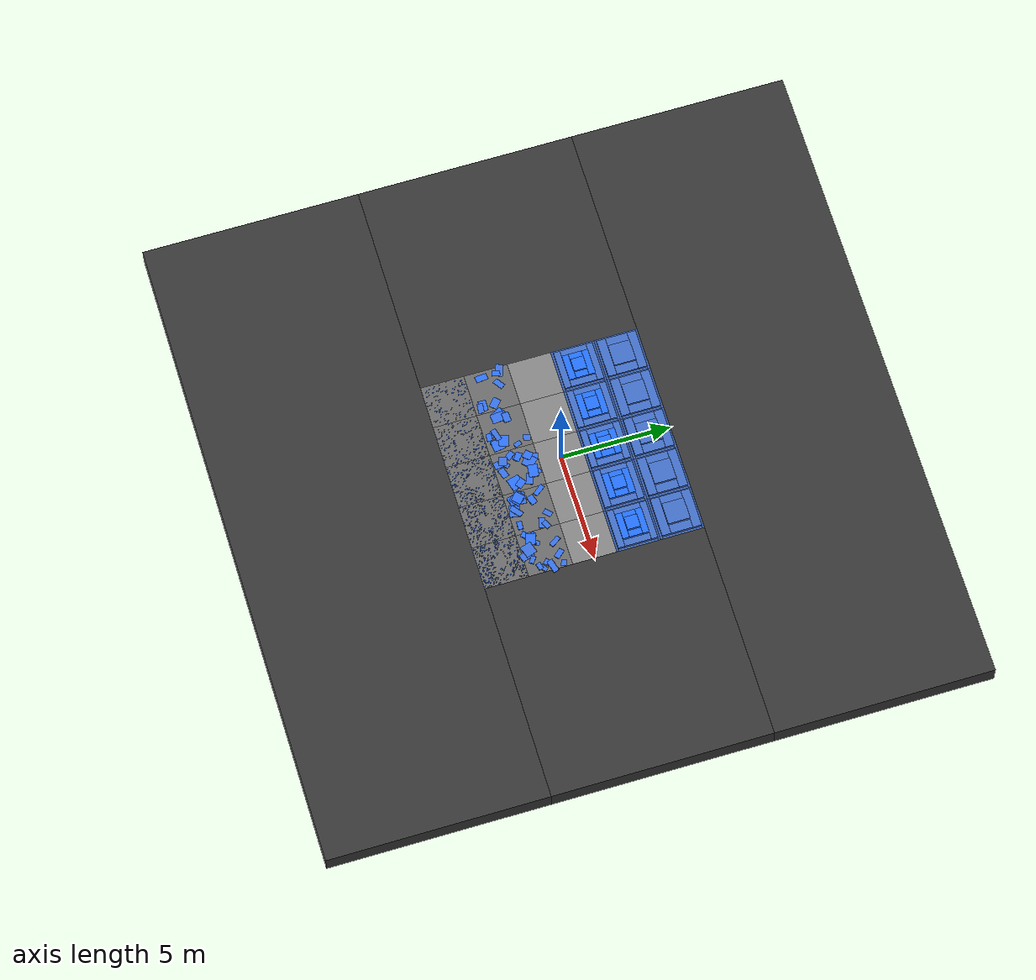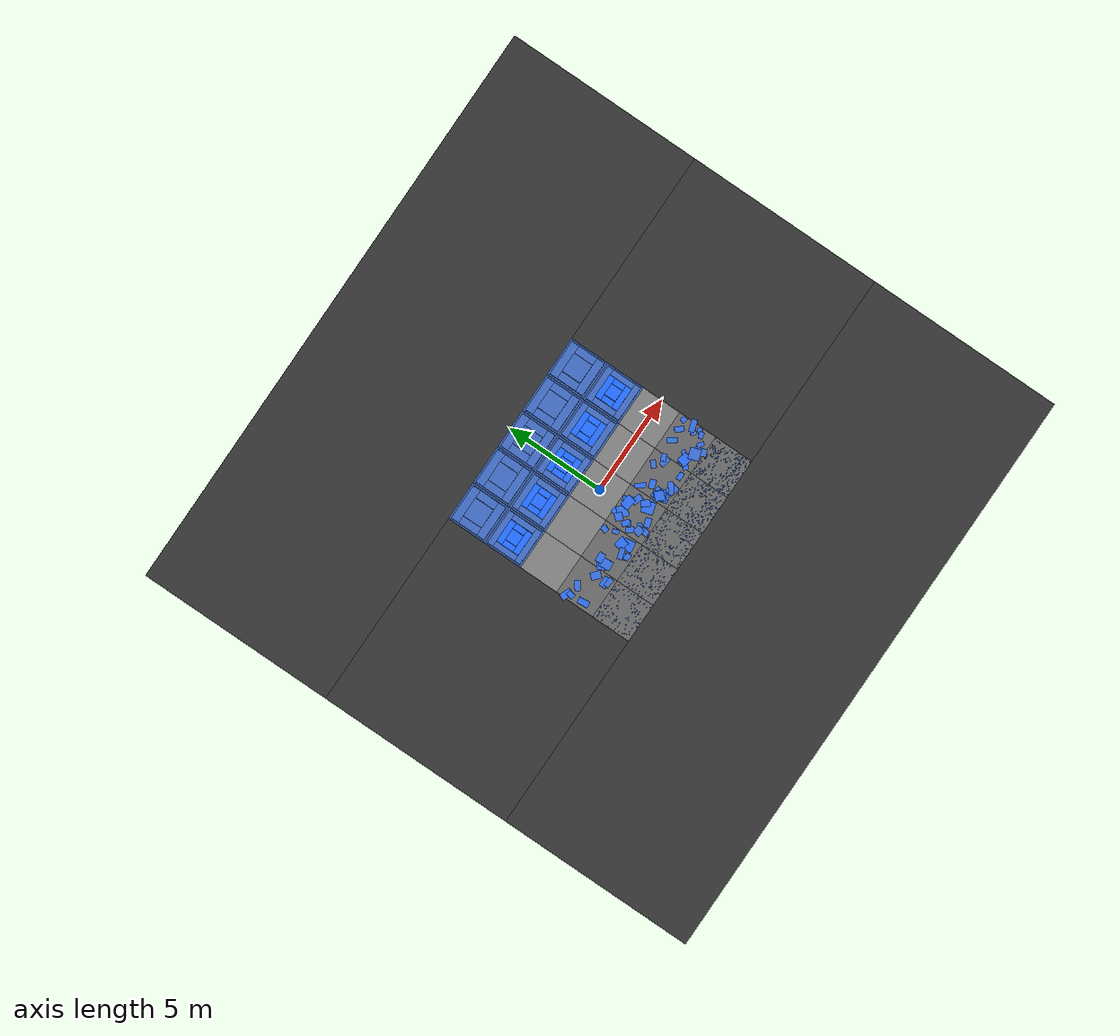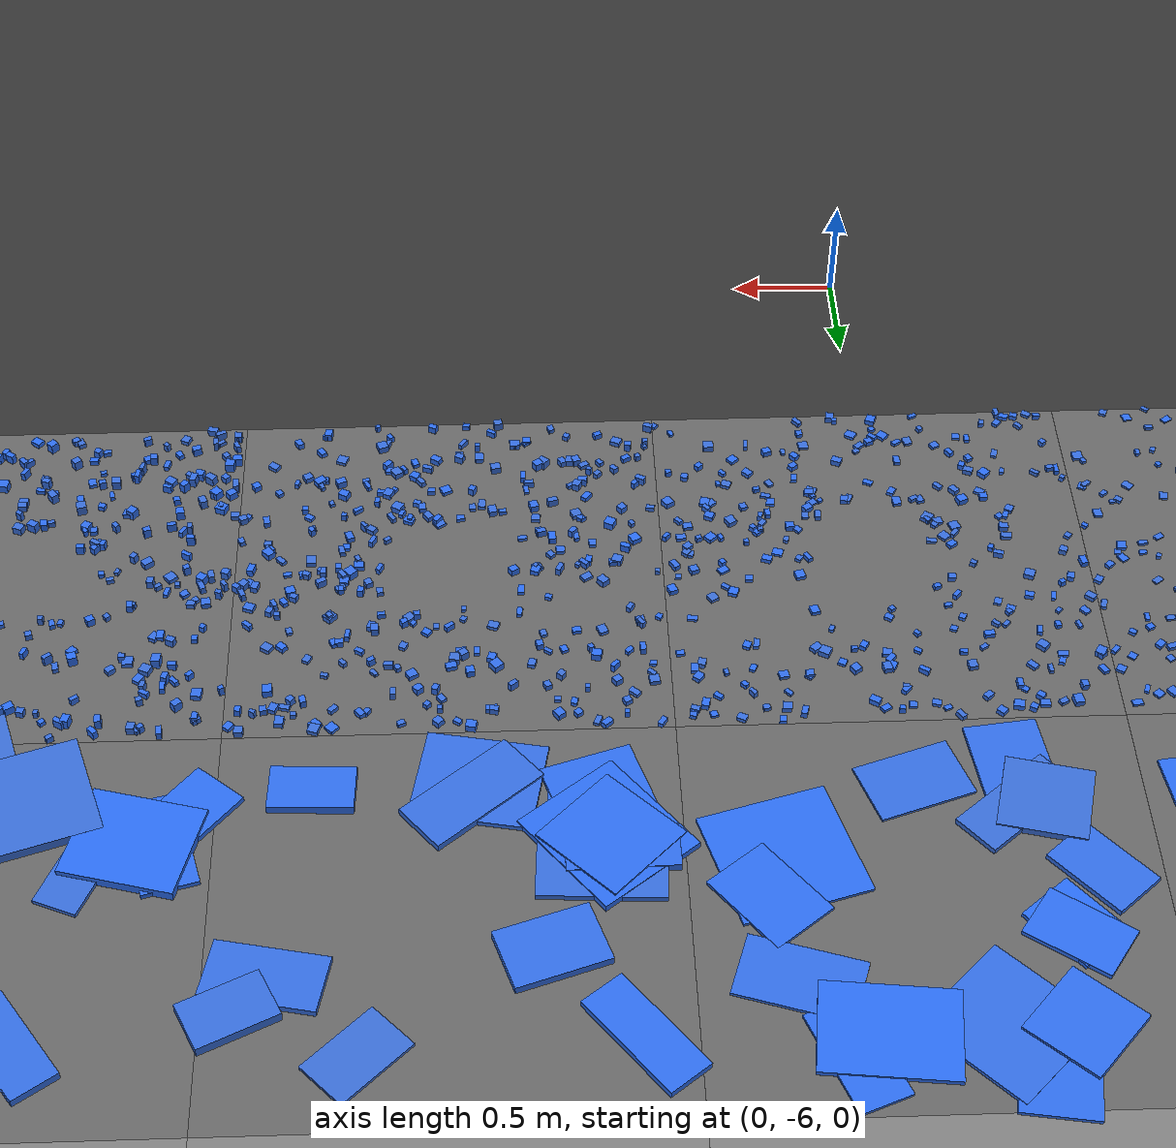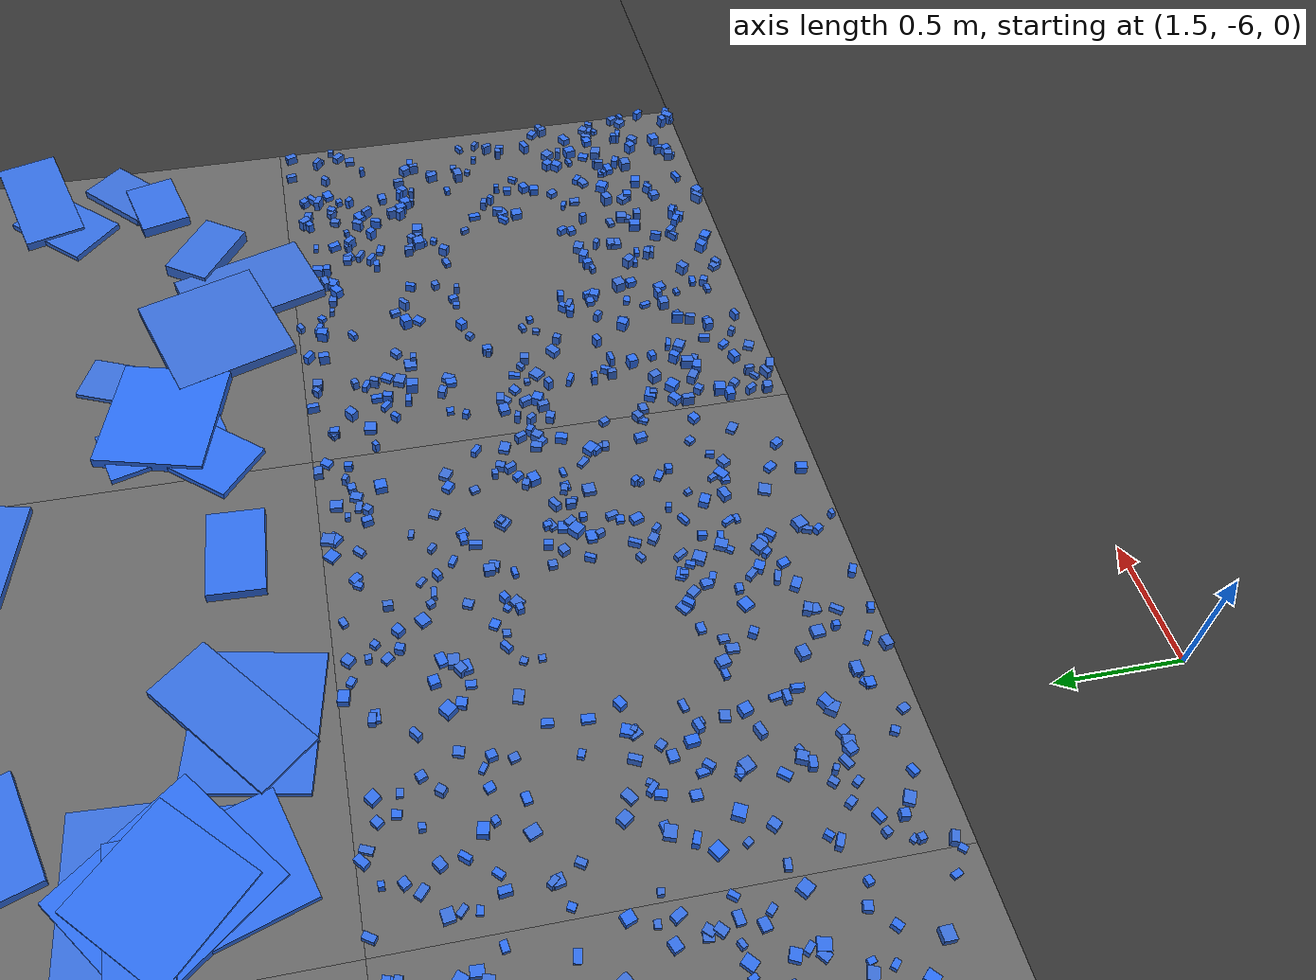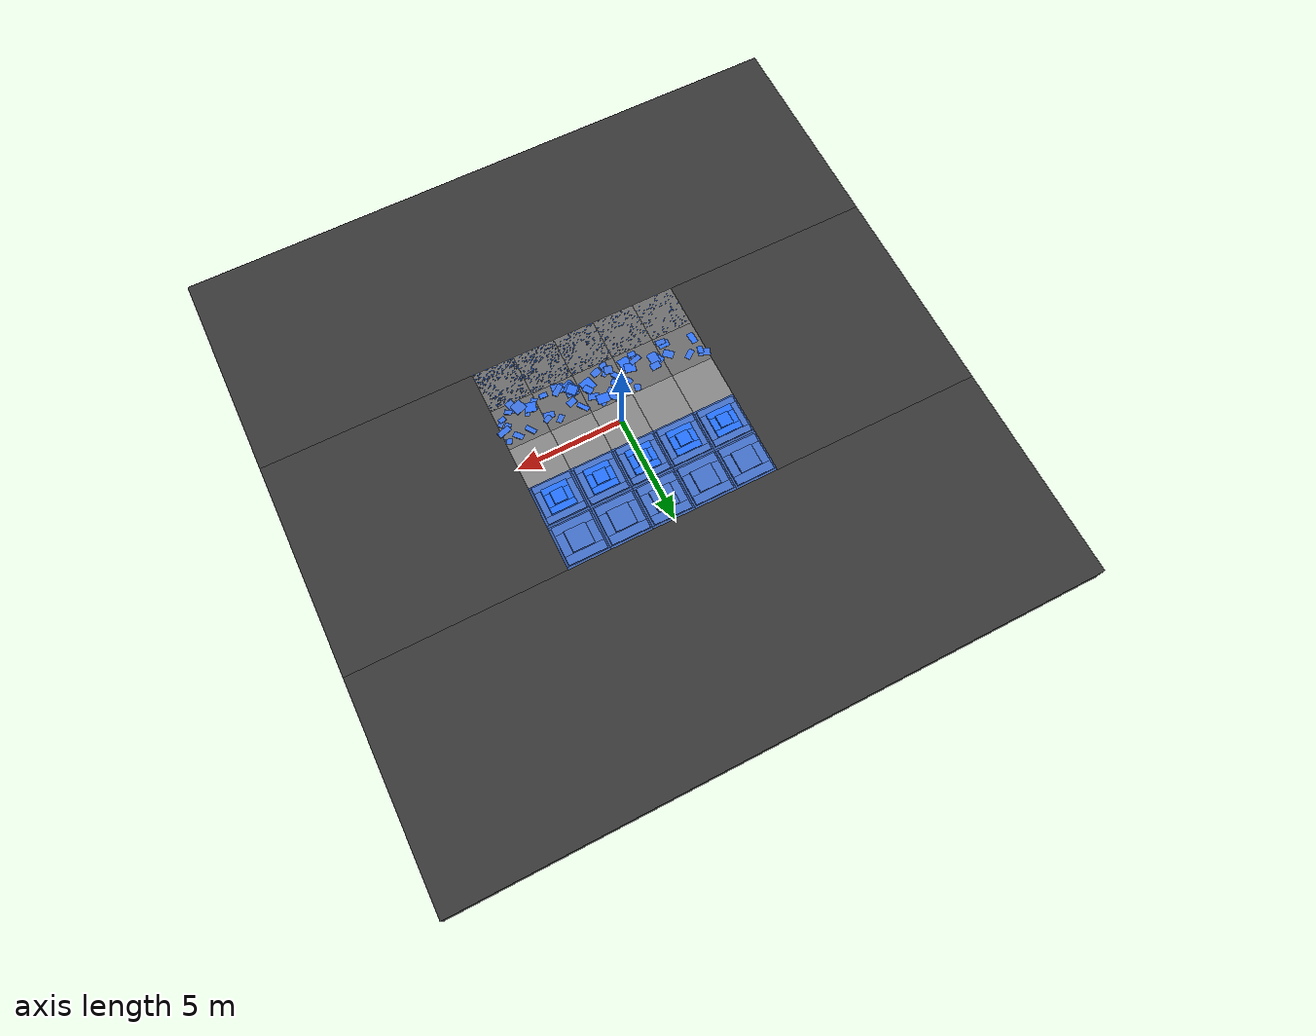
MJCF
<mujoco model="empty">

    <default>
        <default class="terrain">
            <geom type="box" contype="1" conaffinity="0" group="0" />
        </default>
    </default>

    <statistic center="0 0 1" extent="1.8" meansize="0.04"/>
    <visual>
        <headlight ambient=".4 .4 .4" diffuse=".8 .8 .8" specular="1 1 1"/>
        <rgba force="1 0 0 1"/>
        <global azimuth="160" elevation="-20"/>
        <map force="0.01"/>
        <scale contactheight="0.2" contactwidth="0.5" forcewidth="0.3"/>
        <quality shadowsize="8192"/>
    </visual>
    <asset>
        <texture builtin="gradient" height="800" rgb1="0.45 0.59 0.79" rgb2="0.30 0.41 0.60" type="skybox" width="800"/>
        <texture builtin="checker" height="300" mark="edge" markrgb="0 0 0" name="groundplane" rgb1="1 1 1" rgb2="1 1 1" type="2d" width="300"/>
        <material name="groundplane" reflectance="0" texrepeat="5 5" texture="groundplane" texuniform="true"/>
    </asset>
    <worldbody>
        <body name="terrain" childclass="terrain">
            <geom name="terrain_0" size="1 1 0.05" pos="-4 -4 -0.05" type="box" mass="0" rgba="0.4 0.4 0.4 1"/>
            <geom name="terrain_1" size="0.0215814 0.0188542 0.00261382" pos="-4.33532 -3.3048 0.00261382" quat="0.818451 0 0 0.574577" type="box" mass="0" rgba="0.180436 0.426153 0.917587 1"/>
            <geom name="terrain_2" size="0.0227769 0.0109919 0.00262903" pos="-4.17581 -4.96817 0.00262903" quat="-0.235708 0 0 0.971824" type="box" mass="0" rgba="0.214826 0.42469 0.844418 1"/>
            <geom name="terrain_3" size="0.0107534 0.012889 0.0044961" pos="-4.30467 -3.96536 0.0044961" quat="-0.612489 0 0 0.790479" type="box" mass="0" rgba="0.202292 0.425939 0.873232 1"/>
            <geom name="terrain_4" size="0.0206792 0.0111711 0.004963" pos="-4.24412 -3.14166 0.004963" quat="0.732131 0 0 0.681164" type="box" mass="0" rgba="0.215373 0.424611 0.843087 1"/>
            <geom name="terrain_5" size="0.0234565 0.0156376 0.00349937" pos="-3.63119 -4.50394 0.00349937" quat="0.796316 0 0 0.604881" type="box" mass="0" rgba="0.191258 0.426309 0.89641 1"/>
            <geom name="terrain_6" size="0.018918 0.0173778 0.00399948" pos="-3.14505 -3.88367 0.00399948" quat="-0.753098 0 0 0.657908" type="box" mass="0" rgba="0.191781 0.426304 0.895352 1"/>
            <geom name="terrain_7" size="0.0185825 0.0195862 0.00302354" pos="-4.19768 -3.2479 0.00302354" quat="-0.84568 0 0 0.53369" type="box" mass="0" rgba="0.172224 0.42575 0.932801 1"/>
            <geom name="terrain_8" size="0.0235885 0.0117902 0.00388545" pos="-3.39867 -3.16481 0.00388545" quat="-0.49219 0 0 0.870488" type="box" mass="0" rgba="0.215263 0.424627 0.843355 1"/>
            <geom name="terrain_9" size="0.022191 0.0172391 0.00413822" pos="-3.34198 -3.83389 0.00413822" quat="0.955577 0 0 0.294743" type="box" mass="0" rgba="0.214922 0.424676 0.844185 1"/>
            <geom name="terrain_10" size="0.0109542 0.0142714 0.00376111" pos="-4.56582 -4.09099 0.00376111" quat="0.0554504 0 0 0.998461" type="box" mass="0" rgba="0.195594 0.426234 0.887514 1"/>
            <geom name="terrain_11" size="0.0186605 0.0201853 0.00273519" pos="-3.26149 -4.40386 0.00273519" quat="0.251374 0 0 0.96789" type="box" mass="0" rgba="0.178955 0.426097 0.920381 1"/>
            <geom name="terrain_12" size="0.0141186 0.0242614 0.00270968" pos="-4.33601 -3.41317 0.00270968" quat="0.97867 0 0 0.205437" type="box" mass="0" rgba="0.220637 0.423731 0.829919 1"/>
            <geom name="terrain_13" size="0.0224587 0.0127654 0.00269228" pos="-3.87791 -4.62614 0.00269228" quat="-0.434564 0 0 0.900641" type="box" mass="0" rgba="0.18656 0.426298 0.905775 1"/>
            <geom name="terrain_14" size="0.0180094 0.0204154 0.00474599" pos="-3.02697 -4.64787 0.00474599" quat="-0.413265 0 0 0.910611" type="box" mass="0" rgba="0.21822 0.424163 0.836051 1"/>
            <geom name="terrain_15" size="0.0161067 0.02148 0.00261362" pos="-4.09039 -4.83055 0.00261362" quat="-0.94179 0 0 0.336203" type="box" mass="0" rgba="0.197249 0.426182 0.884047 1"/>
            <geom name="terrain_16" size="0.0118128 0.0234041 0.00305549" pos="-4.62703 -4.27156 0.00305549" quat="0.0982816 0 0 0.995159" type="box" mass="0" rgba="0.216311 0.424471 0.840789 1"/>
            <geom name="terrain_17" size="0.0154165 0.0143954 0.00317936" pos="-3.92441 -3.2264 0.00317936" quat="0.514008 0 0 0.857786" type="box" mass="0" rgba="0.215442 0.424601 0.842918 1"/>
            <geom name="terrain_18" size="0.019507 0.020874 0.00251598" pos="-3.80146 -4.38632 0.00251598" quat="-0.319319 0 0 0.947647" type="box" mass="0" rgba="0.187425 0.426307 0.904071 1"/>
            <geom name="terrain_19" size="0.0211425 0.0190811 0.00451767" pos="-3.02399 -4.37999 0.00451767" quat="0.941284 0 0 0.337616" type="box" mass="0" rgba="0.199739 0.426078 0.878756 1"/>
            <geom name="terrain_20" size="0.0187613 0.0174128 0.00304131" pos="-4.47767 -3.98372 0.00304131" quat="0.802677 0 0 0.596414" type="box" mass="0" rgba="0.210955 0.425185 0.853644 1"/>
            <geom name="terrain_21" size="0.0147984 0.0198793 0.00257933" pos="-3.40238 -3.07496 0.00257933" quat="-0.597194 0 0 0.802096" type="box" mass="0" rgba="0.167809 0.425443 0.940712 1"/>
            <geom name="terrain_22" size="0.0201172 0.0237812 0.00393518" pos="-3.37137 -3.95198 0.00393518" quat="0.997376 0 0 0.0723985" type="box" mass="0" rgba="0.212972 0.42494 0.848876 1"/>
            <geom name="terrain_23" size="0.0122552 0.0221629 0.00285585" pos="-4.72049 -4.92871 0.00285585" quat="-0.789551 0 0 0.613685" type="box" mass="0" rgba="0.217086 0.424349 0.838877 1"/>
            <geom name="terrain_24" size="0.0196893 0.0192758 0.00468076" pos="-4.82167 -3.18551 0.00468076" quat="-0.877678 0 0 0.479252" type="box" mass="0" rgba="0.183585 0.426245 0.911565 1"/>
            <geom name="terrain_25" size="0.0144295 0.0133034 0.00367477" pos="-3.67829 -4.61312 0.00367477" quat="-0.116456 0 0 0.993196" type="box" mass="0" rgba="0.217679 0.424253 0.837402 1"/>
            <geom name="terrain_26" size="0.0137223 0.0105189 0.00212912" pos="-3.97247 -4.50433 0.00212912" quat="-0.975942 0 0 0.218031" type="box" mass="0" rgba="0.16912 0.42554 0.938381 1"/>
            <geom name="terrain_27" size="0.0205546 0.020713 0.00494769" pos="-4.72539 -3.89909 0.00494769" quat="-0.555697 0 0 0.831385" type="box" mass="0" rgba="0.203969 0.425828 0.869544 1"/>
            <geom name="terrain_28" size="0.0231625 0.0158813 0.00214934" pos="-4.57576 -3.26318 0.00214934" quat="-0.0296684 0 0 0.99956" type="box" mass="0" rgba="0.216927 0.424375 0.83927 1"/>
            <geom name="terrain_29" size="0.0248006 0.022955 0.00263488" pos="-4.55248 -4.17632 0.00263488" quat="0.753733 0 0 0.65718" type="box" mass="0" rgba="0.173488 0.425826 0.930503 1"/>
            <geom name="terrain_30" size="0.0201694 0.0225347 0.00264716" pos="-4.85194 -3.15176 0.00264716" quat="-0.995958 0 0 0.0898166" type="box" mass="0" rgba="0.209113 0.425384 0.857926 1"/>
            <geom name="terrain_31" size="0.0142043 0.0224578 0.00252908" pos="-3.61216 -4.26122 0.00252908" quat="-0.96836 0 0 0.249558" type="box" mass="0" rgba="0.203091 0.425888 0.871481 1"/>
            <geom name="terrain_32" size="0.0242452 0.0248772 0.00458712" pos="-3.1743 -4.61574 0.00458712" quat="0.171716 0 0 0.985146" type="box" mass="0" rgba="0.18017 0.426144 0.91809 1"/>
            <geom name="terrain_33" size="0.0100457 0.0180924 0.0036284" pos="-3.70006 -3.10842 0.0036284" quat="-0.986449 0 0 0.164066" type="box" mass="0" rgba="0.221849 0.423495 0.826786 1"/>
            <geom name="terrain_34" size="0.0154416 0.0243705 0.00296167" pos="-3.32306 -3.30966 0.00296167" quat="-0.531756 0 0 0.846898" type="box" mass="0" rgba="0.218628 0.424094 0.835025 1"/>
            <geom name="terrain_35" size="0.0181893 0.0242741 0.00351003" pos="-4.05927 -4.74368 0.00351003" quat="0.378613 0 0 0.925555" type="box" mass="0" rgba="0.203954 0.425829 0.869577 1"/>
            <geom name="terrain_36" size="0.0138111 0.0193066 0.00307605" pos="-3.17054 -4.95222 0.00307605" quat="0.99936 0 0 0.0357615" type="box" mass="0" rgba="0.201256 0.425999 0.875486 1"/>
            <geom name="terrain_37" size="0.0115378 0.0225688 0.0040896" pos="-4.97941 -4.16517 0.0040896" quat="-0.711229 0 0 0.702961" type="box" mass="0" rgba="0.177342 0.426028 0.9234 1"/>
            <geom name="terrain_38" size="0.013337 0.0141311 0.00360474" pos="-3.2726 -3.82596 0.00360474" quat="-0.993731 0 0 0.111797" type="box" mass="0" rgba="0.201081 0.426009 0.875866 1"/>
            <geom name="terrain_39" size="0.0101133 0.0218294 0.00459977" pos="-4.715 -3.30469 0.00459977" quat="0.124865 0 0 0.992174" type="box" mass="0" rgba="0.1802 0.426145 0.918033 1"/>
            <geom name="terrain_40" size="0.0238402 0.0129159 0.00336938" pos="-3.54576 -4.64043 0.00336938" quat="0.148036 0 0 0.988982" type="box" mass="0" rgba="0.213345 0.424892 0.847986 1"/>
            <geom name="terrain_41" size="0.0138384 0.020613 0.00369419" pos="-3.93425 -3.24883 0.00369419" quat="-0.859482 0 0 0.511166" type="box" mass="0" rgba="0.21787 0.424222 0.836926 1"/>
            <geom name="terrain_42" size="0.0108398 0.0146091 0.00321565" pos="-3.18954 -3.45427 0.00321565" quat="0.876115 0 0 0.482103" type="box" mass="0" rgba="0.206508 0.425629 0.863871 1"/>
            <geom name="terrain_43" size="0.0108219 0.0151234 0.00432398" pos="-4.57146 -3.89681 0.00432398" quat="-0.509835 0 0 0.860272" type="box" mass="0" rgba="0.17941 0.426115 0.919526 1"/>
            <geom name="terrain_44" size="0.0141487 0.010563 0.00470409" pos="-3.96645 -3.17292 0.00470409" quat="-0.148495 0 0 0.988913" type="box" mass="0" rgba="0.218745 0.424074 0.834731 1"/>
            <geom name="terrain_45" size="0.0231604 0.015005 0.00239958" pos="-3.12509 -3.69669 0.00239958" quat="0.964929 0 0 0.262509" type="box" mass="0" rgba="0.221006 0.42366 0.828968 1"/>
            <geom name="terrain_46" size="0.0222847 0.022356 0.0042995" pos="-4.1922 -3.47939 0.0042995" quat="0.637793 0 0 0.770207" type="box" mass="0" rgba="0.19639 0.42621 0.885852 1"/>
            <geom name="terrain_47" size="0.0158272 0.0170187 0.00334877" pos="-4.18071 -3.35363 0.00334877" quat="0.269133 0 0 0.963103" type="box" mass="0" rgba="0.212138 0.425045 0.850858 1"/>
            <geom name="terrain_48" size="0.0218531 0.014917 0.00342313" pos="-4.53953 -3.9973 0.00342313" quat="0.203685 0 0 0.979036" type="box" mass="0" rgba="0.164122 0.425144 0.947187 1"/>
            <geom name="terrain_49" size="0.0239059 0.0174757 0.00382483" pos="-4.24276 -4.92343 0.00382483" quat="0.0658391 0 0 0.99783" type="box" mass="0" rgba="0.20464 0.425779 0.868055 1"/>
            <geom name="terrain_50" size="0.0203773 0.0192153 0.00353929" pos="-4.5101 -4.83233 0.00353929" quat="0.659261 0 0 0.751914" type="box" mass="0" rgba="0.213672 0.424849 0.847202 1"/>
            <geom name="terrain_51" size="0.0232809 0.0162505 0.00431429" pos="-3.45581 -3.0369 0.00431429" quat="0.925901 0 0 0.377766" type="box" mass="0" rgba="0.208725 0.425423 0.85882 1"/>
            <geom name="terrain_52" size="0.0156678 0.0174564 0.00216448" pos="-3.86755 -4.86947 0.00216448" quat="0.996514 0 0 0.0834304" type="box" mass="0" rgba="0.214192 0.424778 0.84595 1"/>
            <geom name="terrain_53" size="0.0118066 0.021659 0.00296643" pos="-3.26171 -3.67264 0.00296643" quat="0.978901 0 0 0.204336" type="box" mass="0" rgba="0.207514 0.425539 0.86159 1"/>
            <geom name="terrain_54" size="0.0143406 0.0100991 0.00283969" pos="-4.97988 -3.45373 0.00283969" quat="0.959993 0 0 0.280022" type="box" mass="0" rgba="0.205478 0.425714 0.866186 1"/>
            <geom name="terrain_55" size="0.0189026 0.0227777 0.00439244" pos="-3.2471 -4.79931 0.00439244" quat="-0.887233 0 0 0.461322" type="box" mass="0" rgba="0.167432 0.425415 0.94138 1"/>
            <geom name="terrain_56" size="0.0186759 0.0100102 0.00366452" pos="-3.11144 -3.99858 0.00366452" quat="0.598249 0 0 0.80131" type="box" mass="0" rgba="0.207777 0.425515 0.86099 1"/>
            <geom name="terrain_57" size="0.0227499 0.0205683 0.00302436" pos="-4.88713 -3.44721 0.00302436" quat="0.420107 0 0 0.907475" type="box" mass="0" rgba="0.173078 0.425802 0.931249 1"/>
            <geom name="terrain_58" size="0.0189636 0.0191823 0.00244889" pos="-3.07699 -3.9321 0.00244889" quat="-0.344358 0 0 0.938838" type="box" mass="0" rgba="0.216534 0.424436 0.84024 1"/>
            <geom name="terrain_59" size="0.0137015 0.0169386 0.00339515" pos="-4.43197 -4.45251 0.00339515" quat="0.474063 0 0 0.880491" type="box" mass="0" rgba="0.183885 0.426252 0.910987 1"/>
            <geom name="terrain_60" size="0.0233807 0.0232674 0.00272625" pos="-3.36829 -3.64628 0.00272625" quat="0.593963 0 0 0.804492" type="box" mass="0" rgba="0.211675 0.425101 0.851952 1"/>
            <geom name="terrain_61" size="0.0249641 0.0164991 0.00492623" pos="-3.15182 -4.23712 0.00492623" quat="-0.397217 0 0 0.917725" type="box" mass="0" rgba="0.19679 0.426198 0.885012 1"/>
            <geom name="terrain_62" size="0.017887 0.0206444 0.00263197" pos="-3.6058 -4.37157 0.00263197" quat="0.962641 0 0 0.270783" type="box" mass="0" rgba="0.192622 0.426295 0.89364 1"/>
            <geom name="terrain_63" size="0.0212018 0.0191916 0.00350621" pos="-3.49967 -4.48672 0.00350621" quat="0.798557 0 0 0.60192" type="box" mass="0" rgba="0.175863 0.425956 0.926142 1"/>
            <geom name="terrain_64" size="0.0186866 0.0245973 0.00257687" pos="-4.23648 -4.49488 0.00257687" quat="0.9908 0 0 0.135334" type="box" mass="0" rgba="0.197756 0.426163 0.882978 1"/>
            <geom name="terrain_65" size="0.015886 0.022279 0.00433621" pos="-3.67279 -3.22997 0.00433621" quat="0.599679 0 0 0.80024" type="box" mass="0" rgba="0.196265 0.426214 0.886112 1"/>
            <geom name="terrain_66" size="0.0232497 0.0221198 0.00337114" pos="-3.93231 -3.64469 0.00337114" quat="0.982855 0 0 0.184378" type="box" mass="0" rgba="0.210621 0.425223 0.854426 1"/>
            <geom name="terrain_67" size="0.0217381 0.0110986 0.00386835" pos="-3.44941 -4.27568 0.00386835" quat="-0.385064 0 0 0.92289" type="box" mass="0" rgba="0.202941 0.425898 0.87181 1"/>
            <geom name="terrain_68" size="0.014436 0.0162556 0.00427168" pos="-3.84028 -4.40579 0.00427168" quat="0.494712 0 0 0.869057" type="box" mass="0" rgba="0.215501 0.424592 0.842775 1"/>
            <geom name="terrain_69" size="0.0233109 0.0154791 0.00328549" pos="-3.5914 -4.17951 0.00328549" quat="0.87581 0 0 0.482657" type="box" mass="0" rgba="0.171396 0.425697 0.934298 1"/>
            <geom name="terrain_70" size="0.0194403 0.0103085 0.0029865" pos="-3.62955 -4.98794 0.0029865" quat="-0.766407 0 0 0.642355" type="box" mass="0" rgba="0.194773 0.426255 0.889217 1"/>
            <geom name="terrain_71" size="0.0240797 0.0205 0.00354415" pos="-4.04083 -3.72848 0.00354415" quat="0.242975 0 0 0.970033" type="box" mass="0" rgba="0.188681 0.426314 0.901581 1"/>
            <geom name="terrain_72" size="0.0194074 0.0204799 0.00368602" pos="-4.59363 -3.91749 0.00368602" quat="0.938022 0 0 0.346576" type="box" mass="0" rgba="0.169558 0.425572 0.9376 1"/>
            <geom name="terrain_73" size="0.0204756 0.0223204 0.00308344" pos="-3.40532 -3.11903 0.00308344" quat="-0.364245 0 0 0.931303" type="box" mass="0" rgba="0.199751 0.426078 0.878732 1"/>
            <geom name="terrain_74" size="0.0108391 0.0218219 0.00236979" pos="-4.57567 -3.64356 0.00236979" quat="-0.999733 0 0 0.0231243" type="box" mass="0" rgba="0.170958 0.425668 0.935087 1"/>
            <geom name="terrain_75" size="0.0231017 0.0180134 0.00236532" pos="-4.97353 -3.83421 0.00236532" quat="-0.727661 0 0 0.685937" type="box" mass="0" rgba="0.1982 0.426146 0.882038 1"/>
            <geom name="terrain_76" size="0.0235357 0.0160394 0.00422054" pos="-3.7233 -3.58281 0.00422054" quat="0.913748 0 0 0.40628" type="box" mass="0" rgba="0.211949 0.425068 0.851305 1"/>
            <geom name="terrain_77" size="0.0154892 0.0173551 0.00364312" pos="-4.64789 -3.35432 0.00364312" quat="-0.981179 0 0 0.193098" type="box" mass="0" rgba="0.221541 0.423556 0.827585 1"/>
            <geom name="terrain_78" size="0.0117402 0.014884 0.0044976" pos="-3.61486 -4.6395 0.0044976" quat="0.932739 0 0 0.360553" type="box" mass="0" rgba="0.18154 0.42619 0.915489 1"/>
            <geom name="terrain_79" size="0.0140929 0.0159672 0.00416692" pos="-4.81088 -4.44892 0.00416692" quat="0.92341 0 0 0.383814" type="box" mass="0" rgba="0.164902 0.42521 0.945827 1"/>
            <geom name="terrain_80" size="0.0192233 0.0189091 0.00258381" pos="-3.38605 -4.51729 0.00258381" quat="-0.991165 0 0 0.132634" type="box" mass="0" rgba="0.210197 0.42527 0.855414 1"/>
            <geom name="terrain_81" size="0.0187702 0.0248295 0.00359832" pos="-4.1491 -4.70937 0.00359832" quat="0.622407 0 0 0.782694" type="box" mass="0" rgba="0.170891 0.425663 0.935208 1"/>
            <geom name="terrain_82" size="0.0100092 0.0146454 0.00465878" pos="-3.94848 -3.61471 0.00465878" quat="-0.56618 0 0 0.824282" type="box" mass="0" rgba="0.179898 0.426134 0.918606 1"/>
            <geom name="terrain_83" size="0.0110456 0.0181605 0.0044272" pos="-4.77636 -4.75647 0.0044272" quat="-0.185035 0 0 0.982732" type="box" mass="0" rgba="0.17074 0.425653 0.935479 1"/>
            <geom name="terrain_84" size="0.0153346 0.0153566 0.00493104" pos="-4.54203 -4.7148 0.00493104" quat="0.990622 0 0 0.136628" type="box" mass="0" rgba="0.213271 0.424901 0.848162 1"/>
            <geom name="terrain_85" size="0.014567 0.0246939 0.00457349" pos="-4.70062 -4.83819 0.00457349" quat="-0.997315 0 0 0.0732257" type="box" mass="0" rgba="0.205569 0.425707 0.865982 1"/>
            <geom name="terrain_86" size="0.0217788 0.0178826 0.00324069" pos="-4.81415 -4.64818 0.00324069" quat="-0.588538 0 0 0.80847" type="box" mass="0" rgba="0.203687 0.425847 0.870168 1"/>
            <geom name="terrain_87" size="0.0196556 0.0162683 0.00328379" pos="-4.52168 -3.58038 0.00328379" quat="-0.662976 0 0 0.748641" type="box" mass="0" rgba="0.176822 0.426003 0.924365 1"/>
            <geom name="terrain_88" size="0.0100194 0.0177775 0.00450064" pos="-3.67085 -4.25833 0.00450064" quat="-0.309433 0 0 0.950921" type="box" mass="0" rgba="0.178295 0.42607 0.921619 1"/>
            <geom name="terrain_89" size="0.0187015 0.0153503 0.00464553" pos="-3.28893 -4.70049 0.00464553" quat="0.678529 0 0 0.734573" type="box" mass="0" rgba="0.166579 0.425348 0.942885 1"/>
            <geom name="terrain_90" size="0.014045 0.0167651 0.00325607" pos="-3.45363 -3.1355 0.00325607" quat="-0.970671 0 0 0.240412" type="box" mass="0" rgba="0.174875 0.425904 0.927962 1"/>
            <geom name="terrain_91" size="0.0228792 0.0234377 0.00436417" pos="-4.62278 -3.49472 0.00436417" quat="0.770458 0 0 0.63749" type="box" mass="0" rgba="0.192901 0.426291 0.893069 1"/>
            <geom name="terrain_92" size="0.0217319 0.0150054 0.00465422" pos="-4.19743 -4.29804 0.00465422" quat="-0.115471 0 0 0.993311" type="box" mass="0" rgba="0.20415 0.425815 0.869143 1"/>
            <geom name="terrain_93" size="0.0236349 0.0211592 0.00366324" pos="-3.72776 -3.27123 0.00366324" quat="0.997817 0 0 0.0660367" type="box" mass="0" rgba="0.217344 0.424308 0.838236 1"/>
            <geom name="terrain_94" size="0.021322 0.0109234 0.00491382" pos="-3.46297 -4.23496 0.00491382" quat="0.176751 0 0 0.984256" type="box" mass="0" rgba="0.215692 0.424564 0.842308 1"/>
            <geom name="terrain_95" size="0.0131315 0.0244752 0.00395286" pos="-3.40292 -3.25563 0.00395286" quat="0.65865 0 0 0.752449" type="box" mass="0" rgba="0.206086 0.425664 0.86482 1"/>
            <geom name="terrain_96" size="0.0162962 0.0113925 0.00378905" pos="-3.3482 -3.7613 0.00378905" quat="-0.433943 0 0 0.90094" type="box" mass="0" rgba="0.194633 0.426258 0.889508 1"/>
            <geom name="terrain_97" size="0.0144404 0.0121683 0.00384778" pos="-3.11044 -4.27768 0.00384778" quat="0.888508 0 0 0.458862" type="box" mass="0" rgba="0.201489 0.425986 0.874982 1"/>
            <geom name="terrain_98" size="0.0228963 0.0136447 0.00234607" pos="-3.67158 -3.07588 0.00234607" quat="0.69995 0 0 0.714192" type="box" mass="0" rgba="0.220652 0.423728 0.829881 1"/>
            <geom name="terrain_99" size="0.0232421 0.0235003 0.00472097" pos="-3.12937 -3.49313 0.00472097" quat="0.985898 0 0 0.167345" type="box" mass="0" rgba="0.166809 0.425366 0.94248 1"/>
            <geom name="terrain_100" size="0.0209487 0.0132059 0.00392258" pos="-4.89171 -4.38168 0.00392258" quat="-0.566867 0 0 0.82381" type="box" mass="0" rgba="0.210014 0.425289 0.855839 1"/>
            <geom name="terrain_101" size="0.0226229 0.0128151 0.00458412" pos="-3.74022 -4.67839 0.00458412" quat="-0.00907227 0 0 0.999959" type="box" mass="0" rgba="0.180975 0.426171 0.916564 1"/>
            <geom name="terrain_102" size="0.0155617 0.0187465 0.00350461" pos="-4.62549 -4.52602 0.00350461" quat="-0.191284 0 0 0.981535" type="box" mass="0" rgba="0.189795 0.426316 0.899357 1"/>
            <geom name="terrain_103" size="0.021495 0.0174411 0.00368682" pos="-4.62643 -3.16425 0.00368682" quat="-0.0624198 0 0 0.99805" type="box" mass="0" rgba="0.186912 0.426302 0.905083 1"/>
            <geom name="terrain_104" size="0.0222096 0.0239896 0.00278351" pos="-3.05255 -4.29422 0.00278351" quat="0.504064 0 0 0.863667" type="box" mass="0" rgba="0.192128 0.426301 0.894646 1"/>
            <geom name="terrain_105" size="0.0224875 0.0195423 0.00497123" pos="-4.3678 -3.71747 0.00497123" quat="-0.393752 0 0 0.919217" type="box" mass="0" rgba="0.174185 0.425866 0.929229 1"/>
            <geom name="terrain_106" size="0.0237152 0.0225347 0.00468417" pos="-3.27951 -3.32207 0.00468417" quat="0.907448 0 0 0.420165" type="box" mass="0" rgba="0.196185 0.426217 0.88628 1"/>
            <geom name="terrain_107" size="0.024466 0.0159325 0.00303987" pos="-4.34853 -3.26922 0.00303987" quat="0.926318 0 0 0.376742" type="box" mass="0" rgba="0.21848 0.424119 0.835398 1"/>
            <geom name="terrain_108" size="0.0172292 0.020139 0.00218439" pos="-4.49212 -3.94275 0.00218439" quat="-0.955145 0 0 0.29614" type="box" mass="0" rgba="0.212479 0.425003 0.85005 1"/>
            <geom name="terrain_109" size="0.0112393 0.012352 0.00207839" pos="-4.47007 -4.48509 0.00207839" quat="0.674757 0 0 0.73804" type="box" mass="0" rgba="0.204251 0.425807 0.868921 1"/>
            <geom name="terrain_110" size="0.0215067 0.0223633 0.00340971" pos="-3.12621 -3.17107 0.00340971" quat="0.821112 0 0 0.570767" type="box" mass="0" rgba="0.204653 0.425778 0.868028 1"/>
            <geom name="terrain_111" size="0.011526 0.0127982 0.00441198" pos="-4.86908 -4.5657 0.00441198" quat="-0.675508 0 0 0.737353" type="box" mass="0" rgba="0.187549 0.426308 0.903827 1"/>
            <geom name="terrain_112" size="0.0191521 0.0125174 0.00495344" pos="-4.29068 -3.15907 0.00495344" quat="-0.891619 0 0 0.452787" type="box" mass="0" rgba="0.171377 0.425695 0.934333 1"/>
            <geom name="terrain_113" size="0.0120463 0.0120472 0.00211179" pos="-3.79732 -3.08836 0.00211179" quat="0.0114677 0 0 0.999934" type="box" mass="0" rgba="0.220111 0.423829 0.831265 1"/>
            <geom name="terrain_114" size="0.0114932 0.0221754 0.00331087" pos="-3.28643 -4.36905 0.00331087" quat="-0.930821 0 0 0.365474" type="box" mass="0" rgba="0.210526 0.425233 0.854648 1"/>
            <geom name="terrain_115" size="0.0193267 0.0156505 0.00413876" pos="-4.38989 -4.78523 0.00413876" quat="0.0914436 0 0 0.99581" type="box" mass="0" rgba="0.218801 0.424064 0.834591 1"/>
            <geom name="terrain_116" size="0.0192304 0.0158274 0.00475671" pos="-4.41855 -3.44178 0.00475671" quat="0.790678 0 0 0.612233" type="box" mass="0" rgba="0.211334 0.425141 0.852755 1"/>
            <geom name="terrain_117" size="0.0114173 0.0237234 0.00422023" pos="-3.08445 -4.17363 0.00422023" quat="-0.757918 0 0 0.65235" type="box" mass="0" rgba="0.174475 0.425882 0.928698 1"/>
            <geom name="terrain_118" size="0.0116805 0.0122055 0.00429427" pos="-3.19323 -4.24493 0.00429427" quat="0.589815 0 0 0.807538" type="box" mass="0" rgba="0.186859 0.426302 0.905188 1"/>
            <geom name="terrain_119" size="0.0196121 0.0194359 0.00282265" pos="-4.21125 -4.39326 0.00282265" quat="0.885105 0 0 0.465392" type="box" mass="0" rgba="0.194732 0.426256 0.889302 1"/>
            <geom name="terrain_120" size="0.0111032 0.0164623 0.00289027" pos="-4.3651 -3.58195 0.00289027" quat="-0.776 0 0 0.630734" type="box" mass="0" rgba="0.205651 0.4257 0.865799 1"/>
            <geom name="terrain_121" size="0.0188807 0.0183757 0.00446663" pos="-3.6071 -3.41777 0.00446663" quat="-0.843355 0 0 0.537356" type="box" mass="0" rgba="0.162681 0.425016 0.949688 1"/>
            <geom name="terrain_122" size="0.0227083 0.0206228 0.00485664" pos="-3.76299 -4.49768 0.00485664" quat="0.206415 0 0 0.978465" type="box" mass="0" rgba="0.18683 0.426301 0.905244 1"/>
            <geom name="terrain_123" size="0.0178928 0.0245014 0.00372797" pos="-3.79189 -4.40255 0.00372797" quat="-0.75629 0 0 0.654237" type="box" mass="0" rgba="0.21484 0.424688 0.844384 1"/>
            <geom name="terrain_124" size="0.0243046 0.0241272 0.00330364" pos="-4.17735 -3.30567 0.00330364" quat="-0.756783 0 0 0.653666" type="box" mass="0" rgba="0.176276 0.425977 0.925379 1"/>
            <geom name="terrain_125" size="0.0166004 0.0125675 0.00211467" pos="-4.06118 -4.93853 0.00211467" quat="0.360346 0 0 0.932819" type="box" mass="0" rgba="0.210154 0.425274 0.855516 1"/>
            <geom name="terrain_126" size="0.016597 0.0162278 0.0022349" pos="-4.71865 -3.14746 0.0022349" quat="0.0723982 0 0 0.997376" type="box" mass="0" rgba="0.194679 0.426257 0.889412 1"/>
            <geom name="terrain_127" size="0.0100686 0.0217767 0.0033652" pos="-3.27239 -3.69389 0.0033652" quat="0.985837 0 0 0.167708" type="box" mass="0" rgba="0.192731 0.426293 0.893416 1"/>
            <geom name="terrain_128" size="0.0186773 0.0132915 0.00473833" pos="-4.10128 -4.36791 0.00473833" quat="0.991553 0 0 0.129702" type="box" mass="0" rgba="0.207863 0.425507 0.860795 1"/>
            <geom name="terrain_129" size="0.0116928 0.0173035 0.00401458" pos="-4.54767 -3.99152 0.00401458" quat="0.677181 0 0 0.735816" type="box" mass="0" rgba="0.214424 0.424746 0.84539 1"/>
            <geom name="terrain_130" size="0.0141806 0.0108002 0.00296721" pos="-3.07959 -3.49125 0.00296721" quat="0.523695 0 0 0.851906" type="box" mass="0" rgba="0.193725 0.426277 0.891379 1"/>
            <geom name="terrain_131" size="0.0167839 0.0109626 0.00274716" pos="-4.24417 -4.79632 0.00274716" quat="0.985184 0 0 0.171498" type="box" mass="0" rgba="0.214627 0.424718 0.844899 1"/>
            <geom name="terrain_132" size="0.0137139 0.0232689 0.00489767" pos="-3.18545 -4.38107 0.00489767" quat="0.156663 0 0 0.987652" type="box" mass="0" rgba="0.197818 0.426161 0.882847 1"/>
            <geom name="terrain_133" size="0.0230901 0.0166795 0.0045648" pos="-4.41942 -4.37124 0.0045648" quat="0.680323 0 0 0.732913" type="box" mass="0" rgba="0.209063 0.425389 0.858041 1"/>
            <geom name="terrain_134" size="0.0173215 0.0121557 0.00457706" pos="-4.59777 -4.78778 0.00457706" quat="-0.0619121 0 0 0.998082" type="box" mass="0" rgba="0.196479 0.426208 0.885664 1"/>
            <geom name="terrain_135" size="0.0227958 0.0126149 0.00211961" pos="-4.28589 -3.90596 0.00211961" quat="-0.746906 0 0 0.664929" type="box" mass="0" rgba="0.20865 0.425431 0.858991 1"/>
            <geom name="terrain_136" size="0.0233561 0.012567 0.00452486" pos="-4.72442 -4.20517 0.00452486" quat="0.353776 0 0 0.93533" type="box" mass="0" rgba="0.183315 0.426239 0.912087 1"/>
            <geom name="terrain_137" size="0.020786 0.0235199 0.00454276" pos="-3.72395 -4.47627 0.00454276" quat="0.180865 0 0 0.983508" type="box" mass="0" rgba="0.163062 0.425051 0.949028 1"/>
            <geom name="terrain_138" size="0.0222224 0.0145795 0.00237439" pos="-4.3875 -3.0384 0.00237439" quat="0.239539 0 0 0.970887" type="box" mass="0" rgba="0.195047 0.426248 0.888651 1"/>
            <geom name="terrain_139" size="0.0130417 0.0144826 0.00442082" pos="-4.35373 -3.64429 0.00442082" quat="0.68522 0 0 0.728337" type="box" mass="0" rgba="0.208391 0.425456 0.859586 1"/>
            <geom name="terrain_140" size="0.0225697 0.0183017 0.00457116" pos="-4.45795 -3.9767 0.00457116" quat="0.797406 0 0 0.603443" type="box" mass="0" rgba="0.196865 0.426195 0.884854 1"/>
            <geom name="terrain_141" size="0.0204758 0.0104152 0.00250109" pos="-3.2854 -4.85686 0.00250109" quat="0.902958 0 0 0.42973" type="box" mass="0" rgba="0.191507 0.426307 0.895906 1"/>
            <geom name="terrain_142" size="0.0106312 0.0171961 0.00470031" pos="-4.89278 -4.15899 0.00470031" quat="-0.295836 0 0 0.955239" type="box" mass="0" rgba="0.175134 0.425918 0.927487 1"/>
            <geom name="terrain_143" size="0.010758 0.0136115 0.00340538" pos="-3.30147 -3.25439 0.00340538" quat="-0.527125 0 0 0.849788" type="box" mass="0" rgba="0.208287 0.425466 0.859825 1"/>
            <geom name="terrain_144" size="0.0192682 0.0188763 0.00380939" pos="-4.60508 -3.09367 0.00380939" quat="0.831707 0 0 0.555215" type="box" mass="0" rgba="0.169907 0.425596 0.936974 1"/>
            <geom name="terrain_145" size="0.0178375 0.0225202 0.00259257" pos="-4.45222 -3.07329 0.00259257" quat="0.946431 0 0 0.322907" type="box" mass="0" rgba="0.176524 0.425989 0.924918 1"/>
            <geom name="terrain_146" size="0.0187416 0.0132914 0.00330377" pos="-3.37618 -3.17333 0.00330377" quat="0.986571 0 0 0.163332" type="box" mass="0" rgba="0.174654 0.425892 0.928369 1"/>
            <geom name="terrain_147" size="0.015204 0.0230065 0.00333227" pos="-4.05155 -4.88711 0.00333227" quat="-0.758421 0 0 0.651765" type="box" mass="0" rgba="0.197312 0.42618 0.883916 1"/>
            <geom name="terrain_148" size="0.0152903 0.0119786 0.0037113" pos="-4.66232 -4.32522 0.0037113" quat="0.753501 0 0 0.657447" type="box" mass="0" rgba="0.216664 0.424416 0.83992 1"/>
            <geom name="terrain_149" size="0.0140905 0.0136005 0.00350888" pos="-4.37531 -3.40737 0.00350888" quat="-0.193024 0 0 0.981194" type="box" mass="0" rgba="0.196526 0.426206 0.885566 1"/>
            <geom name="terrain_150" size="0.0167297 0.024676 0.00316486" pos="-3.73749 -3.37945 0.00316486" quat="0.998907 0 0 0.0467467" type="box" mass="0" rgba="0.220655 0.423727 0.829872 1"/>
            <geom name="terrain_151" size="0.0165662 0.0233477 0.00243908" pos="-4.41567 -4.53454 0.00243908" quat="-0.370782 0 0 0.92872" type="box" mass="0" rgba="0.16725 0.425401 0.941702 1"/>
            <geom name="terrain_152" size="0.019274 0.0182786 0.00464946" pos="-3.34543 -3.68095 0.00464946" quat="-0.958861 0 0 0.283877" type="box" mass="0" rgba="0.180752 0.426164 0.916988 1"/>
            <geom name="terrain_153" size="0.0202714 0.0244426 0.00489865" pos="-3.67641 -3.13047 0.00489865" quat="-0.580032 0 0 0.814594" type="box" mass="0" rgba="0.199705 0.42608 0.87883 1"/>
            <geom name="terrain_154" size="0.0144475 0.0174766 0.00437543" pos="-3.29105 -3.06003 0.00437543" quat="-0.963683 0 0 0.267048" type="box" mass="0" rgba="0.221888 0.423487 0.826685 1"/>
            <geom name="terrain_155" size="0.0163196 0.0100681 0.00373856" pos="-3.7243 -4.61438 0.00373856" quat="-0.365772 0 0 0.930705" type="box" mass="0" rgba="0.180683 0.426162 0.917118 1"/>
            <geom name="terrain_156" size="0.022068 0.0154474 0.0033418" pos="-4.68215 -4.71375 0.0033418" quat="0.865394 0 0 0.501093" type="box" mass="0" rgba="0.185214 0.426279 0.908407 1"/>
            <geom name="terrain_157" size="0.0156243 0.0148791 0.00496272" pos="-3.45871 -4.14047 0.00496272" quat="-0.560959 0 0 0.827843" type="box" mass="0" rgba="0.197975 0.426155 0.882515 1"/>
            <geom name="terrain_158" size="0.0131381 0.0180251 0.0031792" pos="-3.68531 -3.92182 0.0031792" quat="0.698287 0 0 0.715818" type="box" mass="0" rgba="0.197514 0.426172 0.883489 1"/>
            <geom name="terrain_159" size="0.013237 0.011588 0.00267552" pos="-3.61053 -3.98064 0.00267552" quat="-0.214939 0 0 0.976627" type="box" mass="0" rgba="0.198088 0.42615 0.882275 1"/>
            <geom name="terrain_160" size="0.0127981 0.0119209 0.00333654" pos="-4.60088 -3.31501 0.00333654" quat="-0.893545 0 0 0.448974" type="box" mass="0" rgba="0.175712 0.425948 0.926422 1"/>
            <geom name="terrain_161" size="0.022455 0.017513 0.00487453" pos="-4.37507 -3.93004 0.00487453" quat="-0.6657 0 0 0.74622" type="box" mass="0" rgba="0.192494 0.426296 0.8939 1"/>
            <geom name="terrain_162" size="1 1 0.05" pos="-2 -4 -0.05" type="box" mass="0" rgba="0.4 0.4 0.4 1"/>
            <geom name="terrain_163" size="0.0114006 0.0118092 0.00940604" pos="-1.33408 -3.96425 0.00940604" quat="0.161854 0 0 0.986815" type="box" mass="0" rgba="0.211416 0.425131 0.852561 1"/>
            <geom name="terrain_164" size="0.0193967 0.0127956 0.00773316" pos="-1.86092 -3.12058 0.00773316" quat="-0.908108 0 0 0.418737" type="box" mass="0" rgba="0.186343 0.426296 0.906201 1"/>
            <geom name="terrain_165" size="0.0169137 0.0129313 0.00936647" pos="-1.44831 -3.16527 0.00936647" quat="-0.890497 0 0 0.454989" type="box" mass="0" rgba="0.17881 0.426091 0.920653 1"/>
            <geom name="terrain_166" size="0.0109039 0.0105441 0.00972564" pos="-2.81911 -3.73558 0.00972564" quat="0.557984 0 0 0.829852" type="box" mass="0" rgba="0.219898 0.423868 0.83181 1"/>
            <geom name="terrain_167" size="0.0221769 0.024931 0.0085298" pos="-1.91569 -4.56706 0.0085298" quat="-0.56743 0 0 0.823422" type="box" mass="0" rgba="0.221151 0.423632 0.828596 1"/>
            <geom name="terrain_168" size="0.0206507 0.0117829 0.00480865" pos="-1.78667 -4.31424 0.00480865" quat="0.988447 0 0 0.15157" type="box" mass="0" rgba="0.17997 0.426136 0.918469 1"/>
            <geom name="terrain_169" size="0.0178241 0.011189 0.00590091" pos="-1.26605 -3.99413 0.00590091" quat="0.998746 0 0 0.0500649" type="box" mass="0" rgba="0.178943 0.426097 0.920404 1"/>
            <geom name="terrain_170" size="0.0147319 0.0242495 0.00613236" pos="-2.35861 -3.70821 0.00613236" quat="-0.588407 0 0 0.808565" type="box" mass="0" rgba="0.219614 0.42392 0.832533 1"/>
            <geom name="terrain_171" size="0.0127666 0.0114812 0.00993216" pos="-1.02188 -4.17705 0.00993216" quat="0.357434 0 0 0.933938" type="box" mass="0" rgba="0.166675 0.425355 0.942716 1"/>
            <geom name="terrain_172" size="0.0243348 0.0102046 0.00567579" pos="-2.44987 -3.59278 0.00567579" quat="0.737159 0 0 0.67572" type="box" mass="0" rgba="0.222363 0.42339 0.825444 1"/>
            <geom name="terrain_173" size="0.0209036 0.0164129 0.00430107" pos="-2.13817 -4.28572 0.00430107" quat="0.994575 0 0 0.104023" type="box" mass="0" rgba="0.203471 0.425862 0.870644 1"/>
            <geom name="terrain_174" size="0.0103054 0.0134167 0.00460254" pos="-2.96502 -3.15578 0.00460254" quat="-0.997081 0 0 0.0763572" type="box" mass="0" rgba="0.163977 0.425131 0.94744 1"/>
            <geom name="terrain_175" size="0.022391 0.0214717 0.00421798" pos="-2.41334 -4.95612 0.00421798" quat="-0.879487 0 0 0.475922" type="box" mass="0" rgba="0.164259 0.425156 0.946948 1"/>
            <geom name="terrain_176" size="0.0204035 0.0228648 0.00862584" pos="-2.66741 -4.58344 0.00862584" quat="-0.170785 0 0 0.985308" type="box" mass="0" rgba="0.222367 0.423389 0.825434 1"/>
            <geom name="terrain_177" size="0.0245348 0.016626 0.0068495" pos="-2.92483 -4.32089 0.0068495" quat="-0.891988 0 0 0.452059" type="box" mass="0" rgba="0.17961 0.426123 0.919148 1"/>
            <geom name="terrain_178" size="0.0239701 0.0152571 0.00400626" pos="-1.3014 -3.81314 0.00400626" quat="-0.314129 0 0 0.94938" type="box" mass="0" rgba="0.222313 0.423401 0.825575 1"/>
            <geom name="terrain_179" size="0.0127881 0.0144217 0.00947654" pos="-1.78272 -3.50497 0.00947654" quat="0.817419 0 0 0.576043" type="box" mass="0" rgba="0.214517 0.424733 0.845166 1"/>
            <geom name="terrain_180" size="0.0177379 0.0246289 0.00939314" pos="-1.70221 -3.52592 0.00939314" quat="0.739437 0 0 0.673226" type="box" mass="0" rgba="0.207775 0.425515 0.860995 1"/>
            <geom name="terrain_181" size="0.0165707 0.0129561 0.00935342" pos="-1.12071 -3.4858 0.00935342" quat="0.286327 0 0 0.958132" type="box" mass="0" rgba="0.180657 0.426161 0.917169 1"/>
            <geom name="terrain_182" size="0.019879 0.0210413 0.00594309" pos="-1.43803 -4.36959 0.00594309" quat="0.0708218 0 0 0.997489" type="box" mass="0" rgba="0.206783 0.425605 0.863248 1"/>
            <geom name="terrain_183" size="0.0235367 0.0125833 0.00878199" pos="-2.30477 -3.65311 0.00878199" quat="0.335243 0 0 0.942132" type="box" mass="0" rgba="0.199879 0.426072 0.878457 1"/>
            <geom name="terrain_184" size="0.0212096 0.021246 0.00415591" pos="-1.36368 -4.93185 0.00415591" quat="-0.0966777 0 0 0.995316" type="box" mass="0" rgba="0.171159 0.425681 0.934725 1"/>
            <geom name="terrain_185" size="0.0222077 0.0125752 0.00867325" pos="-2.11242 -3.56347 0.00867325" quat="-0.128306 0 0 0.991735" type="box" mass="0" rgba="0.21228 0.425027 0.850521 1"/>
            <geom name="terrain_186" size="0.016982 0.0146848 0.00519948" pos="-2.67455 -3.07855 0.00519948" quat="0.93851 0 0 0.345252" type="box" mass="0" rgba="0.163553 0.425094 0.948176 1"/>
            <geom name="terrain_187" size="0.015613 0.0163318 0.0059308" pos="-1.62476 -3.03063 0.0059308" quat="0.255642 0 0 0.966772" type="box" mass="0" rgba="0.221136 0.423635 0.828634 1"/>
            <geom name="terrain_188" size="0.0225997 0.0141506 0.00541404" pos="-1.35951 -4.09448 0.00541404" quat="0.964901 0 0 0.262615" type="box" mass="0" rgba="0.202654 0.425916 0.87244 1"/>
            <geom name="terrain_189" size="0.0234847 0.016351 0.00447963" pos="-1.55865 -4.91046 0.00447963" quat="-0.282165 0 0 0.959366" type="box" mass="0" rgba="0.171178 0.425682 0.934691 1"/>
            <geom name="terrain_190" size="0.0240936 0.01357 0.00966143" pos="-1.28352 -3.39087 0.00966143" quat="0.990126 0 0 0.14018" type="box" mass="0" rgba="0.206945 0.425591 0.862882 1"/>
            <geom name="terrain_191" size="0.0182285 0.0210336 0.00965208" pos="-2.4097 -4.46631 0.00965208" quat="-0.604948 0 0 0.796265" type="box" mass="0" rgba="0.204382 0.425798 0.86863 1"/>
            <geom name="terrain_192" size="0.0161325 0.0195758 0.00448777" pos="-1.88663 -4.27514 0.00448777" quat="-0.649767 0 0 0.760133" type="box" mass="0" rgba="0.193834 0.426275 0.891156 1"/>
            <geom name="terrain_193" size="0.0228575 0.0166701 0.00855979" pos="-2.70984 -4.38361 0.00855979" quat="-0.980516 0 0 0.196438" type="box" mass="0" rgba="0.211566 0.425114 0.85221 1"/>
            <geom name="terrain_194" size="0.0126084 0.0170816 0.00696764" pos="-2.19501 -4.98014 0.00696764" quat="-0.158188 0 0 0.987409" type="box" mass="0" rgba="0.192585 0.426295 0.893715 1"/>
            <geom name="terrain_195" size="0.0246619 0.024246 0.00847355" pos="-1.06863 -4.6598 0.00847355" quat="-0.732649 0 0 0.680606" type="box" mass="0" rgba="0.203809 0.425839 0.869898 1"/>
            <geom name="terrain_196" size="0.0162478 0.0103347 0.00556355" pos="-1.18615 -4.34016 0.00556355" quat="0.988739 0 0 0.149649" type="box" mass="0" rgba="0.213134 0.424919 0.848489 1"/>
            <geom name="terrain_197" size="0.0119178 0.0146838 0.00754179" pos="-1.98913 -3.53636 0.00754179" quat="-0.967204 0 0 0.254001" type="box" mass="0" rgba="0.173922 0.425851 0.929709 1"/>
            <geom name="terrain_198" size="0.0201304 0.0203678 0.00793891" pos="-2.35451 -3.89144 0.00793891" quat="-0.541681 0 0 0.840584" type="box" mass="0" rgba="0.214646 0.424715 0.844853 1"/>
            <geom name="terrain_199" size="0.0188118 0.0151438 0.00670322" pos="-1.85014 -4.31619 0.00670322" quat="-0.475922 0 0 0.879487" type="box" mass="0" rgba="0.207998 0.425494 0.860486 1"/>
            <geom name="terrain_200" size="0.0249106 0.0201665 0.00884397" pos="-2.50594 -3.98259 0.00884397" quat="0.994624 0 0 0.103556" type="box" mass="0" rgba="0.207769 0.425516 0.861009 1"/>
            <geom name="terrain_201" size="0.0148526 0.021113 0.00737718" pos="-2.75507 -4.55713 0.00737718" quat="-0.153147 0 0 0.988203" type="box" mass="0" rgba="0.172889 0.42579 0.931594 1"/>
            <geom name="terrain_202" size="0.019807 0.0215705 0.00953441" pos="-2.04649 -4.46382 0.00953441" quat="0.388883 0 0 0.921287" type="box" mass="0" rgba="0.179685 0.426126 0.919007 1"/>
            <geom name="terrain_203" size="0.0176888 0.0134107 0.00717537" pos="-1.37578 -3.21469 0.00717537" quat="-0.808691 0 0 0.588234" type="box" mass="0" rgba="0.22 0.42385 0.831549 1"/>
            <geom name="terrain_204" size="0.0145685 0.0143329 0.00708113" pos="-2.80969 -4.10781 0.00708113" quat="-0.92919 0 0 0.369604" type="box" mass="0" rgba="0.18951 0.426316 0.899928 1"/>
            <geom name="terrain_205" size="0.0187186 0.022684 0.00484352" pos="-1.16562 -3.96197 0.00484352" quat="0.959713 0 0 0.280981" type="box" mass="0" rgba="0.179518 0.426119 0.919322 1"/>
            <geom name="terrain_206" size="0.0132368 0.0234341 0.00939104" pos="-1.01987 -3.66337 0.00939104" quat="0.108781 0 0 0.994066" type="box" mass="0" rgba="0.216456 0.424448 0.840433 1"/>
            <geom name="terrain_207" size="0.0156304 0.0115032 0.00721979" pos="-1.50256 -3.57372 0.00721979" quat="0.892349 0 0 0.451347" type="box" mass="0" rgba="0.211604 0.425109 0.85212 1"/>
            <geom name="terrain_208" size="0.0105714 0.0240031 0.00465551" pos="-2.40731 -4.41658 0.00465551" quat="-0.044525 0 0 0.999008" type="box" mass="0" rgba="0.207015 0.425584 0.862724 1"/>
            <geom name="terrain_209" size="0.0196597 0.0239095 0.0043485" pos="-2.12191 -4.30095 0.0043485" quat="0.800163 0 0 0.599782" type="box" mass="0" rgba="0.175963 0.425961 0.925957 1"/>
            <geom name="terrain_210" size="0.024842 0.0106565 0.00661691" pos="-1.94897 -3.0341 0.00661691" quat="0.937006 0 0 0.349313" type="box" mass="0" rgba="0.198035 0.426153 0.882388 1"/>
            <geom name="terrain_211" size="0.0236529 0.0185736 0.00866427" pos="-1.84221 -4.81474 0.00866427" quat="0.215901 0 0 0.976415" type="box" mass="0" rgba="0.221468 0.42357 0.827775 1"/>
            <geom name="terrain_212" size="0.0207273 0.0233618 0.00771438" pos="-2.35893 -3.55608 0.00771438" quat="-0.122885 0 0 0.992421" type="box" mass="0" rgba="0.217364 0.424305 0.838186 1"/>
            <geom name="terrain_213" size="0.0224614 0.0247195 0.0068875" pos="-2.01507 -4.30128 0.0068875" quat="-0.96954 0 0 0.244932" type="box" mass="0" rgba="0.167826 0.425445 0.940681 1"/>
            <geom name="terrain_214" size="0.0143878 0.0247362 0.00448161" pos="-1.64571 -4.66947 0.00448161" quat="-0.189275 0 0 0.981924" type="box" mass="0" rgba="0.204338 0.425801 0.868727 1"/>
            <geom name="terrain_215" size="0.0247707 0.0185132 0.00535008" pos="-2.3267 -3.871 0.00535008" quat="-0.779807 0 0 0.626019" type="box" mass="0" rgba="0.171744 0.425719 0.933669 1"/>
            <geom name="terrain_216" size="0.0172122 0.0119403 0.0079341" pos="-1.93455 -4.89558 0.0079341" quat="0.463374 0 0 0.886163" type="box" mass="0" rgba="0.166233 0.42532 0.943495 1"/>
            <geom name="terrain_217" size="0.0244737 0.0171733 0.00764263" pos="-2.42674 -3.17896 0.00764263" quat="-0.922382 0 0 0.386279" type="box" mass="0" rgba="0.220556 0.423746 0.830127 1"/>
            <geom name="terrain_218" size="0.0141061 0.0149457 0.00518486" pos="-1.14712 -3.99967 0.00518486" quat="-0.613489 0 0 0.789703" type="box" mass="0" rgba="0.192098 0.426301 0.894708 1"/>
            <geom name="terrain_219" size="0.0227812 0.0111839 0.00548299" pos="-2.50935 -4.78029 0.00548299" quat="-0.816251 0 0 0.577697" type="box" mass="0" rgba="0.175163 0.42592 0.927433 1"/>
            <geom name="terrain_220" size="0.0180817 0.0114236 0.0045107" pos="-1.89017 -3.07799 0.0045107" quat="-0.639813 0 0 0.768531" type="box" mass="0" rgba="0.180832 0.426167 0.916837 1"/>
            <geom name="terrain_221" size="0.0211491 0.0155274 0.00782883" pos="-2.40439 -3.43227 0.00782883" quat="-0.425806 0 0 0.904815" type="box" mass="0" rgba="0.204053 0.425822 0.869358 1"/>
            <geom name="terrain_222" size="0.0140441 0.0227151 0.00621951" pos="-1.65701 -3.78223 0.00621951" quat="0.930626 0 0 0.365972" type="box" mass="0" rgba="0.163073 0.425052 0.949009 1"/>
            <geom name="terrain_223" size="0.0159385 0.0224173 0.0051551" pos="-2.48104 -3.3571 0.0051551" quat="-0.178512 0 0 0.983938" type="box" mass="0" rgba="0.193899 0.426273 0.891021 1"/>
            <geom name="terrain_224" size="0.0124501 0.0110664 0.00999137" pos="-1.8119 -3.20258 0.00999137" quat="-0.564504 0 0 0.82543" type="box" mass="0" rgba="0.218742 0.424074 0.834739 1"/>
            <geom name="terrain_225" size="0.0215471 0.0120163 0.00908556" pos="-1.02221 -3.37968 0.00908556" quat="-0.423276 0 0 0.906001" type="box" mass="0" rgba="0.187338 0.426306 0.904243 1"/>
            <geom name="terrain_226" size="0.0128753 0.0102094 0.00497715" pos="-1.78837 -4.78664 0.00497715" quat="0.770739 0 0 0.637151" type="box" mass="0" rgba="0.181655 0.426193 0.915269 1"/>
            <geom name="terrain_227" size="0.0170364 0.0207201 0.00864669" pos="-1.66755 -4.39356 0.00864669" quat="0.995005 0 0 0.0998235" type="box" mass="0" rgba="0.201594 0.42598 0.874753 1"/>
            <geom name="terrain_228" size="0.019005 0.0195929 0.00903132" pos="-2.19222 -3.4446 0.00903132" quat="0.926599 0 0 0.37605" type="box" mass="0" rgba="0.217835 0.424228 0.837012 1"/>
            <geom name="terrain_229" size="0.0124397 0.0165817 0.00979744" pos="-1.51572 -3.89084 0.00979744" quat="-0.0490671 0 0 0.998795" type="box" mass="0" rgba="0.202829 0.425905 0.872057 1"/>
            <geom name="terrain_230" size="0.0149179 0.0195882 0.00959481" pos="-2.68952 -3.7083 0.00959481" quat="-0.912139 0 0 0.409881" type="box" mass="0" rgba="0.20637 0.425641 0.864182 1"/>
            <geom name="terrain_231" size="0.0198188 0.0229706 0.00529764" pos="-2.12763 -4.74727 0.00529764" quat="-0.953434 0 0 0.301603" type="box" mass="0" rgba="0.22053 0.423751 0.830194 1"/>
            <geom name="terrain_232" size="0.0156275 0.0211882 0.00633719" pos="-2.02806 -3.22899 0.00633719" quat="-0.685185 0 0 0.728369" type="box" mass="0" rgba="0.219839 0.423879 0.83196 1"/>
            <geom name="terrain_233" size="0.0105915 0.0225721 0.0055985" pos="-1.20578 -3.58211 0.0055985" quat="-0.00248512 0 0 0.999997" type="box" mass="0" rgba="0.174929 0.425907 0.927863 1"/>
            <geom name="terrain_234" size="0.0225046 0.020967 0.00540462" pos="-2.26782 -4.77497 0.00540462" quat="-0.877691 0 0 0.479228" type="box" mass="0" rgba="0.172058 0.425739 0.933101 1"/>
            <geom name="terrain_235" size="0.0133681 0.0122808 0.00740706" pos="-2.84546 -4.80489 0.00740706" quat="0.961461 0 0 0.27494" type="box" mass="0" rgba="0.209179 0.425377 0.857775 1"/>
            <geom name="terrain_236" size="0.0118032 0.0185986 0.00804668" pos="-2.52009 -3.1283 0.00804668" quat="0.750702 0 0 0.660641" type="box" mass="0" rgba="0.167545 0.425423 0.941179 1"/>
            <geom name="terrain_237" size="0.0166332 0.0223052 0.00938707" pos="-2.60399 -4.71506 0.00938707" quat="0.450931 0 0 0.892559" type="box" mass="0" rgba="0.196516 0.426206 0.885588 1"/>
            <geom name="terrain_238" size="0.01746 0.0148078 0.00845943" pos="-1.21356 -4.34912 0.00845943" quat="0.305239 0 0 0.952276" type="box" mass="0" rgba="0.216537 0.424436 0.840234 1"/>
            <geom name="terrain_239" size="0.0176138 0.0130442 0.00866715" pos="-2.64621 -4.57026 0.00866715" quat="0.775855 0 0 0.630911" type="box" mass="0" rgba="0.211672 0.425101 0.85196 1"/>
            <geom name="terrain_240" size="0.020647 0.0154803 0.00768994" pos="-2.01357 -3.71753 0.00768994" quat="-0.678356 0 0 0.734733" type="box" mass="0" rgba="0.181225 0.42618 0.91609 1"/>
            <geom name="terrain_241" size="0.017293 0.0248224 0.00687829" pos="-2.49938 -3.26108 0.00687829" quat="0.863905 0 0 0.503655" type="box" mass="0" rgba="0.201864 0.425965 0.874166 1"/>
            <geom name="terrain_242" size="0.0120535 0.0117005 0.00899993" pos="-1.45368 -4.58465 0.00899993" quat="-0.820015 0 0 0.572343" type="box" mass="0" rgba="0.16385 0.42512 0.94766 1"/>
            <geom name="terrain_243" size="0.0147888 0.0170197 0.00841041" pos="-1.20664 -3.51498 0.00841041" quat="-0.836281 0 0 0.548301" type="box" mass="0" rgba="0.167515 0.425421 0.941233 1"/>
            <geom name="terrain_244" size="0.012551 0.0219217 0.0073003" pos="-2.53702 -4.14724 0.0073003" quat="0.998201 0 0 0.059955" type="box" mass="0" rgba="0.19202 0.426302 0.894865 1"/>
            <geom name="terrain_245" size="0.0149594 0.0194927 0.00841886" pos="-1.09365 -3.91643 0.00841886" quat="0.435213 0 0 0.900328" type="box" mass="0" rgba="0.194322 0.426265 0.890151 1"/>
            <geom name="terrain_246" size="0.0193841 0.0174265 0.00911602" pos="-1.02543 -3.82141 0.00911602" quat="0.880046 0 0 0.474888" type="box" mass="0" rgba="0.201979 0.425958 0.873915 1"/>
            <geom name="terrain_247" size="0.010408 0.0236106 0.00892439" pos="-2.85963 -3.90731 0.00892439" quat="0.992604 0 0 0.121397" type="box" mass="0" rgba="0.166354 0.42533 0.943281 1"/>
            <geom name="terrain_248" size="0.0200694 0.0243788 0.0052952" pos="-1.27782 -4.44814 0.0052952" quat="0.925038 0 0 0.379874" type="box" mass="0" rgba="0.208689 0.425427 0.858903 1"/>
            <geom name="terrain_249" size="0.0184292 0.0241767 0.0057623" pos="-2.83706 -4.1252 0.0057623" quat="-0.874369 0 0 0.485261" type="box" mass="0" rgba="0.201373 0.425993 0.875233 1"/>
            <geom name="terrain_250" size="0.0249186 0.0129103 0.00738272" pos="-1.89709 -4.75783 0.00738272" quat="0.65574 0 0 0.754987" type="box" mass="0" rgba="0.194396 0.426263 0.889998 1"/>
            <geom name="terrain_251" size="0.0210946 0.0158341 0.00885319" pos="-1.4862 -3.19191 0.00885319" quat="-0.181414 0 0 0.983407" type="box" mass="0" rgba="0.203166 0.425883 0.871317 1"/>
            <geom name="terrain_252" size="0.0215246 0.0137532 0.00532287" pos="-1.31292 -3.57169 0.00532287" quat="-0.0641845 0 0 0.997938" type="box" mass="0" rgba="0.217164 0.424337 0.838683 1"/>
            <geom name="terrain_253" size="0.0138204 0.0187023 0.0093471" pos="-1.48739 -3.14181 0.0093471" quat="0.358987 0 0 0.933343" type="box" mass="0" rgba="0.191489 0.426307 0.895943 1"/>
            <geom name="terrain_254" size="0.0144498 0.0149198 0.00574692" pos="-2.41911 -4.83567 0.00574692" quat="-0.674573 0 0 0.738208" type="box" mass="0" rgba="0.192758 0.426293 0.893361 1"/>
            <geom name="terrain_255" size="0.0249912 0.0142202 0.00496994" pos="-2.38145 -4.37436 0.00496994" quat="0.0319432 0 0 0.99949" type="box" mass="0" rgba="0.190288 0.426314 0.898367 1"/>
            <geom name="terrain_256" size="0.0200929 0.0180838 0.00936152" pos="-2.50766 -4.7346 0.00936152" quat="0.979933 0 0 0.199328" type="box" mass="0" rgba="0.176841 0.426004 0.924331 1"/>
            <geom name="terrain_257" size="0.0238288 0.0131071 0.0069102" pos="-2.76053 -3.11283 0.0069102" quat="-0.95623 0 0 0.292616" type="box" mass="0" rgba="0.175987 0.425962 0.925914 1"/>
            <geom name="terrain_258" size="0.0101819 0.0117374 0.00886288" pos="-1.54311 -4.54413 0.00886288" quat="0.0890817 0 0 0.996024" type="box" mass="0" rgba="0.221213 0.42362 0.828435 1"/>
            <geom name="terrain_259" size="0.0129085 0.0109641 0.00506276" pos="-2.24641 -4.42068 0.00506276" quat="-0.729342 0 0 0.684149" type="box" mass="0" rgba="0.172551 0.42577 0.932207 1"/>
            <geom name="terrain_260" size="0.0184675 0.0196437 0.0096542" pos="-2.11951 -4.78117 0.0096542" quat="-0.328544 0 0 0.944489" type="box" mass="0" rgba="0.199486 0.42609 0.879299 1"/>
            <geom name="terrain_261" size="0.021292 0.0247661 0.009285" pos="-2.2786 -3.80934 0.009285" quat="0.846321 0 0 0.532674" type="box" mass="0" rgba="0.219878 0.423872 0.83186 1"/>
            <geom name="terrain_262" size="0.0226611 0.021172 0.00979117" pos="-1.17091 -4.03921 0.00979117" quat="-0.685223 0 0 0.728334" type="box" mass="0" rgba="0.180014 0.426138 0.918386 1"/>
            <geom name="terrain_263" size="0.0131709 0.0181395 0.00536755" pos="-2.95022 -3.55392 0.00536755" quat="-0.863926 0 0 0.50362" type="box" mass="0" rgba="0.217292 0.424316 0.838365 1"/>
            <geom name="terrain_264" size="0.0131266 0.0207638 0.00697338" pos="-2.50644 -4.06733 0.00697338" quat="-0.849339 0 0 0.527847" type="box" mass="0" rgba="0.219914 0.423866 0.831769 1"/>
            <geom name="terrain_265" size="0.0133484 0.0183594 0.00939511" pos="-1.758 -3.17473 0.00939511" quat="0.950027 0 0 0.312168" type="box" mass="0" rgba="0.221804 0.423504 0.826903 1"/>
            <geom name="terrain_266" size="0.0112696 0.021455 0.00607278" pos="-1.44156 -3.47345 0.00607278" quat="-0.897367 0 0 0.441284" type="box" mass="0" rgba="0.204051 0.425822 0.869364 1"/>
            <geom name="terrain_267" size="0.0182706 0.0175097 0.00685459" pos="-1.4643 -3.5136 0.00685459" quat="-0.897394 0 0 0.44123" type="box" mass="0" rgba="0.209728 0.42532 0.856503 1"/>
            <geom name="terrain_268" size="0.0190936 0.0220564 0.00519261" pos="-2.40565 -3.03349 0.00519261" quat="0.612739 0 0 0.790285" type="box" mass="0" rgba="0.177395 0.42603 0.9233 1"/>
            <geom name="terrain_269" size="0.0152986 0.0107882 0.0093362" pos="-2.09596 -3.06415 0.0093362" quat="-0.954645 0 0 0.297747" type="box" mass="0" rgba="0.16863 0.425505 0.939255 1"/>
            <geom name="terrain_270" size="0.0100252 0.0184696 0.00475084" pos="-2.75027 -4.1679 0.00475084" quat="0.632104 0 0 0.774884" type="box" mass="0" rgba="0.177829 0.42605 0.922491 1"/>
            <geom name="terrain_271" size="0.0108371 0.0151959 0.00970829" pos="-1.36752 -4.6724 0.00970829" quat="0.999629 0 0 0.0272331" type="box" mass="0" rgba="0.195825 0.426227 0.887031 1"/>
            <geom name="terrain_272" size="0.0103419 0.0126609 0.00830912" pos="-2.63737 -3.74807 0.00830912" quat="0.447056 0 0 0.894506" type="box" mass="0" rgba="0.177312 0.426026 0.923455 1"/>
            <geom name="terrain_273" size="0.0152513 0.0106793 0.00828207" pos="-1.6769 -4.32402 0.00828207" quat="-0.801422 0 0 0.5981" type="box" mass="0" rgba="0.212786 0.424964 0.849321 1"/>
            <geom name="terrain_274" size="0.0101006 0.0152813 0.00436869" pos="-1.72265 -4.48548 0.00436869" quat="0.0958572 0 0 0.995395" type="box" mass="0" rgba="0.218504 0.424115 0.835337 1"/>
            <geom name="terrain_275" size="0.0184453 0.0191529 0.00456039" pos="-2.78101 -3.70476 0.00456039" quat="0.89471 0 0 0.446648" type="box" mass="0" rgba="0.209954 0.425296 0.85598 1"/>
            <geom name="terrain_276" size="0.0248424 0.0216679 0.00880866" pos="-2.50372 -3.16519 0.00880866" quat="-0.699793 0 0 0.714345" type="box" mass="0" rgba="0.192305 0.426299 0.894286 1"/>
            <geom name="terrain_277" size="0.010882 0.0103522 0.0099891" pos="-2.59216 -4.37322 0.0099891" quat="-0.986152 0 0 0.165846" type="box" mass="0" rgba="0.165777 0.425283 0.944296 1"/>
            <geom name="terrain_278" size="0.0123985 0.0182102 0.00907863" pos="-2.71366 -3.64857 0.00907863" quat="-0.827614 0 0 0.561298" type="box" mass="0" rgba="0.191384 0.426308 0.896156 1"/>
            <geom name="terrain_279" size="0.0234832 0.0149787 0.00563069" pos="-1.46596 -3.36559 0.00563069" quat="0.468105 0 0 0.883673" type="box" mass="0" rgba="0.216928 0.424374 0.839267 1"/>
            <geom name="terrain_280" size="0.0243433 0.0154812 0.00569158" pos="-1.0624 -3.06452 0.00569158" quat="0.998362 0 0 0.0572162" type="box" mass="0" rgba="0.178817 0.426092 0.92064 1"/>
            <geom name="terrain_281" size="0.0182952 0.0182169 0.00817382" pos="-2.51385 -3.87217 0.00817382" quat="0.978917 0 0 0.204256" type="box" mass="0" rgba="0.167553 0.425424 0.941166 1"/>
            <geom name="terrain_282" size="0.0182217 0.0192456 0.00712553" pos="-2.54653 -4.11064 0.00712553" quat="-0.297392 0 0 0.954755" type="box" mass="0" rgba="0.189556 0.426316 0.899836 1"/>
            <geom name="terrain_283" size="0.0194453 0.0201312 0.00715429" pos="-1.02739 -3.26551 0.00715429" quat="-0.480536 0 0 0.876975" type="box" mass="0" rgba="0.193354 0.426283 0.892142 1"/>
            <geom name="terrain_284" size="0.0125631 0.0191775 0.00781264" pos="-1.45857 -4.85441 0.00781264" quat="0.675824 0 0 0.737063" type="box" mass="0" rgba="0.210189 0.42527 0.855433 1"/>
            <geom name="terrain_285" size="0.0169743 0.0243946 0.00951503" pos="-1.45704 -3.45586 0.00951503" quat="0.999885 0 0 0.0151905" type="box" mass="0" rgba="0.164735 0.425196 0.946119 1"/>
            <geom name="terrain_286" size="0.0184081 0.0178429 0.00495656" pos="-1.09378 -3.34248 0.00495656" quat="0.90235 0 0 0.431005" type="box" mass="0" rgba="0.179468 0.426117 0.919415 1"/>
            <geom name="terrain_287" size="0.0174483 0.0136686 0.00959364" pos="-2.05587 -3.43469 0.00959364" quat="0.181811 0 0 0.983333" type="box" mass="0" rgba="0.205724 0.425694 0.865636 1"/>
            <geom name="terrain_288" size="0.0115498 0.0138291 0.00974277" pos="-1.64081 -3.3396 0.00974277" quat="0.111583 0 0 0.993755" type="box" mass="0" rgba="0.206913 0.425593 0.862954 1"/>
            <geom name="terrain_289" size="0.0153012 0.0240439 0.00731661" pos="-2.49039 -4.49319 0.00731661" quat="0.627893 0 0 0.778299" type="box" mass="0" rgba="0.177797 0.426048 0.92255 1"/>
            <geom name="terrain_290" size="0.0227646 0.0136965 0.00778539" pos="-2.45583 -3.7333 0.00778539" quat="0.775591 0 0 0.631235" type="box" mass="0" rgba="0.212455 0.425006 0.850108 1"/>
            <geom name="terrain_291" size="0.0218963 0.021947 0.00870348" pos="-1.61038 -3.37657 0.00870348" quat="0.768419 0 0 0.639947" type="box" mass="0" rgba="0.16869 0.425509 0.939147 1"/>
            <geom name="terrain_292" size="0.0157547 0.0169454 0.00826144" pos="-1.65335 -4.05246 0.00826144" quat="0.477442 0 0 0.878663" type="box" mass="0" rgba="0.217839 0.424227 0.837004 1"/>
            <geom name="terrain_293" size="0.0122566 0.0180822 0.0047869" pos="-2.70958 -4.78887 0.0047869" quat="0.528552 0 0 0.848901" type="box" mass="0" rgba="0.187127 0.426304 0.904658 1"/>
            <geom name="terrain_294" size="0.0163576 0.0171965 0.00526381" pos="-2.94602 -4.14896 0.00526381" quat="-0.885854 0 0 0.463964" type="box" mass="0" rgba="0.195038 0.426248 0.888668 1"/>
            <geom name="terrain_295" size="0.023272 0.0120203 0.00857269" pos="-2.83202 -4.42989 0.00857269" quat="-0.857616 0 0 0.51429" type="box" mass="0" rgba="0.174111 0.425862 0.929363 1"/>
            <geom name="terrain_296" size="0.0186266 0.0246712 0.00816249" pos="-1.36193 -3.59193 0.00816249" quat="-0.974716 0 0 0.223449" type="box" mass="0" rgba="0.214529 0.424732 0.845137 1"/>
            <geom name="terrain_297" size="0.0239494 0.0117734 0.00755726" pos="-1.07617 -4.46253 0.00755726" quat="0.949189 0 0 0.314705" type="box" mass="0" rgba="0.222419 0.423379 0.825298 1"/>
            <geom name="terrain_298" size="0.0139108 0.0122241 0.00844584" pos="-1.44651 -4.6896 0.00844584" quat="-0.541379 0 0 0.840779" type="box" mass="0" rgba="0.20957 0.425337 0.85687 1"/>
            <geom name="terrain_299" size="0.0195067 0.0182328 0.00618305" pos="-2.70077 -3.54609 0.00618305" quat="-0.75867 0 0 0.651475" type="box" mass="0" rgba="0.184063 0.426256 0.910643 1"/>
            <geom name="terrain_300" size="0.0224061 0.0125246 0.00687523" pos="-1.82508 -3.46635 0.00687523" quat="-0.943574 0 0 0.331161" type="box" mass="0" rgba="0.192051 0.426302 0.894802 1"/>
            <geom name="terrain_301" size="0.0174065 0.0175712 0.00694701" pos="-1.2524 -4.96852 0.00694701" quat="-0.534663 0 0 0.845065" type="box" mass="0" rgba="0.212555 0.424993 0.849869 1"/>
            <geom name="terrain_302" size="0.0184838 0.020386 0.00579796" pos="-2.01461 -4.31766 0.00579796" quat="-0.0865906 0 0 0.996244" type="box" mass="0" rgba="0.169983 0.425602 0.936838 1"/>
            <geom name="terrain_303" size="0.0144847 0.0221186 0.00995657" pos="-1.49824 -3.55235 0.00995657" quat="-0.976915 0 0 0.213627" type="box" mass="0" rgba="0.201017 0.426013 0.876005 1"/>
            <geom name="terrain_304" size="0.0105617 0.019576 0.00827529" pos="-2.43638 -4.53114 0.00827529" quat="-0.00423667 0 0 0.999991" type="box" mass="0" rgba="0.215092 0.424652 0.843772 1"/>
            <geom name="terrain_305" size="0.012953 0.0152147 0.00844307" pos="-1.96012 -4.54274 0.00844307" quat="0.207125 0 0 0.978315" type="box" mass="0" rgba="0.189759 0.426316 0.899428 1"/>
            <geom name="terrain_306" size="0.0226992 0.0241388 0.00913177" pos="-1.52785 -4.21782 0.00913177" quat="0.548189 0 0 0.836354" type="box" mass="0" rgba="0.204214 0.42581 0.869002 1"/>
            <geom name="terrain_307" size="0.0225472 0.0202592 0.00588795" pos="-1.96822 -4.30063 0.00588795" quat="-0.898573 0 0 0.438824" type="box" mass="0" rgba="0.184115 0.426257 0.910542 1"/>
            <geom name="terrain_308" size="0.0208082 0.0245725 0.00637915" pos="-1.88214 -4.58471 0.00637915" quat="0.992557 0 0 0.121778" type="box" mass="0" rgba="0.20125 0.426 0.8755 1"/>
            <geom name="terrain_309" size="0.0151086 0.0112075 0.0083362" pos="-1.09175 -4.62484 0.0083362" quat="-0.8259 0 0 0.563817" type="box" mass="0" rgba="0.206438 0.425635 0.864029 1"/>
            <geom name="terrain_310" size="0.0211873 0.0189876 0.00543752" pos="-1.16886 -3.11322 0.00543752" quat="-0.316607 0 0 0.948557" type="box" mass="0" rgba="0.186399 0.426296 0.906092 1"/>
            <geom name="terrain_311" size="0.0127549 0.0162896 0.00973246" pos="-2.05811 -4.91877 0.00973246" quat="0.025264 0 0 0.999681" type="box" mass="0" rgba="0.181661 0.426193 0.915257 1"/>
            <geom name="terrain_312" size="0.0185695 0.0110692 0.00750789" pos="-2.13724 -3.44839 0.00750789" quat="0.729676 0 0 0.683793" type="box" mass="0" rgba="0.204649 0.425778 0.868037 1"/>
            <geom name="terrain_313" size="0.0169995 0.0163181 0.00401052" pos="-1.26375 -3.32368 0.00401052" quat="0.501641 0 0 0.865076" type="box" mass="0" rgba="0.20888 0.425408 0.858464 1"/>
            <geom name="terrain_314" size="0.0147306 0.0102354 0.00732124" pos="-2.01714 -3.53755 0.00732124" quat="0.483234 0 0 0.875491" type="box" mass="0" rgba="0.18971 0.426316 0.899527 1"/>
            <geom name="terrain_315" size="0.0242497 0.0167926 0.00795342" pos="-2.24256 -4.35614 0.00795342" quat="-0.93881 0 0 0.344435" type="box" mass="0" rgba="0.179144 0.426105 0.920026 1"/>
            <geom name="terrain_316" size="0.0200236 0.0191662 0.00554389" pos="-2.3488 -4.18622 0.00554389" quat="-0.441116 0 0 0.89745" type="box" mass="0" rgba="0.209795 0.425313 0.856349 1"/>
            <geom name="terrain_317" size="0.0191477 0.0191579 0.00772535" pos="-2.39297 -4.87085 0.00772535" quat="-0.996472 0 0 0.0839242" type="box" mass="0" rgba="0.185984 0.426291 0.906904 1"/>
            <geom name="terrain_318" size="0.0187835 0.0110881 0.00604098" pos="-1.46599 -4.9881 0.00604098" quat="0.317978 0 0 0.948098" type="box" mass="0" rgba="0.211028 0.425176 0.853473 1"/>
            <geom name="terrain_319" size="0.0141392 0.0209782 0.00873477" pos="-2.41023 -3.23374 0.00873477" quat="0.164782 0 0 0.98633" type="box" mass="0" rgba="0.218099 0.424184 0.836354 1"/>
            <geom name="terrain_320" size="0.011712 0.0184176 0.00762193" pos="-1.15077 -4.39457 0.00762193" quat="-0.914012 0 0 0.405687" type="box" mass="0" rgba="0.200977 0.426015 0.87609 1"/>
            <geom name="terrain_321" size="0.018645 0.0175586 0.00496315" pos="-2.97785 -3.42003 0.00496315" quat="-0.827598 0 0 0.561322" type="box" mass="0" rgba="0.213725 0.424841 0.847074 1"/>
            <geom name="terrain_322" size="0.0202682 0.0207472 0.0049716" pos="-1.80403 -3.69073 0.0049716" quat="0.91503 0 0 0.403386" type="box" mass="0" rgba="0.171505 0.425704 0.934101 1"/>
            <geom name="terrain_323" size="0.0240707 0.0223896 0.00974509" pos="-2.07554 -4.79371 0.00974509" quat="0.916218 0 0 0.400681" type="box" mass="0" rgba="0.173988 0.425855 0.929589 1"/>
            <geom name="terrain_324" size="0.022507 0.0156608 0.0071442" pos="-2.07761 -3.5071 0.0071442" quat="-0.998815 0 0 0.0486692" type="box" mass="0" rgba="0.185082 0.426276 0.908665 1"/>
            <geom name="terrain_325" size="0.0183177 0.0105565 0.00513638" pos="-2.66343 -4.68225 0.00513638" quat="-0.999278 0 0 0.037988" type="box" mass="0" rgba="0.189383 0.426316 0.900181 1"/>
            <geom name="terrain_326" size="0.0132647 0.0156686 0.00591115" pos="-2.87033 -3.60042 0.00591115" quat="0.685106 0 0 0.728444" type="box" mass="0" rgba="0.195956 0.426224 0.886759 1"/>
            <geom name="terrain_327" size="0.0211834 0.0106195 0.00748999" pos="-1.12029 -3.14075 0.00748999" quat="-0.56318 0 0 0.826335" type="box" mass="0" rgba="0.170433 0.425632 0.936032 1"/>
            <geom name="terrain_328" size="0.0243388 0.01132 0.00730055" pos="-1.74984 -3.10947 0.00730055" quat="-0.199887 0 0 0.979819" type="box" mass="0" rgba="0.172561 0.42577 0.93219 1"/>
            <geom name="terrain_329" size="0.0183013 0.0154831 0.00439322" pos="-2.94117 -3.97 0.00439322" quat="-0.394959 0 0 0.918699" type="box" mass="0" rgba="0.171157 0.425681 0.934729 1"/>
            <geom name="terrain_330" size="0.0114423 0.0194165 0.00851149" pos="-2.04751 -4.30532 0.00851149" quat="-0.254243 0 0 0.96714" type="box" mass="0" rgba="0.202837 0.425904 0.87204 1"/>
            <geom name="terrain_331" size="0.0174288 0.0127071 0.00574005" pos="-1.62526 -3.30162 0.00574005" quat="0.89238 0 0 0.451284" type="box" mass="0" rgba="0.220765 0.423707 0.829589 1"/>
            <geom name="terrain_332" size="0.0245658 0.021234 0.00660056" pos="-2.00273 -4.30601 0.00660056" quat="-0.898998 0 0 0.437953" type="box" mass="0" rgba="0.179139 0.426105 0.920035 1"/>
            <geom name="terrain_333" size="0.0209845 0.0203259 0.00418631" pos="-1.05926 -4.45181 0.00418631" quat="-0.545166 0 0 0.838328" type="box" mass="0" rgba="0.194667 0.426257 0.889438 1"/>
            <geom name="terrain_334" size="0.0213003 0.0246883 0.00477175" pos="-2.80603 -3.49549 0.00477175" quat="-0.673449 0 0 0.739233" type="box" mass="0" rgba="0.167796 0.425442 0.940736 1"/>
            <geom name="terrain_335" size="0.0174185 0.0124484 0.00624922" pos="-1.85526 -3.03202 0.00624922" quat="-0.775965 0 0 0.630776" type="box" mass="0" rgba="0.22199 0.423466 0.82642 1"/>
            <geom name="terrain_336" size="0.0249892 0.0233928 0.00958451" pos="-2.82531 -3.33139 0.00958451" quat="-0.949063 0 0 0.315086" type="box" mass="0" rgba="0.211292 0.425146 0.852854 1"/>
            <geom name="terrain_337" size="0.0181075 0.011846 0.00631426" pos="-1.63024 -4.34322 0.00631426" quat="0.17529 0 0 0.984517" type="box" mass="0" rgba="0.195684 0.426231 0.887326 1"/>
            <geom name="terrain_338" size="0.0222051 0.0245878 0.00645446" pos="-2.75945 -3.69745 0.00645446" quat="-0.32559 0 0 0.945511" type="box" mass="0" rgba="0.208944 0.425401 0.858316 1"/>
            <geom name="terrain_339" size="0.0172115 0.0115208 0.00532884" pos="-2.21133 -3.0911 0.00532884" quat="-0.77213 0 0 0.635465" type="box" mass="0" rgba="0.209145 0.425381 0.857852 1"/>
            <geom name="terrain_340" size="0.0105041 0.0168834 0.00864784" pos="-1.98361 -4.67805 0.00864784" quat="-0.883458 0 0 0.468511" type="box" mass="0" rgba="0.179913 0.426134 0.918576 1"/>
            <geom name="terrain_341" size="0.0175758 0.0123635 0.00848708" pos="-1.38299 -3.74875 0.00848708" quat="-0.0650571 0 0 0.997882" type="box" mass="0" rgba="0.203257 0.425877 0.871116 1"/>
            <geom name="terrain_342" size="0.0221708 0.0213552 0.00464358" pos="-1.4062 -3.03682 0.00464358" quat="-0.748172 0 0 0.663505" type="box" mass="0" rgba="0.20039 0.426046 0.877357 1"/>
            <geom name="terrain_343" size="0.0165525 0.0135191 0.00684157" pos="-2.69319 -4.78145 0.00684157" quat="-0.690779 0 0 0.723066" type="box" mass="0" rgba="0.193234 0.426285 0.892388 1"/>
            <geom name="terrain_344" size="0.0124929 0.0196161 0.00491271" pos="-2.9257 -3.86692 0.00491271" quat="0.872329 0 0 0.488919" type="box" mass="0" rgba="0.198154 0.426148 0.882136 1"/>
            <geom name="terrain_345" size="0.0131014 0.0115447 0.00800835" pos="-2.42831 -4.02458 0.00800835" quat="-0.852822 0 0 0.522201" type="box" mass="0" rgba="0.176066 0.425966 0.925766 1"/>
            <geom name="terrain_346" size="0.0110151 0.0209454 0.0068288" pos="-1.86905 -3.69141 0.0068288" quat="0.327483 0 0 0.944857" type="box" mass="0" rgba="0.170501 0.425637 0.93591 1"/>
            <geom name="terrain_347" size="0.0238168 0.0207486 0.00802079" pos="-1.23487 -3.12133 0.00802079" quat="-0.890106 0 0 0.455753" type="box" mass="0" rgba="0.200046 0.426063 0.878097 1"/>
            <geom name="terrain_348" size="0.0146865 0.0112649 0.00968915" pos="-2.67371 -3.91089 0.00968915" quat="0.796779 0 0 0.604271" type="box" mass="0" rgba="0.217102 0.424347 0.838838 1"/>
            <geom name="terrain_349" size="0.0118377 0.0140915 0.00918687" pos="-2.31861 -4.42743 0.00918687" quat="-0.799268 0 0 0.600975" type="box" mass="0" rgba="0.215281 0.424624 0.843312 1"/>
            <geom name="terrain_350" size="0.0105979 0.0247391 0.0097818" pos="-2.31499 -4.43333 0.0097818" quat="-0.999266 0 0 0.0383081" type="box" mass="0" rgba="0.212159 0.425042 0.850808 1"/>
            <geom name="terrain_351" size="0.0138177 0.0197701 0.00688897" pos="-1.87826 -4.67215 0.00688897" quat="0.910609 0 0 0.413268" type="box" mass="0" rgba="0.216188 0.424489 0.841092 1"/>
            <geom name="terrain_352" size="0.0152629 0.0203821 0.00712921" pos="-2.36663 -3.52083 0.00712921" quat="0.934928 0 0 0.354838" type="box" mass="0" rgba="0.168725 0.425512 0.939084 1"/>
            <geom name="terrain_353" size="0.0102704 0.0104142 0.00653068" pos="-1.60302 -3.16611 0.00653068" quat="0.216295 0 0 0.976328" type="box" mass="0" rgba="0.186306 0.426295 0.906273 1"/>
            <geom name="terrain_354" size="0.0191278 0.0115768 0.00426142" pos="-2.2036 -4.70907 0.00426142" quat="-0.878102 0 0 0.478474" type="box" mass="0" rgba="0.178337 0.426072 0.921541 1"/>
            <geom name="terrain_355" size="0.0113345 0.0226962 0.0070712" pos="-1.27594 -4.05606 0.0070712" quat="0.645988 0 0 0.763348" type="box" mass="0" rgba="0.202599 0.42592 0.87256 1"/>
            <geom name="terrain_356" size="0.0249709 0.0222697 0.00608731" pos="-2.33107 -3.83814 0.00608731" quat="-0.297272 0 0 0.954793" type="box" mass="0" rgba="0.215127 0.424647 0.843686 1"/>
            <geom name="terrain_357" size="0.0239209 0.0199564 0.00687832" pos="-1.09861 -4.26148 0.00687832" quat="0.6738 0 0 0.738914" type="box" mass="0" rgba="0.197518 0.426172 0.883481 1"/>
            <geom name="terrain_358" size="0.015608 0.0215125 0.00872207" pos="-2.25531 -4.59404 0.00872207" quat="-0.0706608 0 0 0.9975" type="box" mass="0" rgba="0.19926 0.426101 0.879782 1"/>
            <geom name="terrain_359" size="0.0235792 0.0113114 0.00855451" pos="-2.32509 -4.49044 0.00855451" quat="-0.758595 0 0 0.651563" type="box" mass="0" rgba="0.206164 0.425658 0.864646 1"/>
            <geom name="terrain_360" size="0.0154296 0.0162092 0.00400044" pos="-2.79227 -4.20852 0.00400044" quat="-0.800255 0 0 0.59966" type="box" mass="0" rgba="0.191778 0.426304 0.895358 1"/>
            <geom name="terrain_361" size="0.0197913 0.0229557 0.00565743" pos="-2.11422 -3.03369 0.00565743" quat="-0.681288 0 0 0.732015" type="box" mass="0" rgba="0.217389 0.424301 0.838125 1"/>
            <geom name="terrain_362" size="0.0163268 0.0216059 0.0095063" pos="-1.23266 -3.40581 0.0095063" quat="0.392613 0 0 0.919704" type="box" mass="0" rgba="0.18142 0.426186 0.915717 1"/>
            <geom name="terrain_363" size="0.0137618 0.0174386 0.00470156" pos="-2.90275 -3.76249 0.00470156" quat="0.883523 0 0 0.468387" type="box" mass="0" rgba="0.184301 0.426261 0.910181 1"/>
            <geom name="terrain_364" size="1 1 0.05" pos="0 -4 -0.05" type="box" mass="0" rgba="0.4 0.4 0.4 1"/>
            <geom name="terrain_365" size="0.0127308 0.0139462 0.00997088" pos="0.254687 -4.42126 0.00997088" quat="0.968214 0 0 0.250123" type="box" mass="0" rgba="0.19847 0.426135 0.881465 1"/>
            <geom name="terrain_366" size="0.0127039 0.0236776 0.00814523" pos="-0.279721 -4.10309 0.00814523" quat="-0.667459 0 0 0.744647" type="box" mass="0" rgba="0.221274 0.423608 0.828277 1"/>
            <geom name="terrain_367" size="0.0144328 0.0178752 0.00925005" pos="-0.769724 -3.32046 0.00925005" quat="-0.985538 0 0 0.169454" type="box" mass="0" rgba="0.168665 0.425507 0.939191 1"/>
            <geom name="terrain_368" size="0.0166262 0.0111554 0.00826158" pos="-0.68386 -4.56542 0.00826158" quat="-0.606543 0 0 0.795051" type="box" mass="0" rgba="0.205796 0.425688 0.865473 1"/>
            <geom name="terrain_369" size="0.0128986 0.0134282 0.0141672" pos="0.559268 -4.21073 0.0141672" quat="-0.357858 0 0 0.933776" type="box" mass="0" rgba="0.198317 0.426141 0.881789 1"/>
            <geom name="terrain_370" size="0.0143947 0.0160284 0.00747007" pos="-0.308181 -3.53685 0.00747007" quat="0.836817 0 0 0.547482" type="box" mass="0" rgba="0.196519 0.426206 0.885581 1"/>
            <geom name="terrain_371" size="0.0199116 0.0153114 0.0131404" pos="0.329379 -4.62734 0.0131404" quat="0.94671 0 0 0.322087" type="box" mass="0" rgba="0.182122 0.426207 0.914376 1"/>
            <geom name="terrain_372" size="0.0205165 0.0247877 0.0134894" pos="-0.532759 -3.06455 0.0134894" quat="0.779399 0 0 0.626528" type="box" mass="0" rgba="0.185284 0.42628 0.908272 1"/>
            <geom name="terrain_373" size="0.0157562 0.0122449 0.00626903" pos="0.00849873 -4.73195 0.00626903" quat="0.973923 0 0 0.22688" type="box" mass="0" rgba="0.222437 0.423375 0.825251 1"/>
            <geom name="terrain_374" size="0.0137036 0.0201161 0.0120803" pos="0.906305 -3.08923 0.0120803" quat="0.816509 0 0 0.577333" type="box" mass="0" rgba="0.214957 0.424671 0.844098 1"/>
            <geom name="terrain_375" size="0.0176689 0.011285 0.00862643" pos="-0.126123 -3.40561 0.00862643" quat="-0.959343 0 0 0.282243" type="box" mass="0" rgba="0.167144 0.425392 0.941889 1"/>
            <geom name="terrain_376" size="0.0158998 0.0164446 0.00673337" pos="0.825856 -3.06006 0.00673337" quat="-0.778755 0 0 0.627328" type="box" mass="0" rgba="0.172403 0.425761 0.932476 1"/>
            <geom name="terrain_377" size="0.0205122 0.0184471 0.0129483" pos="0.8566 -3.94615 0.0129483" quat="-0.188531 0 0 0.982067" type="box" mass="0" rgba="0.194636 0.426258 0.8895 1"/>
            <geom name="terrain_378" size="0.0207889 0.0149493 0.0114197" pos="-0.685788 -3.73131 0.0114197" quat="0.136118 0 0 0.990693" type="box" mass="0" rgba="0.178567 0.426081 0.92111 1"/>
            <geom name="terrain_379" size="0.0200145 0.020616 0.00839806" pos="-0.326573 -4.23142 0.00839806" quat="-0.802729 0 0 0.596344" type="box" mass="0" rgba="0.218126 0.424179 0.836287 1"/>
            <geom name="terrain_380" size="0.0248552 0.0194687 0.00908088" pos="-0.146356 -4.37324 0.00908088" quat="0.672914 0 0 0.73972" type="box" mass="0" rgba="0.194523 0.42626 0.889735 1"/>
            <geom name="terrain_381" size="0.0113502 0.0114645 0.0127494" pos="0.598402 -4.11961 0.0127494" quat="0.64402 0 0 0.765009" type="box" mass="0" rgba="0.178403 0.426074 0.921418 1"/>
            <geom name="terrain_382" size="0.0234575 0.0222356 0.0146781" pos="0.953327 -4.397 0.0146781" quat="0.455947 0 0 0.890007" type="box" mass="0" rgba="0.195976 0.426223 0.886717 1"/>
            <geom name="terrain_383" size="0.0128595 0.019805 0.00776056" pos="-0.655443 -4.26409 0.00776056" quat="-0.980732 0 0 0.195359" type="box" mass="0" rgba="0.173553 0.42583 0.930384 1"/>
            <geom name="terrain_384" size="0.0153801 0.012244 0.0110412" pos="0.675523 -3.22616 0.0110412" quat="0.393202 0 0 0.919452" type="box" mass="0" rgba="0.169617 0.425576 0.937494 1"/>
            <geom name="terrain_385" size="0.0179878 0.0169491 0.0126061" pos="-0.342026 -3.85726 0.0126061" quat="0.0506141 0 0 0.998718" type="box" mass="0" rgba="0.197342 0.426179 0.883851 1"/>
            <geom name="terrain_386" size="0.0166539 0.0184237 0.0134527" pos="-0.895822 -3.84197 0.0134527" quat="0.115288 0 0 0.993332" type="box" mass="0" rgba="0.1933 0.426284 0.892253 1"/>
            <geom name="terrain_387" size="0.0131077 0.0118944 0.0142098" pos="-0.849663 -3.80374 0.0142098" quat="0.982514 0 0 0.186191" type="box" mass="0" rgba="0.165782 0.425284 0.944286 1"/>
            <geom name="terrain_388" size="0.0131027 0.0221117 0.0129021" pos="-0.0443743 -3.17097 0.0129021" quat="0.369444 0 0 0.929253" type="box" mass="0" rgba="0.177072 0.426015 0.923902 1"/>
            <geom name="terrain_389" size="0.0115639 0.0102889 0.00820904" pos="0.22117 -4.39065 0.00820904" quat="0.954168 0 0 0.299272" type="box" mass="0" rgba="0.189317 0.426316 0.900313 1"/>
            <geom name="terrain_390" size="0.0161873 0.018744 0.00683901" pos="0.301751 -4.2918 0.00683901" quat="0.999956 0 0 0.00934999" type="box" mass="0" rgba="0.217796 0.424234 0.837111 1"/>
            <geom name="terrain_391" size="0.0213875 0.0144568 0.0122453" pos="-0.404739 -3.12253 0.0122453" quat="0.944436 0 0 0.328694" type="box" mass="0" rgba="0.203931 0.42583 0.869628 1"/>
            <geom name="terrain_392" size="0.0174406 0.0197769 0.00863959" pos="0.744959 -4.39034 0.00863959" quat="0.433462 0 0 0.901172" type="box" mass="0" rgba="0.199241 0.426102 0.879823 1"/>
            <geom name="terrain_393" size="0.010329 0.0222099 0.0113518" pos="-0.840368 -4.54648 0.0113518" quat="-0.443775 0 0 0.896138" type="box" mass="0" rgba="0.220701 0.423719 0.829754 1"/>
            <geom name="terrain_394" size="0.0210691 0.0164726 0.0116469" pos="0.270862 -4.44442 0.0116469" quat="-0.998704 0 0 0.0509023" type="box" mass="0" rgba="0.187026 0.426303 0.904857 1"/>
            <geom name="terrain_395" size="0.0139059 0.0113959 0.0143949" pos="-0.0117836 -3.05536 0.0143949" quat="-0.997308 0 0 0.0733196" type="box" mass="0" rgba="0.162874 0.425034 0.949354 1"/>
            <geom name="terrain_396" size="0.0177862 0.0217556 0.0116716" pos="0.554925 -4.59031 0.0116716" quat="-0.394286 0 0 0.918988" type="box" mass="0" rgba="0.195689 0.426231 0.887315 1"/>
            <geom name="terrain_397" size="0.0102889 0.0155724 0.00899854" pos="0.753635 -3.30406 0.00899854" quat="0.993788 0 0 0.111294" type="box" mass="0" rgba="0.195433 0.426238 0.887848 1"/>
            <geom name="terrain_398" size="0.0234805 0.0159722 0.00905745" pos="0.903259 -4.16387 0.00905745" quat="0.998879 0 0 0.047346" type="box" mass="0" rgba="0.201187 0.426003 0.875636 1"/>
            <geom name="terrain_399" size="0.0183711 0.0183045 0.0114842" pos="-0.566322 -4.39037 0.0114842" quat="0.999936 0 0 0.0113357" type="box" mass="0" rgba="0.166371 0.425331 0.943252 1"/>
            <geom name="terrain_400" size="0.0167409 0.0235372 0.00617972" pos="0.261069 -4.3796 0.00617972" quat="0.485079 0 0 0.87447" type="box" mass="0" rgba="0.201451 0.425988 0.875063 1"/>
            <geom name="terrain_401" size="0.0159555 0.0207542 0.00818166" pos="-0.169415 -3.09185 0.00818166" quat="0.798885 0 0 0.601483" type="box" mass="0" rgba="0.198359 0.42614 0.881701 1"/>
            <geom name="terrain_402" size="0.0183903 0.0143222 0.00740528" pos="0.630177 -3.32766 0.00740528" quat="-0.537887 0 0 0.843017" type="box" mass="0" rgba="0.163123 0.425056 0.948922 1"/>
            <geom name="terrain_403" size="0.0170487 0.0161173 0.0127515" pos="0.861915 -4.57133 0.0127515" quat="0.119527 0 0 0.992831" type="box" mass="0" rgba="0.195326 0.426241 0.88807 1"/>
            <geom name="terrain_404" size="0.0176468 0.0183769 0.00757411" pos="0.868032 -4.05487 0.00757411" quat="0.091932 0 0 0.995765" type="box" mass="0" rgba="0.216946 0.424372 0.839222 1"/>
            <geom name="terrain_405" size="0.0160469 0.0247355 0.0137419" pos="-0.972559 -3.93967 0.0137419" quat="-0.0888955 0 0 0.996041" type="box" mass="0" rgba="0.168842 0.42552 0.938878 1"/>
            <geom name="terrain_406" size="0.0124545 0.0129166 0.0112003" pos="-0.574445 -3.62771 0.0112003" quat="0.437573 0 0 0.899183" type="box" mass="0" rgba="0.196178 0.426217 0.886296 1"/>
            <geom name="terrain_407" size="0.0174812 0.0192302 0.00964211" pos="0.645607 -3.46439 0.00964211" quat="-0.976898 0 0 0.213708" type="box" mass="0" rgba="0.168217 0.425474 0.939988 1"/>
            <geom name="terrain_408" size="0.0150772 0.0141047 0.00631738" pos="-0.576555 -3.16051 0.00631738" quat="-0.955289 0 0 0.295674" type="box" mass="0" rgba="0.170925 0.425666 0.935146 1"/>
            <geom name="terrain_409" size="0.0182039 0.0197969 0.0146559" pos="0.382416 -4.21684 0.0146559" quat="0.680105 0 0 0.733115" type="box" mass="0" rgba="0.177762 0.426047 0.922617 1"/>
            <geom name="terrain_410" size="0.0158953 0.0159182 0.0135621" pos="-0.596873 -3.04629 0.0135621" quat="0.257507 0 0 0.966276" type="box" mass="0" rgba="0.188445 0.426314 0.902051 1"/>
            <geom name="terrain_411" size="0.011937 0.0217998 0.012536" pos="-0.0797357 -4.82378 0.012536" quat="0.901038 0 0 0.43374" type="box" mass="0" rgba="0.184388 0.426263 0.910013 1"/>
            <geom name="terrain_412" size="0.0222131 0.0114033 0.0128399" pos="-0.716286 -4.97639 0.0128399" quat="0.669543 0 0 0.742773" type="box" mass="0" rgba="0.212487 0.425002 0.850032 1"/>
            <geom name="terrain_413" size="0.0205615 0.0213532 0.012777" pos="0.498115 -3.08658 0.012777" quat="0.757127 0 0 0.653268" type="box" mass="0" rgba="0.20593 0.425677 0.865173 1"/>
            <geom name="terrain_414" size="0.0134879 0.0240035 0.00664055" pos="0.883439 -3.64274 0.00664055" quat="0.780773 0 0 0.624814" type="box" mass="0" rgba="0.187262 0.426306 0.904392 1"/>
            <geom name="terrain_415" size="0.015119 0.0196162 0.0129549" pos="0.116521 -3.44113 0.0129549" quat="0.27947 0 0 0.960154" type="box" mass="0" rgba="0.163957 0.42513 0.947474 1"/>
            <geom name="terrain_416" size="0.0125729 0.0195822 0.01308" pos="-0.44422 -4.70067 0.01308" quat="0.948613 0 0 0.316438" type="box" mass="0" rgba="0.177729 0.426045 0.922676 1"/>
            <geom name="terrain_417" size="0.0245954 0.0247731 0.0118445" pos="-0.279128 -4.25518 0.0118445" quat="-0.954108 0 0 0.299462" type="box" mass="0" rgba="0.222271 0.423409 0.825685 1"/>
            <geom name="terrain_418" size="0.0160146 0.0151182 0.0071987" pos="-0.624385 -4.25671 0.0071987" quat="-0.323239 0 0 0.946317" type="box" mass="0" rgba="0.19277 0.426292 0.893337 1"/>
            <geom name="terrain_419" size="0.024671 0.0127514 0.0135123" pos="0.00463787 -3.35493 0.0135123" quat="0.913325 0 0 0.407232" type="box" mass="0" rgba="0.180194 0.426144 0.918045 1"/>
            <geom name="terrain_420" size="0.0134605 0.0200767 0.00994968" pos="-0.735354 -3.07954 0.00994968" quat="0.519969 0 0 0.854185" type="box" mass="0" rgba="0.213595 0.424859 0.847387 1"/>
            <geom name="terrain_421" size="0.0173725 0.0184261 0.00688009" pos="0.223448 -3.3482 0.00688009" quat="0.849836 0 0 0.527047" type="box" mass="0" rgba="0.168836 0.42552 0.938888 1"/>
            <geom name="terrain_422" size="0.0243175 0.0176971 0.0144538" pos="0.113592 -4.65662 0.0144538" quat="0.220174 0 0 0.975461" type="box" mass="0" rgba="0.197583 0.42617 0.883344 1"/>
            <geom name="terrain_423" size="0.018351 0.0107407 0.0100779" pos="-0.332284 -3.39189 0.0100779" quat="0.0410014 0 0 0.999159" type="box" mass="0" rgba="0.174716 0.425896 0.928254 1"/>
            <geom name="terrain_424" size="0.0138731 0.0218647 0.0139252" pos="0.241864 -4.28459 0.0139252" quat="0.999993 0 0 0.00384153" type="box" mass="0" rgba="0.209154 0.42538 0.857832 1"/>
            <geom name="terrain_425" size="0.0170757 0.018606 0.0115208" pos="0.104395 -4.39193 0.0115208" quat="0.112124 0 0 0.993694" type="box" mass="0" rgba="0.19174 0.426305 0.895435 1"/>
            <geom name="terrain_426" size="0.0220829 0.0223682 0.0134436" pos="-0.592264 -4.54938 0.0134436" quat="-0.924163 0 0 0.381999" type="box" mass="0" rgba="0.165426 0.425254 0.94491 1"/>
            <geom name="terrain_427" size="0.0113568 0.015785 0.00907176" pos="0.250631 -3.553 0.00907176" quat="0.218586 0 0 0.975818" type="box" mass="0" rgba="0.203964 0.425828 0.869557 1"/>
            <geom name="terrain_428" size="0.0103616 0.0186422 0.0146631" pos="0.972959 -4.16571 0.0146631" quat="-0.935813 0 0 0.352496" type="box" mass="0" rgba="0.17658 0.425992 0.924815 1"/>
            <geom name="terrain_429" size="0.0129719 0.0240723 0.0138461" pos="-0.555493 -3.18886 0.0138461" quat="-0.0200852 0 0 0.999798" type="box" mass="0" rgba="0.187745 0.42631 0.903439 1"/>
            <geom name="terrain_430" size="0.0209184 0.024836 0.0142324" pos="-0.952861 -3.36649 0.0142324" quat="0.282044 0 0 0.959402" type="box" mass="0" rgba="0.197533 0.426172 0.883448 1"/>
            <geom name="terrain_431" size="0.0159922 0.0181756 0.0124664" pos="-0.0583183 -4.79117 0.0124664" quat="0.562775 0 0 0.82661" type="box" mass="0" rgba="0.181669 0.426194 0.915242 1"/>
            <geom name="terrain_432" size="0.0123484 0.0168534 0.0117238" pos="-0.265758 -3.80116 0.0117238" quat="0.59993 0 0 0.800052" type="box" mass="0" rgba="0.178967 0.426098 0.920359 1"/>
            <geom name="terrain_433" size="0.0185834 0.0218353 0.0120442" pos="0.879782 -3.27865 0.0120442" quat="0.338403 0 0 0.941001" type="box" mass="0" rgba="0.189723 0.426316 0.899502 1"/>
            <geom name="terrain_434" size="0.0192649 0.0223429 0.00896644" pos="0.496792 -3.27964 0.00896644" quat="-0.771499 0 0 0.636231" type="box" mass="0" rgba="0.189288 0.426316 0.90037 1"/>
            <geom name="terrain_435" size="0.022732 0.0204146 0.00815625" pos="0.618711 -4.69074 0.00815625" quat="0.934761 0 0 0.355278" type="box" mass="0" rgba="0.163902 0.425125 0.94757 1"/>
            <geom name="terrain_436" size="0.0122271 0.0115554 0.0132591" pos="-0.968236 -4.50261 0.0132591" quat="0.88134 0 0 0.472483" type="box" mass="0" rgba="0.20408 0.42582 0.869298 1"/>
            <geom name="terrain_437" size="0.0108235 0.0226748 0.0121943" pos="-0.394522 -4.14456 0.0121943" quat="0.340449 0 0 0.940263" type="box" mass="0" rgba="0.222192 0.423425 0.825891 1"/>
            <geom name="terrain_438" size="0.0157783 0.0144142 0.00831731" pos="-0.930317 -4.11386 0.00831731" quat="0.918796 0 0 0.394733" type="box" mass="0" rgba="0.211126 0.425165 0.853243 1"/>
            <geom name="terrain_439" size="0.0138942 0.0119057 0.00776013" pos="0.932512 -3.90816 0.00776013" quat="-0.998208 0 0 0.0598376" type="box" mass="0" rgba="0.215831 0.424543 0.841968 1"/>
            <geom name="terrain_440" size="0.0245385 0.0181586 0.0113471" pos="0.334535 -3.4368 0.0113471" quat="-0.333371 0 0 0.942796" type="box" mass="0" rgba="0.203702 0.425846 0.870135 1"/>
            <geom name="terrain_441" size="0.0145091 0.0179334 0.00988476" pos="0.538682 -4.18515 0.00988476" quat="0.423726 0 0 0.905791" type="box" mass="0" rgba="0.175396 0.425932 0.927005 1"/>
            <geom name="terrain_442" size="0.0171032 0.0239484 0.0144249" pos="0.103609 -3.1092 0.0144249" quat="0.879901 0 0 0.475156" type="box" mass="0" rgba="0.171914 0.42573 0.933362 1"/>
            <geom name="terrain_443" size="0.0242944 0.0147322 0.00668489" pos="-0.665277 -4.69211 0.00668489" quat="0.803022 0 0 0.59595" type="box" mass="0" rgba="0.214297 0.424764 0.845696 1"/>
            <geom name="terrain_444" size="0.0105752 0.0248057 0.0132268" pos="-0.947327 -4.56377 0.0132268" quat="0.999721 0 0 0.023632" type="box" mass="0" rgba="0.167847 0.425446 0.940645 1"/>
            <geom name="terrain_445" size="0.024886 0.0238593 0.0143603" pos="0.295893 -3.4101 0.0143603" quat="0.237854 0 0 0.971301" type="box" mass="0" rgba="0.215466 0.424597 0.842859 1"/>
            <geom name="terrain_446" size="0.0217681 0.0225572 0.00829796" pos="0.780706 -3.76882 0.00829796" quat="0.967877 0 0 0.251424" type="box" mass="0" rgba="0.221952 0.423474 0.826518 1"/>
            <geom name="terrain_447" size="0.019484 0.02224 0.0125765" pos="0.00403081 -3.31391 0.0125765" quat="-0.970914 0 0 0.239428" type="box" mass="0" rgba="0.166417 0.425335 0.94317 1"/>
            <geom name="terrain_448" size="0.0178196 0.0179994 0.0140696" pos="-0.891042 -4.01414 0.0140696" quat="0.215221 0 0 0.976565" type="box" mass="0" rgba="0.214257 0.424769 0.845795 1"/>
            <geom name="terrain_449" size="0.0138772 0.0117233 0.0106696" pos="-0.0385656 -3.66653 0.0106696" quat="0.951623 0 0 0.307268" type="box" mass="0" rgba="0.199546 0.426087 0.87917 1"/>
            <geom name="terrain_450" size="0.024239 0.0239438 0.00643786" pos="-0.401468 -4.20265 0.00643786" quat="0.986706 0 0 0.162514" type="box" mass="0" rgba="0.209756 0.425317 0.856439 1"/>
            <geom name="terrain_451" size="0.0217489 0.0112652 0.0132145" pos="-0.349839 -3.74369 0.0132145" quat="0.912762 0 0 0.408492" type="box" mass="0" rgba="0.183713 0.426248 0.911319 1"/>
            <geom name="terrain_452" size="0.0148816 0.0245326 0.00940262" pos="-0.181718 -4.65835 0.00940262" quat="0.999595 0 0 0.0284485" type="box" mass="0" rgba="0.194888 0.426252 0.88898 1"/>
            <geom name="terrain_453" size="0.0141157 0.0131281 0.0139708" pos="0.72091 -3.98539 0.0139708" quat="-0.880355 0 0 0.474315" type="box" mass="0" rgba="0.167133 0.425391 0.941909 1"/>
            <geom name="terrain_454" size="0.0179166 0.023423 0.0112361" pos="0.893927 -3.3313 0.0112361" quat="-0.999711 0 0 0.0240321" type="box" mass="0" rgba="0.185504 0.426283 0.907842 1"/>
            <geom name="terrain_455" size="0.019866 0.0122352 0.009789" pos="0.797483 -3.16339 0.009789" quat="0.323021 0 0 0.946392" type="box" mass="0" rgba="0.163937 0.425128 0.947509 1"/>
            <geom name="terrain_456" size="0.0152518 0.0159165 0.00912178" pos="-0.357986 -3.607 0.00912178" quat="-0.97609 0 0 0.217366" type="box" mass="0" rgba="0.193383 0.426283 0.892083 1"/>
            <geom name="terrain_457" size="0.0121539 0.014774 0.0139033" pos="-0.631917 -4.9039 0.0139033" quat="-0.996646 0 0 0.0818366" type="box" mass="0" rgba="0.211296 0.425145 0.852844 1"/>
            <geom name="terrain_458" size="0.024842 0.0164046 0.00993893" pos="-0.63648 -4.12197 0.00993893" quat="-0.997883 0 0 0.0650422" type="box" mass="0" rgba="0.215878 0.424536 0.841853 1"/>
            <geom name="terrain_459" size="0.024519 0.0209217 0.00658719" pos="0.454208 -4.05284 0.00658719" quat="-0.987992 0 0 0.154506" type="box" mass="0" rgba="0.168793 0.425517 0.938964 1"/>
            <geom name="terrain_460" size="0.0187059 0.0206405 0.0144491" pos="0.115021 -4.97255 0.0144491" quat="0.0717195 0 0 0.997425" type="box" mass="0" rgba="0.204363 0.425799 0.868672 1"/>
            <geom name="terrain_461" size="0.0158013 0.0127417 0.0116259" pos="-0.78648 -3.54157 0.0116259" quat="0.631313 0 0 0.775528" type="box" mass="0" rgba="0.169951 0.425599 0.936895 1"/>
            <geom name="terrain_462" size="0.0155939 0.0185347 0.0149511" pos="-0.843678 -3.17004 0.0149511" quat="-0.069685 0 0 0.997569" type="box" mass="0" rgba="0.194499 0.426261 0.889785 1"/>
            <geom name="terrain_463" size="0.0144434 0.0147442 0.00981258" pos="0.914037 -3.06298 0.00981258" quat="-0.560073 0 0 0.828443" type="box" mass="0" rgba="0.166461 0.425338 0.943093 1"/>
            <geom name="terrain_464" size="0.0138092 0.012664 0.0102509" pos="-0.322047 -4.87675 0.0102509" quat="0.513408 0 0 0.858145" type="box" mass="0" rgba="0.213212 0.424909 0.848303 1"/>
            <geom name="terrain_465" size="0.014932 0.0134199 0.0110018" pos="0.917654 -3.05412 0.0110018" quat="0.158189 0 0 0.987409" type="box" mass="0" rgba="0.186696 0.4263 0.905508 1"/>
            <geom name="terrain_466" size="0.019579 0.0225757 0.0101848" pos="0.0146566 -3.3971 0.0101848" quat="0.751431 0 0 0.659812" type="box" mass="0" rgba="0.200119 0.42606 0.87794 1"/>
            <geom name="terrain_467" size="0.0220492 0.0206971 0.0121671" pos="-0.360461 -3.30874 0.0121671" quat="0.654316 0 0 0.756222" type="box" mass="0" rgba="0.216035 0.424513 0.841467 1"/>
            <geom name="terrain_468" size="0.0176386 0.0242402 0.00680234" pos="0.719757 -3.94432 0.00680234" quat="-0.860567 0 0 0.509338" type="box" mass="0" rgba="0.17472 0.425896 0.928247 1"/>
            <geom name="terrain_469" size="0.0213895 0.0166086 0.013515" pos="-0.632768 -4.18083 0.013515" quat="-0.99902 0 0 0.0442499" type="box" mass="0" rgba="0.202463 0.425928 0.872858 1"/>
            <geom name="terrain_470" size="0.0136654 0.0170126 0.0118124" pos="-0.912671 -4.95021 0.0118124" quat="0.725131 0 0 0.688611" type="box" mass="0" rgba="0.184362 0.426262 0.910062 1"/>
            <geom name="terrain_471" size="0.0120809 0.0138679 0.0128079" pos="-0.552153 -4.04335 0.0128079" quat="0.260021 0 0 0.965603" type="box" mass="0" rgba="0.176862 0.426005 0.924292 1"/>
            <geom name="terrain_472" size="0.0143457 0.0120677 0.0129532" pos="-0.455765 -3.94382 0.0129532" quat="-0.958185 0 0 0.286148" type="box" mass="0" rgba="0.211845 0.42508 0.851551 1"/>
            <geom name="terrain_473" size="0.0139487 0.0202716 0.0091118" pos="-0.709933 -4.90767 0.0091118" quat="0.357528 0 0 0.933903" type="box" mass="0" rgba="0.190816 0.426312 0.897303 1"/>
            <geom name="terrain_474" size="0.0146743 0.0235276 0.00930106" pos="-0.948031 -3.26398 0.00930106" quat="0.972901 0 0 0.231221" type="box" mass="0" rgba="0.18462 0.426268 0.909562 1"/>
            <geom name="terrain_475" size="0.0137637 0.0139683 0.0139379" pos="-0.911438 -4.75345 0.0139379" quat="-0.901263 0 0 0.433272" type="box" mass="0" rgba="0.196499 0.426207 0.885623 1"/>
            <geom name="terrain_476" size="0.0233737 0.0167804 0.0145585" pos="0.858399 -3.11719 0.0145585" quat="-0.602816 0 0 0.79788" type="box" mass="0" rgba="0.1705 0.425637 0.935911 1"/>
            <geom name="terrain_477" size="0.0168801 0.0213527 0.00710434" pos="-0.92833 -3.63032 0.00710434" quat="-0.344044 0 0 0.938954" type="box" mass="0" rgba="0.194184 0.426268 0.890435 1"/>
            <geom name="terrain_478" size="0.0166602 0.0205764 0.0124815" pos="0.876326 -4.09785 0.0124815" quat="0.410647 0 0 0.911795" type="box" mass="0" rgba="0.212678 0.424978 0.849578 1"/>
            <geom name="terrain_479" size="0.0194732 0.0162186 0.0104343" pos="0.882709 -4.06162 0.0104343" quat="-0.395827 0 0 0.918325" type="box" mass="0" rgba="0.219045 0.424021 0.833973 1"/>
            <geom name="terrain_480" size="0.0175777 0.0156351 0.00722624" pos="-0.0628067 -3.08427 0.00722624" quat="0.0418648 0 0 0.999123" type="box" mass="0" rgba="0.190514 0.426313 0.897912 1"/>
            <geom name="terrain_481" size="0.0198287 0.0163159 0.00675988" pos="-0.587995 -3.65564 0.00675988" quat="0.192741 0 0 0.98125" type="box" mass="0" rgba="0.192494 0.426296 0.893901 1"/>
            <geom name="terrain_482" size="0.0191301 0.0100622 0.011228" pos="-0.503799 -3.55883 0.011228" quat="0.371056 0 0 0.92861" type="box" mass="0" rgba="0.215502 0.424592 0.842773 1"/>
            <geom name="terrain_483" size="0.020997 0.0122792 0.00923757" pos="-0.545185 -4.79919 0.00923757" quat="0.696688 0 0 0.717374" type="box" mass="0" rgba="0.16898 0.42553 0.938632 1"/>
            <geom name="terrain_484" size="0.0204979 0.0170995 0.0137387" pos="0.450734 -4.73411 0.0137387" quat="0.985733 0 0 0.168317" type="box" mass="0" rgba="0.172855 0.425788 0.931656 1"/>
            <geom name="terrain_485" size="0.021363 0.0248169 0.00809476" pos="0.0236 -4.84759 0.00809476" quat="0.873471 0 0 0.486876" type="box" mass="0" rgba="0.191504 0.426307 0.895914 1"/>
            <geom name="terrain_486" size="0.0127676 0.0230046 0.00703582" pos="0.47852 -4.43405 0.00703582" quat="-0.589675 0 0 0.807641" type="box" mass="0" rgba="0.204952 0.425755 0.867362 1"/>
            <geom name="terrain_487" size="0.0116936 0.0131705 0.0136989" pos="0.524727 -4.19762 0.0136989" quat="-0.775344 0 0 0.631539" type="box" mass="0" rgba="0.220185 0.423816 0.831077 1"/>
            <geom name="terrain_488" size="0.0243493 0.0117726 0.0115756" pos="0.28017 -4.9456 0.0115756" quat="-0.895056 0 0 0.445953" type="box" mass="0" rgba="0.202519 0.425925 0.872736 1"/>
            <geom name="terrain_489" size="0.0170685 0.0158143 0.0125105" pos="-0.639277 -3.11541 0.0125105" quat="-0.940004 0 0 0.341164" type="box" mass="0" rgba="0.17793 0.426054 0.922303 1"/>
            <geom name="terrain_490" size="0.0230258 0.0139547 0.00639547" pos="-0.0245784 -4.51007 0.00639547" quat="-0.970336 0 0 0.241761" type="box" mass="0" rgba="0.167008 0.425382 0.942128 1"/>
            <geom name="terrain_491" size="0.017631 0.0214678 0.00930892" pos="0.868376 -4.23708 0.00930892" quat="-0.770566 0 0 0.63736" type="box" mass="0" rgba="0.197533 0.426172 0.883449 1"/>
            <geom name="terrain_492" size="0.0159626 0.0188907 0.0090871" pos="-0.0195491 -3.61634 0.0090871" quat="0.878566 0 0 0.477621" type="box" mass="0" rgba="0.195303 0.426241 0.888118 1"/>
            <geom name="terrain_493" size="0.0177094 0.0162316 0.00864313" pos="0.522297 -3.01734 0.00864313" quat="-0.670665 0 0 0.74176" type="box" mass="0" rgba="0.165706 0.425277 0.94442 1"/>
            <geom name="terrain_494" size="0.0201815 0.0232826 0.00739981" pos="-0.249935 -4.79306 0.00739981" quat="0.991479 0 0 0.130263" type="box" mass="0" rgba="0.221264 0.42361 0.828302 1"/>
            <geom name="terrain_495" size="0.0105124 0.0157816 0.0113868" pos="0.716235 -4.15336 0.0113868" quat="0.980985 0 0 0.194083" type="box" mass="0" rgba="0.175463 0.425936 0.92688 1"/>
            <geom name="terrain_496" size="0.0228085 0.0148117 0.00929175" pos="-0.749807 -4.95349 0.00929175" quat="0.186979 0 0 0.982364" type="box" mass="0" rgba="0.168619 0.425504 0.939274 1"/>
            <geom name="terrain_497" size="0.011206 0.0186376 0.00800707" pos="-0.301638 -3.68448 0.00800707" quat="0.627407 0 0 0.778692" type="box" mass="0" rgba="0.188785 0.426315 0.901375 1"/>
            <geom name="terrain_498" size="0.0125326 0.0210415 0.0134506" pos="0.481315 -4.30672 0.0134506" quat="0.999063 0 0 0.0432895" type="box" mass="0" rgba="0.178507 0.426079 0.921222 1"/>
            <geom name="terrain_499" size="0.0150422 0.0138594 0.00707912" pos="-0.0840824 -4.8857 0.00707912" quat="-0.200087 0 0 0.979778" type="box" mass="0" rgba="0.180733 0.426163 0.917024 1"/>
            <geom name="terrain_500" size="0.0122433 0.0141035 0.0143384" pos="0.938173 -4.60274 0.0143384" quat="0.600972 0 0 0.79927" type="box" mass="0" rgba="0.173098 0.425803 0.931212 1"/>
            <geom name="terrain_501" size="0.0100021 0.0210951 0.00814378" pos="-0.884421 -3.54141 0.00814378" quat="0.989299 0 0 0.145905" type="box" mass="0" rgba="0.199529 0.426088 0.879206 1"/>
            <geom name="terrain_502" size="0.0170291 0.0107171 0.00780057" pos="0.368218 -4.73614 0.00780057" quat="0.66645 0 0 0.74555" type="box" mass="0" rgba="0.212005 0.425061 0.851173 1"/>
            <geom name="terrain_503" size="0.0170798 0.0190523 0.0066633" pos="-0.534657 -3.70054 0.0066633" quat="0.161285 0 0 0.986908" type="box" mass="0" rgba="0.203033 0.425892 0.871608 1"/>
            <geom name="terrain_504" size="0.0100545 0.0182243 0.00850702" pos="-0.551523 -3.55672 0.00850702" quat="-0.91676 0 0 0.399439" type="box" mass="0" rgba="0.211396 0.425134 0.852609 1"/>
            <geom name="terrain_505" size="0.0229427 0.0232971 0.00753833" pos="-0.344133 -4.13286 0.00753833" quat="-0.364213 0 0 0.931316" type="box" mass="0" rgba="0.210897 0.425191 0.85378 1"/>
            <geom name="terrain_506" size="0.0173469 0.0172331 0.010417" pos="0.5936 -4.35931 0.010417" quat="0.984359 0 0 0.176176" type="box" mass="0" rgba="0.204373 0.425798 0.868649 1"/>
            <geom name="terrain_507" size="0.022062 0.0229401 0.00907968" pos="-0.13197 -4.83515 0.00907968" quat="0.921615 0 0 0.388106" type="box" mass="0" rgba="0.175877 0.425957 0.926117 1"/>
            <geom name="terrain_508" size="0.0236828 0.0146985 0.00751521" pos="-0.009713 -4.76877 0.00751521" quat="-0.32671 0 0 0.945125" type="box" mass="0" rgba="0.215567 0.424583 0.842613 1"/>
            <geom name="terrain_509" size="0.0138793 0.0135291 0.00984729" pos="-0.307198 -4.20565 0.00984729" quat="0.365848 0 0 0.930675" type="box" mass="0" rgba="0.21234 0.42502 0.850379 1"/>
            <geom name="terrain_510" size="0.0102181 0.0154091 0.0136452" pos="0.517789 -4.29088 0.0136452" quat="0.124429 0 0 0.992229" type="box" mass="0" rgba="0.196406 0.42621 0.885819 1"/>
            <geom name="terrain_511" size="0.0213927 0.0196228 0.0123356" pos="0.759668 -4.30047 0.0123356" quat="0.217816 0 0 0.97599" type="box" mass="0" rgba="0.184515 0.426266 0.909767 1"/>
            <geom name="terrain_512" size="0.0205783 0.0187373 0.00837516" pos="-0.67959 -4.3056 0.00837516" quat="0.863046 0 0 0.505125" type="box" mass="0" rgba="0.204784 0.425768 0.867736 1"/>
            <geom name="terrain_513" size="0.015036 0.0121757 0.00925426" pos="0.407099 -4.13224 0.00925426" quat="0.803735 0 0 0.594988" type="box" mass="0" rgba="0.220524 0.423752 0.830208 1"/>
            <geom name="terrain_514" size="0.0228875 0.0216883 0.0131475" pos="-0.0869015 -4.94766 0.0131475" quat="0.838396 0 0 0.545062" type="box" mass="0" rgba="0.173254 0.425812 0.930929 1"/>
            <geom name="terrain_515" size="0.022667 0.0176015 0.00714708" pos="-0.554819 -4.42933 0.00714708" quat="-0.959884 0 0 0.280396" type="box" mass="0" rgba="0.205689 0.425697 0.865713 1"/>
            <geom name="terrain_516" size="0.0108438 0.0142046 0.0130033" pos="-0.0440351 -3.18781 0.0130033" quat="0.73292 0 0 0.680315" type="box" mass="0" rgba="0.221601 0.423544 0.82743 1"/>
            <geom name="terrain_517" size="0.0121454 0.0199458 0.00847387" pos="0.510533 -4.24758 0.00847387" quat="-0.940259 0 0 0.340459" type="box" mass="0" rgba="0.218019 0.424197 0.836554 1"/>
            <geom name="terrain_518" size="0.019643 0.0112849 0.0146979" pos="0.770848 -4.34892 0.0146979" quat="0.394158 0 0 0.919042" type="box" mass="0" rgba="0.197562 0.426171 0.883389 1"/>
            <geom name="terrain_519" size="0.0137221 0.0175222 0.0139613" pos="0.788001 -4.64161 0.0139613" quat="0.423781 0 0 0.905765" type="box" mass="0" rgba="0.170853 0.425661 0.935277 1"/>
            <geom name="terrain_520" size="0.0113645 0.0240654 0.0146878" pos="-0.138839 -3.28086 0.0146878" quat="-0.452572 0 0 0.891728" type="box" mass="0" rgba="0.175706 0.425948 0.926432 1"/>
            <geom name="terrain_521" size="0.0234385 0.0121779 0.0149944" pos="-0.5815 -3.99965 0.0149944" quat="0.152716 0 0 0.98827" type="box" mass="0" rgba="0.207791 0.425514 0.860958 1"/>
            <geom name="terrain_522" size="0.011818 0.0147218 0.00806114" pos="0.987473 -4.94327 0.00806114" quat="0.356842 0 0 0.934165" type="box" mass="0" rgba="0.194192 0.426267 0.890419 1"/>
            <geom name="terrain_523" size="0.0116375 0.0181297 0.00600122" pos="-0.215562 -3.06289 0.00600122" quat="-0.823846 0 0 0.566814" type="box" mass="0" rgba="0.17954 0.42612 0.919281 1"/>
            <geom name="terrain_524" size="0.0221675 0.0145358 0.00967208" pos="0.332265 -4.5493 0.00967208" quat="0.746741 0 0 0.665115" type="box" mass="0" rgba="0.176036 0.425965 0.925822 1"/>
            <geom name="terrain_525" size="0.0229781 0.0232163 0.0105163" pos="0.364092 -3.89793 0.0105163" quat="0.992914 0 0 0.118832" type="box" mass="0" rgba="0.177517 0.426036 0.923073 1"/>
            <geom name="terrain_526" size="0.0152329 0.0246436 0.0130131" pos="0.94405 -3.97907 0.0130131" quat="0.963936 0 0 0.266133" type="box" mass="0" rgba="0.195309 0.426241 0.888105 1"/>
            <geom name="terrain_527" size="0.0104588 0.0204416 0.0072028" pos="-0.297139 -4.9744 0.0072028" quat="0.543858 0 0 0.839177" type="box" mass="0" rgba="0.176486 0.425987 0.924989 1"/>
            <geom name="terrain_528" size="0.0136404 0.0237079 0.0148787" pos="0.42318 -3.05515 0.0148787" quat="0.150858 0 0 0.988555" type="box" mass="0" rgba="0.193281 0.426285 0.892291 1"/>
            <geom name="terrain_529" size="0.0216256 0.0170946 0.0106013" pos="0.702618 -3.03251 0.0106013" quat="-0.97153 0 0 0.236918" type="box" mass="0" rgba="0.207255 0.425563 0.86218 1"/>
            <geom name="terrain_530" size="0.0123627 0.0194969 0.0117414" pos="-0.918529 -4.57606 0.0117414" quat="0.622356 0 0 0.782734" type="box" mass="0" rgba="0.201443 0.425989 0.87508 1"/>
            <geom name="terrain_531" size="0.019888 0.0117442 0.007839" pos="0.715607 -3.835 0.007839" quat="-0.946046 0 0 0.324033" type="box" mass="0" rgba="0.196272 0.426214 0.886097 1"/>
            <geom name="terrain_532" size="0.0224924 0.0207478 0.0100595" pos="0.317888 -3.67163 0.0100595" quat="0.617007 0 0 0.786958" type="box" mass="0" rgba="0.171681 0.425715 0.933783 1"/>
            <geom name="terrain_533" size="0.0199135 0.017045 0.0088076" pos="-0.257938 -4.38235 0.0088076" quat="0.581211 0 0 0.813753" type="box" mass="0" rgba="0.203493 0.425861 0.870595 1"/>
            <geom name="terrain_534" size="0.0140503 0.0241906 0.0115457" pos="-0.46366 -3.49426 0.0115457" quat="-0.756735 0 0 0.653722" type="box" mass="0" rgba="0.168757 0.425514 0.939028 1"/>
            <geom name="terrain_535" size="0.0186272 0.0128202 0.00837239" pos="0.953169 -3.42692 0.00837239" quat="0.996617 0 0 0.0821862" type="box" mass="0" rgba="0.173705 0.425839 0.930105 1"/>
            <geom name="terrain_536" size="0.014081 0.0112777 0.00691454" pos="-0.8063 -3.63494 0.00691454" quat="0.924444 0 0 0.381319" type="box" mass="0" rgba="0.207692 0.425523 0.861183 1"/>
            <geom name="terrain_537" size="0.0215341 0.0158457 0.00985097" pos="-0.372326 -4.07545 0.00985097" quat="-0.282271 0 0 0.959335" type="box" mass="0" rgba="0.164807 0.425202 0.945993 1"/>
            <geom name="terrain_538" size="0.0224004 0.0134643 0.0126723" pos="-0.26774 -3.01364 0.0126723" quat="-0.885447 0 0 0.46474" type="box" mass="0" rgba="0.218475 0.42412 0.83541 1"/>
            <geom name="terrain_539" size="0.0103116 0.022749 0.00744013" pos="-0.796867 -3.72511 0.00744013" quat="-0.996261 0 0 0.0863942" type="box" mass="0" rgba="0.168268 0.425478 0.939898 1"/>
            <geom name="terrain_540" size="0.0223062 0.0238491 0.0132892" pos="0.661523 -4.26229 0.0132892" quat="-0.245625 0 0 0.969365" type="box" mass="0" rgba="0.216639 0.42442 0.839983 1"/>
            <geom name="terrain_541" size="0.013676 0.0161414 0.00986959" pos="0.58979 -3.08846 0.00986959" quat="-0.77872 0 0 0.627372" type="box" mass="0" rgba="0.209769 0.425316 0.856409 1"/>
            <geom name="terrain_542" size="0.0206348 0.0235976 0.0146063" pos="-0.459601 -4.36955 0.0146063" quat="0.573389 0 0 0.819283" type="box" mass="0" rgba="0.178409 0.426075 0.921407 1"/>
            <geom name="terrain_543" size="0.0245124 0.0228425 0.0149907" pos="0.732053 -4.78378 0.0149907" quat="0.99993 0 0 0.0118438" type="box" mass="0" rgba="0.21686 0.424385 0.839437 1"/>
            <geom name="terrain_544" size="0.0222583 0.0166947 0.0128329" pos="-0.518844 -4.57017 0.0128329" quat="-0.980327 0 0 0.19738" type="box" mass="0" rgba="0.219703 0.423904 0.832307 1"/>
            <geom name="terrain_545" size="0.0119151 0.0198665 0.0103711" pos="-0.229044 -4.38603 0.0103711" quat="0.531262 0 0 0.847208" type="box" mass="0" rgba="0.217797 0.424234 0.837107 1"/>
            <geom name="terrain_546" size="0.0236422 0.0171177 0.0125719" pos="-0.967496 -3.71242 0.0125719" quat="0.335365 0 0 0.942088" type="box" mass="0" rgba="0.219843 0.423878 0.831949 1"/>
            <geom name="terrain_547" size="0.0178563 0.0157156 0.0073049" pos="0.345287 -4.19944 0.0073049" quat="0.385371 0 0 0.922762" type="box" mass="0" rgba="0.196363 0.426211 0.885908 1"/>
            <geom name="terrain_548" size="0.0140646 0.0237908 0.00666395" pos="-0.781142 -3.36715 0.00666395" quat="-0.679196 0 0 0.733957" type="box" mass="0" rgba="0.199861 0.426072 0.878496 1"/>
            <geom name="terrain_549" size="0.0216139 0.0125139 0.0102142" pos="-0.357089 -4.46833 0.0102142" quat="0.396613 0 0 0.917986" type="box" mass="0" rgba="0.213482 0.424874 0.847658 1"/>
            <geom name="terrain_550" size="0.0102511 0.0214047 0.00779586" pos="-0.597163 -4.55568 0.00779586" quat="-0.99277 0 0 0.120033" type="box" mass="0" rgba="0.181478 0.426188 0.915607 1"/>
            <geom name="terrain_551" size="0.021003 0.0243034 0.0134732" pos="-0.696483 -3.41557 0.0134732" quat="0.91368 0 0 0.406434" type="box" mass="0" rgba="0.205519 0.425711 0.866093 1"/>
            <geom name="terrain_552" size="0.0173604 0.0185862 0.0107128" pos="0.378365 -3.2818 0.0107128" quat="0.697202 0 0 0.716874" type="box" mass="0" rgba="0.189363 0.426316 0.90022 1"/>
            <geom name="terrain_553" size="0.0194255 0.0232266 0.0138942" pos="0.0268113 -3.30602 0.0138942" quat="-0.0943135 0 0 0.995543" type="box" mass="0" rgba="0.206786 0.425605 0.863241 1"/>
            <geom name="terrain_554" size="0.0180088 0.011695 0.0107465" pos="0.908641 -4.2725 0.0107465" quat="-0.91572 0 0 0.401816" type="box" mass="0" rgba="0.204156 0.425814 0.86913 1"/>
            <geom name="terrain_555" size="0.0222975 0.0215052 0.0100292" pos="0.68174 -3.8009 0.0100292" quat="0.826037 0 0 0.563615" type="box" mass="0" rgba="0.165186 0.425234 0.945331 1"/>
            <geom name="terrain_556" size="0.0106216 0.0159017 0.0116136" pos="0.520069 -4.47376 0.0116136" quat="-0.801693 0 0 0.597736" type="box" mass="0" rgba="0.184399 0.426263 0.909991 1"/>
            <geom name="terrain_557" size="0.013293 0.0182879 0.0129135" pos="-0.799218 -4.94987 0.0129135" quat="-0.574771 0 0 0.818314" type="box" mass="0" rgba="0.193096 0.426288 0.892671 1"/>
            <geom name="terrain_558" size="0.0214236 0.0159963 0.00930732" pos="-0.129767 -4.44138 0.00930732" quat="0.874556 0 0 0.484924" type="box" mass="0" rgba="0.190888 0.426312 0.897158 1"/>
            <geom name="terrain_559" size="0.0220372 0.0102106 0.0132398" pos="0.547117 -4.78573 0.0132398" quat="-0.678656 0 0 0.734456" type="box" mass="0" rgba="0.202892 0.425901 0.871919 1"/>
            <geom name="terrain_560" size="0.0239284 0.0207478 0.0106407" pos="0.763462 -4.15696 0.0106407" quat="0.936995 0 0 0.349342" type="box" mass="0" rgba="0.184406 0.426263 0.909977 1"/>
            <geom name="terrain_561" size="0.0167043 0.0137963 0.0084012" pos="0.357027 -4.00793 0.0084012" quat="-0.470294 0 0 0.88251" type="box" mass="0" rgba="0.210133 0.425276 0.855563 1"/>
            <geom name="terrain_562" size="0.014165 0.0163438 0.0145221" pos="-0.491976 -4.60534 0.0145221" quat="0.247382 0 0 0.968918" type="box" mass="0" rgba="0.177854 0.426051 0.922445 1"/>
            <geom name="terrain_563" size="0.0156049 0.0197027 0.00671102" pos="0.454789 -4.51895 0.00671102" quat="0.967117 0 0 0.254331" type="box" mass="0" rgba="0.220422 0.423771 0.830471 1"/>
            <geom name="terrain_564" size="0.0176102 0.0150241 0.0108526" pos="-0.532293 -4.65838 0.0108526" quat="0.530608 0 0 0.847617" type="box" mass="0" rgba="0.193451 0.426282 0.891942 1"/>
            <geom name="terrain_565" size="0.0100163 0.0216887 0.0101635" pos="-0.709367 -3.27507 0.0101635" quat="0.999142 0 0 0.0414176" type="box" mass="0" rgba="0.21907 0.424017 0.833912 1"/>
            <geom name="terrain_566" size="0.0178213 0.0202318 0.0132898" pos="0.859161 -3.36026 0.0132898" quat="-0.989244 0 0 0.146272" type="box" mass="0" rgba="0.219456 0.423948 0.832933 1"/>
            <geom name="terrain_567" size="0.0186915 0.0230359 0.00746915" pos="-0.651395 -3.07531 0.00746915" quat="0.731947 0 0 0.681362" type="box" mass="0" rgba="0.197435 0.426175 0.883655 1"/>
            <geom name="terrain_568" size="0.017592 0.0152693 0.00944985" pos="0.602485 -3.88221 0.00944985" quat="-0.999707 0 0 0.0242008" type="box" mass="0" rgba="0.193918 0.426273 0.890983 1"/>
            <geom name="terrain_569" size="0.0147855 0.0219302 0.00807777" pos="0.0602773 -3.06912 0.00807777" quat="0.48358 0 0 0.8753" type="box" mass="0" rgba="0.173739 0.425841 0.930045 1"/>
            <geom name="terrain_570" size="0.0167285 0.0231328 0.0115637" pos="0.508902 -4.00684 0.0115637" quat="0.831691 0 0 0.555239" type="box" mass="0" rgba="0.175389 0.425932 0.927016 1"/>
            <geom name="terrain_571" size="0.0117219 0.0111051 0.0139069" pos="0.0947471 -4.94543 0.0139069" quat="-0.997316 0 0 0.0732212" type="box" mass="0" rgba="0.170392 0.42563 0.936105 1"/>
            <geom name="terrain_572" size="0.023613 0.0241015 0.00920189" pos="0.258875 -4.45494 0.00920189" quat="-0.551295 0 0 0.834311" type="box" mass="0" rgba="0.215935 0.424528 0.841714 1"/>
            <geom name="terrain_573" size="0.0145652 0.0100852 0.00689548" pos="0.702127 -4.52615 0.00689548" quat="0.620743 0 0 0.784014" type="box" mass="0" rgba="0.17095 0.425667 0.935103 1"/>
            <geom name="terrain_574" size="0.0200188 0.0203731 0.0139159" pos="0.168549 -3.30267 0.0139159" quat="-0.886015 0 0 0.463656" type="box" mass="0" rgba="0.192694 0.426293 0.893492 1"/>
            <geom name="terrain_575" size="0.0220799 0.0153527 0.00771399" pos="-0.865825 -4.96836 0.00771399" quat="-0.951305 0 0 0.30825" type="box" mass="0" rgba="0.216287 0.424474 0.840848 1"/>
            <geom name="terrain_576" size="0.0107205 0.0196515 0.00762125" pos="-0.428859 -3.41944 0.00762125" quat="0.462885 0 0 0.886418" type="box" mass="0" rgba="0.204561 0.425785 0.868233 1"/>
            <geom name="terrain_577" size="0.0165954 0.022037 0.0127331" pos="-0.43117 -4.4376 0.0127331" quat="0.945115 0 0 0.326739" type="box" mass="0" rgba="0.21521 0.424635 0.843485 1"/>
            <geom name="terrain_578" size="0.0232106 0.014443 0.00941592" pos="0.0826405 -4.39745 0.00941592" quat="-0.557696 0 0 0.830046" type="box" mass="0" rgba="0.218218 0.424164 0.836056 1"/>
            <geom name="terrain_579" size="0.0248012 0.0133958 0.0100825" pos="0.602837 -3.47174 0.0100825" quat="0.765902 0 0 0.642958" type="box" mass="0" rgba="0.203102 0.425887 0.871457 1"/>
            <geom name="terrain_580" size="0.0199845 0.0218254 0.013093" pos="0.965479 -3.82216 0.013093" quat="-0.174022 0 0 0.984742" type="box" mass="0" rgba="0.168677 0.425508 0.939171 1"/>
            <geom name="terrain_581" size="0.0206811 0.0131379 0.0085099" pos="-0.194637 -4.7842 0.0085099" quat="-0.264251 0 0 0.964454" type="box" mass="0" rgba="0.187973 0.426311 0.902988 1"/>
            <geom name="terrain_582" size="0.0178139 0.0111899 0.00711639" pos="0.909974 -4.89013 0.00711639" quat="-0.818903 0 0 0.573932" type="box" mass="0" rgba="0.179194 0.426107 0.919933 1"/>
            <geom name="terrain_583" size="0.0248475 0.0213512 0.0145002" pos="-0.800382 -3.08216 0.0145002" quat="0.645549 0 0 0.763719" type="box" mass="0" rgba="0.194638 0.426258 0.889497 1"/>
            <geom name="terrain_584" size="0.0151246 0.0163457 0.0111115" pos="0.276188 -4.86048 0.0111115" quat="0.994967 0 0 0.100201" type="box" mass="0" rgba="0.182945 0.42623 0.912799 1"/>
            <geom name="terrain_585" size="0.0127395 0.0184346 0.0139796" pos="-0.957382 -3.3507 0.0139796" quat="-0.911726 0 0 0.410799" type="box" mass="0" rgba="0.197741 0.426164 0.883009 1"/>
            <geom name="terrain_586" size="0.017725 0.0171598 0.00656308" pos="0.378432 -3.2716 0.00656308" quat="0.904737 0 0 0.425971" type="box" mass="0" rgba="0.194923 0.426251 0.888906 1"/>
            <geom name="terrain_587" size="0.01052 0.0188251 0.0146785" pos="0.642523 -3.17365 0.0146785" quat="0.951951 0 0 0.30625" type="box" mass="0" rgba="0.209128 0.425383 0.857891 1"/>
            <geom name="terrain_588" size="0.0158391 0.0109838 0.00682189" pos="0.856895 -3.13394 0.00682189" quat="0.24443 0 0 0.969667" type="box" mass="0" rgba="0.221191 0.423625 0.828492 1"/>
            <geom name="terrain_589" size="0.0122798 0.0211985 0.0114698" pos="-0.697756 -3.50978 0.0114698" quat="0.0648633 0 0 0.997894" type="box" mass="0" rgba="0.180272 0.426147 0.917898 1"/>
            <geom name="terrain_590" size="0.0107198 0.0148906 0.0125248" pos="0.162327 -3.42276 0.0125248" quat="-0.714528 0 0 0.699607" type="box" mass="0" rgba="0.19247 0.426297 0.893949 1"/>
            <geom name="terrain_591" size="0.0167749 0.0110798 0.0102252" pos="0.676587 -4.59456 0.0102252" quat="-0.920353 0 0 0.391089" type="box" mass="0" rgba="0.175318 0.425928 0.927147 1"/>
            <geom name="terrain_592" size="0.0229338 0.0125097 0.0111363" pos="0.315553 -4.01097 0.0111363" quat="0.497052 0 0 0.867721" type="box" mass="0" rgba="0.191655 0.426306 0.895607 1"/>
            <geom name="terrain_593" size="0.0218709 0.0163056 0.0134125" pos="0.287593 -4.33676 0.0134125" quat="-0.284598 0 0 0.958647" type="box" mass="0" rgba="0.186961 0.426303 0.904985 1"/>
            <geom name="terrain_594" size="0.0144898 0.0111969 0.00979354" pos="-0.135877 -3.51188 0.00979354" quat="-0.898819 0 0 0.438319" type="box" mass="0" rgba="0.184112 0.426257 0.910548 1"/>
            <geom name="terrain_595" size="0.0102914 0.01457 0.0135935" pos="0.821296 -4.14889 0.0135935" quat="0.555705 0 0 0.83138" type="box" mass="0" rgba="0.205366 0.425723 0.866437 1"/>
            <geom name="terrain_596" size="0.0225015 0.023081 0.00693767" pos="0.264704 -4.78061 0.00693767" quat="-0.750773 0 0 0.66056" type="box" mass="0" rgba="0.214091 0.424792 0.846193 1"/>
            <geom name="terrain_597" size="0.0239316 0.0221133 0.00970317" pos="0.775129 -4.39856 0.00970317" quat="0.791203 0 0 0.611554" type="box" mass="0" rgba="0.186259 0.426294 0.906366 1"/>
            <geom name="terrain_598" size="0.0184542 0.0190055 0.0124028" pos="-0.452849 -3.03052 0.0124028" quat="0.921183 0 0 0.389129" type="box" mass="0" rgba="0.193112 0.426287 0.892638 1"/>
            <geom name="terrain_599" size="0.0202212 0.0191797 0.00840563" pos="0.459403 -4.38742 0.00840563" quat="0.0744155 0 0 0.997227" type="box" mass="0" rgba="0.178154 0.426064 0.921883 1"/>
            <geom name="terrain_600" size="0.024257 0.0227045 0.0127554" pos="-0.707471 -3.86562 0.0127554" quat="-0.980768 0 0 0.195177" type="box" mass="0" rgba="0.209445 0.42535 0.857159 1"/>
            <geom name="terrain_601" size="0.015667 0.0241582 0.00937249" pos="-0.632193 -3.29933 0.00937249" quat="-0.363363 0 0 0.931648" type="box" mass="0" rgba="0.204653 0.425778 0.868028 1"/>
            <geom name="terrain_602" size="0.0191679 0.0173801 0.00648577" pos="-0.495842 -4.81889 0.00648577" quat="0.0916813 0 0 0.995788" type="box" mass="0" rgba="0.186145 0.426293 0.906588 1"/>
            <geom name="terrain_603" size="0.0102974 0.0169659 0.0120515" pos="-0.275852 -4.24063 0.0120515" quat="0.962978 0 0 0.269578" type="box" mass="0" rgba="0.182708 0.426223 0.913253 1"/>
            <geom name="terrain_604" size="0.0206522 0.017882 0.00679105" pos="-0.379773 -4.7605 0.00679105" quat="-0.263165 0 0 0.964751" type="box" mass="0" rgba="0.200428 0.426044 0.877276 1"/>
            <geom name="terrain_605" size="0.0195239 0.0110612 0.00669828" pos="0.48215 -3.17726 0.00669828" quat="0.399949 0 0 0.916537" type="box" mass="0" rgba="0.19877 0.426122 0.880827 1"/>
            <geom name="terrain_606" size="0.0161688 0.0193284 0.0128087" pos="0.316276 -4.69811 0.0128087" quat="-0.344708 0 0 0.93871" type="box" mass="0" rgba="0.171775 0.425721 0.933613 1"/>
            <geom name="terrain_607" size="0.0195473 0.02229 0.00917329" pos="0.663626 -4.51708 0.00917329" quat="0.824538 0 0 0.565807" type="box" mass="0" rgba="0.222225 0.423418 0.825805 1"/>
            <geom name="terrain_608" size="0.0122555 0.0200806 0.00925508" pos="-0.813953 -4.88483 0.00925508" quat="0.929772 0 0 0.368135" type="box" mass="0" rgba="0.221214 0.42362 0.828432 1"/>
            <geom name="terrain_609" size="1 1 0.05" pos="2 -4 -0.05" type="box" mass="0" rgba="0.4 0.4 0.4 1"/>
            <geom name="terrain_610" size="0.0219542 0.011882 0.00856668" pos="1.65406 -4.18526 0.00856668" quat="-0.111516 0 0 0.993763" type="box" mass="0" rgba="0.202566 0.425922 0.872633 1"/>
            <geom name="terrain_611" size="0.0141281 0.014082 0.0165838" pos="2.68753 -4.40032 0.0165838" quat="0.0127025 0 0 0.999919" type="box" mass="0" rgba="0.172095 0.425741 0.933034 1"/>
            <geom name="terrain_612" size="0.0237915 0.0108198 0.0161283" pos="1.64281 -4.5958 0.0161283" quat="-0.684609 0 0 0.728911" type="box" mass="0" rgba="0.168403 0.425488 0.939657 1"/>
            <geom name="terrain_613" size="0.0179162 0.0124715 0.010972" pos="2.21073 -3.05064 0.010972" quat="0.980554 0 0 0.196247" type="box" mass="0" rgba="0.201887 0.425963 0.874114 1"/>
            <geom name="terrain_614" size="0.0101434 0.017566 0.0198152" pos="2.40251 -4.27691 0.0198152" quat="-0.351133 0 0 0.936326" type="box" mass="0" rgba="0.205534 0.42571 0.86606 1"/>
            <geom name="terrain_615" size="0.0246015 0.0199141 0.00981683" pos="1.79672 -3.62597 0.00981683" quat="-0.987247 0 0 0.159193" type="box" mass="0" rgba="0.215535 0.424587 0.842691 1"/>
            <geom name="terrain_616" size="0.0111577 0.0120724 0.0176971" pos="2.49921 -4.35191 0.0176971" quat="-0.629351 0 0 0.777121" type="box" mass="0" rgba="0.184657 0.426268 0.90949 1"/>
            <geom name="terrain_617" size="0.020787 0.0152336 0.0108864" pos="2.16597 -4.71403 0.0108864" quat="0.582939 0 0 0.812516" type="box" mass="0" rgba="0.164442 0.425171 0.946631 1"/>
            <geom name="terrain_618" size="0.0223904 0.0124461 0.0142208" pos="2.13648 -4.57913 0.0142208" quat="-0.906567 0 0 0.422062" type="box" mass="0" rgba="0.215089 0.424652 0.843779 1"/>
            <geom name="terrain_619" size="0.0216343 0.019854 0.0172266" pos="1.59532 -4.39136 0.0172266" quat="0.601324 0 0 0.799005" type="box" mass="0" rgba="0.187786 0.42631 0.903358 1"/>
            <geom name="terrain_620" size="0.020717 0.0221217 0.00813204" pos="2.18338 -3.69214 0.00813204" quat="-0.897151 0 0 0.441723" type="box" mass="0" rgba="0.22244 0.423374 0.825243 1"/>
            <geom name="terrain_621" size="0.024129 0.0245998 0.00876103" pos="2.52077 -4.75075 0.00876103" quat="0.182077 0 0 0.983284" type="box" mass="0" rgba="0.217703 0.42425 0.837343 1"/>
            <geom name="terrain_622" size="0.021688 0.0158383 0.0122288" pos="2.39275 -3.11524 0.0122288" quat="-0.900011 0 0 0.435867" type="box" mass="0" rgba="0.188532 0.426314 0.901878 1"/>
            <geom name="terrain_623" size="0.0151768 0.0159582 0.0111701" pos="2.81616 -4.52426 0.0111701" quat="-0.284219 0 0 0.958759" type="box" mass="0" rgba="0.199272 0.4261 0.879757 1"/>
            <geom name="terrain_624" size="0.0195253 0.0143628 0.0113314" pos="2.52486 -3.53939 0.0113314" quat="0.55457 0 0 0.832137" type="box" mass="0" rgba="0.177339 0.426027 0.923405 1"/>
            <geom name="terrain_625" size="0.0249473 0.0112417 0.0126418" pos="2.27393 -4.34045 0.0126418" quat="-0.866422 0 0 0.499312" type="box" mass="0" rgba="0.218321 0.424146 0.835797 1"/>
            <geom name="terrain_626" size="0.0104174 0.0219783 0.0190685" pos="1.25128 -3.35191 0.0190685" quat="-0.937516 0 0 0.347942" type="box" mass="0" rgba="0.165791 0.425284 0.944271 1"/>
            <geom name="terrain_627" size="0.0239123 0.0102334 0.0121597" pos="2.39424 -4.56319 0.0121597" quat="-0.854739 0 0 0.519058" type="box" mass="0" rgba="0.183374 0.42624 0.911973 1"/>
            <geom name="terrain_628" size="0.0106733 0.0109849 0.0140084" pos="1.59412 -3.99317 0.0140084" quat="0.303955 0 0 0.952686" type="box" mass="0" rgba="0.217784 0.424236 0.837139 1"/>
            <geom name="terrain_629" size="0.0239593 0.0173679 0.0136783" pos="2.47079 -4.21653 0.0136783" quat="0.585139 0 0 0.810933" type="box" mass="0" rgba="0.190032 0.426315 0.898882 1"/>
            <geom name="terrain_630" size="0.0118074 0.0244887 0.0184956" pos="1.48322 -3.96906 0.0184956" quat="0.215753 0 0 0.976448" type="box" mass="0" rgba="0.210476 0.425239 0.854764 1"/>
            <geom name="terrain_631" size="0.0126873 0.0188059 0.0137127" pos="1.27256 -4.8819 0.0137127" quat="-0.831466 0 0 0.555576" type="box" mass="0" rgba="0.166989 0.42538 0.942163 1"/>
            <geom name="terrain_632" size="0.0132554 0.0172534 0.010441" pos="1.96032 -3.05418 0.010441" quat="-0.46549 0 0 0.885053" type="box" mass="0" rgba="0.192709 0.426293 0.893462 1"/>
            <geom name="terrain_633" size="0.0173035 0.0186306 0.0173089" pos="2.1373 -3.24322 0.0173089" quat="0.447658 0 0 0.894205" type="box" mass="0" rgba="0.184038 0.426256 0.910691 1"/>
            <geom name="terrain_634" size="0.0192634 0.0142741 0.0140837" pos="2.5002 -3.53977 0.0140837" quat="-0.0324191 0 0 0.999474" type="box" mass="0" rgba="0.182232 0.42621 0.914166 1"/>
            <geom name="terrain_635" size="0.0106373 0.0213673 0.0158543" pos="1.99848 -3.61924 0.0158543" quat="-0.891861 0 0 0.45231" type="box" mass="0" rgba="0.185482 0.426283 0.907886 1"/>
            <geom name="terrain_636" size="0.0167348 0.0206803 0.0109616" pos="2.60257 -4.6097 0.0109616" quat="-0.722673 0 0 0.69119" type="box" mass="0" rgba="0.194082 0.42627 0.890645 1"/>
            <geom name="terrain_637" size="0.0107104 0.0137346 0.00876428" pos="1.04575 -4.79894 0.00876428" quat="0.951555 0 0 0.307479" type="box" mass="0" rgba="0.212284 0.425027 0.850511 1"/>
            <geom name="terrain_638" size="0.0218486 0.0130731 0.0185448" pos="2.05534 -4.31136 0.0185448" quat="0.916058 0 0 0.401045" type="box" mass="0" rgba="0.165469 0.425258 0.944835 1"/>
            <geom name="terrain_639" size="0.0110703 0.0228783 0.016471" pos="1.36919 -4.00181 0.016471" quat="0.922495 0 0 0.386009" type="box" mass="0" rgba="0.195606 0.426233 0.887489 1"/>
            <geom name="terrain_640" size="0.0180329 0.0196177 0.0144638" pos="1.8053 -3.42482 0.0144638" quat="0.151602 0 0 0.988442" type="box" mass="0" rgba="0.177034 0.426013 0.923972 1"/>
            <geom name="terrain_641" size="0.0122909 0.023021 0.016366" pos="1.61623 -4.54854 0.016366" quat="-0.71994 0 0 0.694036" type="box" mass="0" rgba="0.201963 0.425959 0.873949 1"/>
            <geom name="terrain_642" size="0.0216852 0.0115952 0.0194256" pos="2.95678 -3.84834 0.0194256" quat="0.553585 0 0 0.832792" type="box" mass="0" rgba="0.208946 0.425401 0.858312 1"/>
            <geom name="terrain_643" size="0.0198081 0.0110968 0.0161128" pos="1.12037 -3.61463 0.0161128" quat="-0.902007 0 0 0.431722" type="box" mass="0" rgba="0.216297 0.424473 0.840824 1"/>
            <geom name="terrain_644" size="0.0128037 0.0121751 0.00818277" pos="1.93307 -3.73727 0.00818277" quat="-0.709859 0 0 0.704343" type="box" mass="0" rgba="0.208038 0.42549 0.860394 1"/>
            <geom name="terrain_645" size="0.0116962 0.0109756 0.0129924" pos="2.60649 -4.91622 0.0129924" quat="0.229999 0 0 0.973191" type="box" mass="0" rgba="0.178474 0.426077 0.921284 1"/>
            <geom name="terrain_646" size="0.0124921 0.0139987 0.0129829" pos="2.23117 -3.37632 0.0129829" quat="0.976367 0 0 0.216117" type="box" mass="0" rgba="0.215516 0.42459 0.842739 1"/>
            <geom name="terrain_647" size="0.0176645 0.0114748 0.0109244" pos="1.74568 -4.36457 0.0109244" quat="-0.0687275 0 0 0.997635" type="box" mass="0" rgba="0.176576 0.425991 0.924823 1"/>
            <geom name="terrain_648" size="0.016178 0.0179088 0.00995438" pos="2.68096 -3.97805 0.00995438" quat="0.651474 0 0 0.758671" type="box" mass="0" rgba="0.163761 0.425112 0.947815 1"/>
            <geom name="terrain_649" size="0.0140075 0.012356 0.0192883" pos="2.54826 -3.69657 0.0192883" quat="-0.904871 0 0 0.425685" type="box" mass="0" rgba="0.21447 0.42474 0.845281 1"/>
            <geom name="terrain_650" size="0.0127439 0.011401 0.0148477" pos="2.64592 -4.27248 0.0148477" quat="0.972957 0 0 0.230985" type="box" mass="0" rgba="0.21086 0.425196 0.853867 1"/>
            <geom name="terrain_651" size="0.0175314 0.0142702 0.0102148" pos="1.44157 -3.15197 0.0102148" quat="0.784515 0 0 0.62011" type="box" mass="0" rgba="0.172835 0.425787 0.931692 1"/>
            <geom name="terrain_652" size="0.0127178 0.023478 0.0127959" pos="2.5049 -4.12581 0.0127959" quat="-0.126555 0 0 0.99196" type="box" mass="0" rgba="0.218093 0.424185 0.836367 1"/>
            <geom name="terrain_653" size="0.0220919 0.0234045 0.0188605" pos="2.81034 -3.25727 0.0188605" quat="-0.0372493 0 0 0.999306" type="box" mass="0" rgba="0.169702 0.425582 0.937343 1"/>
            <geom name="terrain_654" size="0.0119975 0.0136409 0.0176069" pos="2.78917 -3.71276 0.0176069" quat="-0.706518 0 0 0.707695" type="box" mass="0" rgba="0.204384 0.425798 0.868625 1"/>
            <geom name="terrain_655" size="0.022418 0.0157549 0.0110674" pos="2.62345 -4.80457 0.0110674" quat="0.459562 0 0 0.888146" type="box" mass="0" rgba="0.177111 0.426017 0.923829 1"/>
            <geom name="terrain_656" size="0.0245975 0.013042 0.00824683" pos="1.34028 -3.04046 0.00824683" quat="-0.549445 0 0 0.83553" type="box" mass="0" rgba="0.218366 0.424139 0.835684 1"/>
            <geom name="terrain_657" size="0.0169716 0.0200667 0.0149049" pos="2.35397 -3.63451 0.0149049" quat="0.168725 0 0 0.985663" type="box" mass="0" rgba="0.205429 0.425718 0.866296 1"/>
            <geom name="terrain_658" size="0.0198422 0.024045 0.0120399" pos="1.18139 -4.83477 0.0120399" quat="0.848315 0 0 0.529493" type="box" mass="0" rgba="0.209528 0.425341 0.856968 1"/>
            <geom name="terrain_659" size="0.0237784 0.0222061 0.0151284" pos="1.21209 -4.02185 0.0151284" quat="-0.984064 0 0 0.177815" type="box" mass="0" rgba="0.207633 0.425528 0.861319 1"/>
            <geom name="terrain_660" size="0.0125902 0.023581 0.0197605" pos="1.0767 -4.55443 0.0197605" quat="-0.514204 0 0 0.857668" type="box" mass="0" rgba="0.202525 0.425924 0.872723 1"/>
            <geom name="terrain_661" size="0.019912 0.0229656 0.0172774" pos="1.77551 -4.66127 0.0172774" quat="0.632021 0 0 0.774951" type="box" mass="0" rgba="0.210311 0.425257 0.85515 1"/>
            <geom name="terrain_662" size="0.0206857 0.0249452 0.00937109" pos="1.29946 -3.58276 0.00937109" quat="0.982262 0 0 0.187515" type="box" mass="0" rgba="0.212329 0.425021 0.850405 1"/>
            <geom name="terrain_663" size="0.0121661 0.0186209 0.0145329" pos="1.16669 -3.71442 0.0145329" quat="0.286084 0 0 0.958205" type="box" mass="0" rgba="0.215459 0.424598 0.842878 1"/>
            <geom name="terrain_664" size="0.0248071 0.0207203 0.0160633" pos="2.84779 -4.11582 0.0160633" quat="0.42092 0 0 0.907098" type="box" mass="0" rgba="0.182479 0.426217 0.913693 1"/>
            <geom name="terrain_665" size="0.0192414 0.0110175 0.00826314" pos="2.75359 -3.98176 0.00826314" quat="-0.0768383 0 0 0.997044" type="box" mass="0" rgba="0.178725 0.426088 0.920813 1"/>
            <geom name="terrain_666" size="0.0160076 0.010966 0.0167804" pos="1.10545 -4.52727 0.0167804" quat="0.925451 0 0 0.378868" type="box" mass="0" rgba="0.170846 0.42566 0.935289 1"/>
            <geom name="terrain_667" size="0.0191202 0.0189917 0.00890826" pos="2.28739 -4.66888 0.00890826" quat="-0.625158 0 0 0.780498" type="box" mass="0" rgba="0.185347 0.426281 0.908148 1"/>
            <geom name="terrain_668" size="0.0168703 0.014512 0.0177113" pos="1.49422 -3.30762 0.0177113" quat="-0.431112 0 0 0.902298" type="box" mass="0" rgba="0.221833 0.423498 0.826826 1"/>
            <geom name="terrain_669" size="0.019298 0.0180424 0.0178478" pos="2.95284 -3.91576 0.0178478" quat="0.908671 0 0 0.417512" type="box" mass="0" rgba="0.214145 0.424785 0.846064 1"/>
            <geom name="terrain_670" size="0.0207725 0.0124678 0.0103389" pos="1.3984 -4.18447 0.0103389" quat="-0.756563 0 0 0.653921" type="box" mass="0" rgba="0.189482 0.426316 0.899983 1"/>
            <geom name="terrain_671" size="0.0117829 0.0184421 0.0134359" pos="2.32698 -4.51287 0.0134359" quat="0.769526 0 0 0.638616" type="box" mass="0" rgba="0.170776 0.425656 0.935416 1"/>
            <geom name="terrain_672" size="0.0151402 0.0135974 0.00811651" pos="2.05914 -3.63056 0.00811651" quat="-0.680343 0 0 0.732894" type="box" mass="0" rgba="0.213845 0.424825 0.846785 1"/>
            <geom name="terrain_673" size="0.0166057 0.0216131 0.0129466" pos="2.1291 -4.40297 0.0129466" quat="-0.0717644 0 0 0.997422" type="box" mass="0" rgba="0.19537 0.42624 0.887979 1"/>
            <geom name="terrain_674" size="0.0153394 0.0120295 0.00840321" pos="1.07757 -3.37089 0.00840321" quat="-0.992322 0 0 0.123685" type="box" mass="0" rgba="0.181694 0.426194 0.915194 1"/>
            <geom name="terrain_675" size="0.0188787 0.0174489 0.0166112" pos="1.17403 -4.36326 0.0166112" quat="-0.348682 0 0 0.937241" type="box" mass="0" rgba="0.201708 0.425974 0.874506 1"/>
            <geom name="terrain_676" size="0.0248481 0.0246595 0.00856087" pos="2.04733 -4.29797 0.00856087" quat="0.955976 0 0 0.293443" type="box" mass="0" rgba="0.203022 0.425892 0.871634 1"/>
            <geom name="terrain_677" size="0.01304 0.0229971 0.0172164" pos="1.12026 -3.45803 0.0172164" quat="-0.0510182 0 0 0.998698" type="box" mass="0" rgba="0.183781 0.42625 0.911187 1"/>
            <geom name="terrain_678" size="0.0118218 0.0190157 0.019437" pos="2.24936 -3.21916 0.019437" quat="-0.999921 0 0 0.0125587" type="box" mass="0" rgba="0.216457 0.424448 0.840431 1"/>
            <geom name="terrain_679" size="0.0145136 0.0176852 0.00903904" pos="2.73007 -3.62081 0.00903904" quat="-0.138534 0 0 0.990358" type="box" mass="0" rgba="0.221476 0.423569 0.827755 1"/>
            <geom name="terrain_680" size="0.0196501 0.0181888 0.0180053" pos="2.92459 -3.01995 0.0180053" quat="-0.99967 0 0 0.0257001" type="box" mass="0" rgba="0.217129 0.424343 0.838769 1"/>
            <geom name="terrain_681" size="0.0238172 0.0128361 0.00940067" pos="2.72978 -3.16183 0.00940067" quat="-0.992315 0 0 0.123738" type="box" mass="0" rgba="0.217598 0.424267 0.837605 1"/>
            <geom name="terrain_682" size="0.0200609 0.0168604 0.0143115" pos="2.3656 -4.25758 0.0143115" quat="0.315674 0 0 0.948868" type="box" mass="0" rgba="0.220993 0.423663 0.829002 1"/>
            <geom name="terrain_683" size="0.0121091 0.0168254 0.0124302" pos="1.91585 -4.96821 0.0124302" quat="0.781078 0 0 0.624434" type="box" mass="0" rgba="0.168004 0.425458 0.940367 1"/>
            <geom name="terrain_684" size="0.0234664 0.0223165 0.0124812" pos="1.39514 -4.33695 0.0124812" quat="-0.185935 0 0 0.982562" type="box" mass="0" rgba="0.219841 0.423879 0.831953 1"/>
            <geom name="terrain_685" size="0.0196772 0.0187991 0.0171353" pos="1.38461 -4.70058 0.0171353" quat="0.566088 0 0 0.824345" type="box" mass="0" rgba="0.200964 0.426016 0.876119 1"/>
            <geom name="terrain_686" size="0.0238802 0.0194724 0.011536" pos="2.42183 -4.02626 0.011536" quat="-0.0156112 0 0 0.999878" type="box" mass="0" rgba="0.180013 0.426138 0.918387 1"/>
            <geom name="terrain_687" size="0.0219539 0.0159776 0.0158794" pos="2.90031 -3.90185 0.0158794" quat="-0.60036 0 0 0.79973" type="box" mass="0" rgba="0.206233 0.425652 0.86449 1"/>
            <geom name="terrain_688" size="0.0146118 0.0236959 0.01074" pos="2.50443 -3.88403 0.01074" quat="-0.853755 0 0 0.520675" type="box" mass="0" rgba="0.219778 0.42389 0.832114 1"/>
            <geom name="terrain_689" size="0.0199786 0.0160201 0.0187006" pos="1.94925 -4.73629 0.0187006" quat="0.212157 0 0 0.977235" type="box" mass="0" rgba="0.209644 0.425329 0.856698 1"/>
            <geom name="terrain_690" size="0.0192429 0.0237701 0.0102071" pos="2.19118 -4.32158 0.0102071" quat="0.839137 0 0 0.54392" type="box" mass="0" rgba="0.177895 0.426052 0.922367 1"/>
            <geom name="terrain_691" size="0.013206 0.0134181 0.00856294" pos="1.93421 -3.67103 0.00856294" quat="-0.968808 0 0 0.247812" type="box" mass="0" rgba="0.212164 0.425042 0.850797 1"/>
            <geom name="terrain_692" size="0.0123401 0.0164637 0.0123732" pos="1.26892 -4.68629 0.0123732" quat="0.946546 0 0 0.322568" type="box" mass="0" rgba="0.203262 0.425876 0.871104 1"/>
            <geom name="terrain_693" size="0.0156367 0.0168391 0.00944726" pos="2.48318 -4.1533 0.00944726" quat="-0.679506 0 0 0.733669" type="box" mass="0" rgba="0.167163 0.425394 0.941856 1"/>
            <geom name="terrain_694" size="0.0192954 0.0228094 0.0177856" pos="2.50398 -4.49853 0.0177856" quat="0.861448 0 0 0.507846" type="box" mass="0" rgba="0.178358 0.426072 0.921501 1"/>
            <geom name="terrain_695" size="0.0191227 0.0193587 0.0150251" pos="2.04643 -3.052 0.0150251" quat="-0.924141 0 0 0.382052" type="box" mass="0" rgba="0.201408 0.425991 0.875156 1"/>
            <geom name="terrain_696" size="0.0107167 0.0102917 0.0171146" pos="1.21084 -3.07449 0.0171146" quat="-0.697443 0 0 0.71664" type="box" mass="0" rgba="0.163928 0.425127 0.947524 1"/>
            <geom name="terrain_697" size="0.012879 0.0133376 0.0152564" pos="1.08197 -4.71803 0.0152564" quat="-0.830481 0 0 0.557047" type="box" mass="0" rgba="0.220721 0.423715 0.829703 1"/>
            <geom name="terrain_698" size="0.0153225 0.0161661 0.0190161" pos="1.88882 -4.51003 0.0190161" quat="-0.959874 0 0 0.280433" type="box" mass="0" rgba="0.189679 0.426316 0.899589 1"/>
            <geom name="terrain_699" size="0.0159786 0.0157954 0.0156168" pos="2.82328 -3.14342 0.0156168" quat="-0.765374 0 0 0.643586" type="box" mass="0" rgba="0.192512 0.426296 0.893864 1"/>
            <geom name="terrain_700" size="0.0247749 0.0231996 0.0136124" pos="2.54686 -3.70107 0.0136124" quat="-0.396652 0 0 0.917969" type="box" mass="0" rgba="0.209344 0.42536 0.857392 1"/>
            <geom name="terrain_701" size="0.0117519 0.0193269 0.0112398" pos="1.18233 -3.4492 0.0112398" quat="0.386588 0 0 0.922253" type="box" mass="0" rgba="0.171485 0.425702 0.934138 1"/>
            <geom name="terrain_702" size="0.0124979 0.0173154 0.0135158" pos="2.15258 -4.43169 0.0135158" quat="0.838567 0 0 0.544799" type="box" mass="0" rgba="0.185366 0.426281 0.908111 1"/>
            <geom name="terrain_703" size="0.0204665 0.0151621 0.00991702" pos="1.41784 -3.5838 0.00991702" quat="0.996148 0 0 0.0876832" type="box" mass="0" rgba="0.167674 0.425433 0.940952 1"/>
            <geom name="terrain_704" size="0.0119882 0.0125885 0.0153308" pos="1.38003 -3.22849 0.0153308" quat="0.0300945 0 0 0.999547" type="box" mass="0" rgba="0.195229 0.426243 0.888272 1"/>
            <geom name="terrain_705" size="0.0244057 0.0168748 0.0166488" pos="1.51376 -4.178 0.0166488" quat="0.669599 0 0 0.742723" type="box" mass="0" rgba="0.16376 0.425112 0.947818 1"/>
            <geom name="terrain_706" size="0.0140885 0.0130853 0.012813" pos="2.09646 -3.15349 0.012813" quat="-0.385413 0 0 0.922744" type="box" mass="0" rgba="0.196265 0.426214 0.886114 1"/>
            <geom name="terrain_707" size="0.013569 0.0193361 0.0122366" pos="2.76294 -3.80149 0.0122366" quat="0.957139 0 0 0.289628" type="box" mass="0" rgba="0.176217 0.425974 0.925488 1"/>
            <geom name="terrain_708" size="0.0110823 0.0249326 0.0127677" pos="1.93302 -4.8421 0.0127677" quat="0.318651 0 0 0.947872" type="box" mass="0" rgba="0.205748 0.425692 0.865581 1"/>
            <geom name="terrain_709" size="0.0152168 0.0167743 0.0126356" pos="2.31987 -3.85392 0.0126356" quat="0.999586 0 0 0.0287609" type="box" mass="0" rgba="0.214212 0.424776 0.845904 1"/>
            <geom name="terrain_710" size="0.0237784 0.0129058 0.0095967" pos="2.78726 -4.07258 0.0095967" quat="-0.911801 0 0 0.410633" type="box" mass="0" rgba="0.210141 0.425276 0.855546 1"/>
            <geom name="terrain_711" size="0.0209023 0.0187351 0.0139013" pos="2.6828 -4.62704 0.0139013" quat="-0.25042 0 0 0.968137" type="box" mass="0" rgba="0.219089 0.424014 0.833862 1"/>
            <geom name="terrain_712" size="0.0164305 0.0222059 0.0127408" pos="2.09966 -4.34372 0.0127408" quat="0.948721 0 0 0.316115" type="box" mass="0" rgba="0.214903 0.424679 0.84423 1"/>
            <geom name="terrain_713" size="0.0236643 0.023116 0.00895893" pos="2.5155 -3.03624 0.00895893" quat="0.383909 0 0 0.923371" type="box" mass="0" rgba="0.175414 0.425933 0.92697 1"/>
            <geom name="terrain_714" size="0.0210609 0.0172242 0.0106248" pos="2.9712 -3.05718 0.0106248" quat="0.900705 0 0 0.434431" type="box" mass="0" rgba="0.179261 0.426109 0.919806 1"/>
            <geom name="terrain_715" size="0.0236129 0.0239016 0.0165949" pos="2.32765 -4.83058 0.0165949" quat="0.579674 0 0 0.814849" type="box" mass="0" rgba="0.207663 0.425526 0.861251 1"/>
            <geom name="terrain_716" size="0.0158983 0.0134187 0.0180275" pos="2.20549 -3.64861 0.0180275" quat="0.961032 0 0 0.276437" type="box" mass="0" rgba="0.172427 0.425762 0.932433 1"/>
            <geom name="terrain_717" size="0.0138908 0.0206703 0.0136413" pos="1.34551 -4.02458 0.0136413" quat="0.121454 0 0 0.992597" type="box" mass="0" rgba="0.163473 0.425087 0.948315 1"/>
            <geom name="terrain_718" size="0.0152026 0.0245783 0.0104913" pos="1.66504 -3.84653 0.0104913" quat="0.0170724 0 0 0.999854" type="box" mass="0" rgba="0.16736 0.425409 0.941506 1"/>
            <geom name="terrain_719" size="0.0139579 0.0208629 0.0177559" pos="2.29731 -4.69843 0.0177559" quat="0.378542 0 0 0.925584" type="box" mass="0" rgba="0.171915 0.42573 0.933361 1"/>
            <geom name="terrain_720" size="0.021976 0.0221344 0.0196045" pos="1.54461 -4.69012 0.0196045" quat="0.315801 0 0 0.948825" type="box" mass="0" rgba="0.21525 0.424629 0.843386 1"/>
            <geom name="terrain_721" size="0.0153157 0.0117913 0.0182125" pos="2.65013 -4.25551 0.0182125" quat="-0.866777 0 0 0.498696" type="box" mass="0" rgba="0.186857 0.426302 0.905191 1"/>
            <geom name="terrain_722" size="0.0247174 0.0105251 0.0171263" pos="2.4623 -3.58119 0.0171263" quat="-0.652618 0 0 0.757687" type="box" mass="0" rgba="0.194725 0.426256 0.889317 1"/>
            <geom name="terrain_723" size="0.021473 0.0142207 0.0197228" pos="1.35627 -4.55519 0.0197228" quat="-0.997087 0 0 0.0762673" type="box" mass="0" rgba="0.195965 0.426223 0.886739 1"/>
            <geom name="terrain_724" size="0.0156583 0.0133831 0.0185343" pos="2.9348 -3.14172 0.0185343" quat="0.767543 0 0 0.640997" type="box" mass="0" rgba="0.164832 0.425205 0.94595 1"/>
            <geom name="terrain_725" size="0.0192314 0.0167526 0.0101932" pos="2.20763 -3.51196 0.0101932" quat="0.84885 0 0 0.528634" type="box" mass="0" rgba="0.211247 0.425151 0.852959 1"/>
            <geom name="terrain_726" size="0.0114437 0.013189 0.00896524" pos="2.16318 -3.65156 0.00896524" quat="-0.929587 0 0 0.368603" type="box" mass="0" rgba="0.186044 0.426292 0.906787 1"/>
            <geom name="terrain_727" size="0.023102 0.0212265 0.0171247" pos="1.97473 -3.42256 0.0171247" quat="-0.999401 0 0 0.0345947" type="box" mass="0" rgba="0.222227 0.423418 0.825799 1"/>
            <geom name="terrain_728" size="0.0131556 0.0172981 0.0142848" pos="2.85294 -4.17864 0.0142848" quat="0.761282 0 0 0.648421" type="box" mass="0" rgba="0.22104 0.423654 0.828882 1"/>
            <geom name="terrain_729" size="0.0171658 0.0114966 0.0172993" pos="2.34397 -4.44414 0.0172993" quat="-0.662773 0 0 0.74882" type="box" mass="0" rgba="0.174363 0.425876 0.928903 1"/>
            <geom name="terrain_730" size="0.0172251 0.0248015 0.0154147" pos="2.06379 -4.72967 0.0154147" quat="0.874951 0 0 0.484211" type="box" mass="0" rgba="0.186734 0.4263 0.905433 1"/>
            <geom name="terrain_731" size="0.0210833 0.0132997 0.012704" pos="1.14054 -4.71306 0.012704" quat="-0.237393 0 0 0.971414" type="box" mass="0" rgba="0.180703 0.426162 0.91708 1"/>
            <geom name="terrain_732" size="0.018255 0.0100974 0.00970504" pos="1.55037 -3.46001 0.00970504" quat="-0.950319 0 0 0.311279" type="box" mass="0" rgba="0.196202 0.426216 0.886245 1"/>
            <geom name="terrain_733" size="0.0114169 0.016282 0.0155014" pos="2.42725 -4.06218 0.0155014" quat="-0.200766 0 0 0.979639" type="box" mass="0" rgba="0.220456 0.423765 0.830384 1"/>
            <geom name="terrain_734" size="0.016649 0.0124497 0.0123012" pos="2.85255 -4.16234 0.0123012" quat="0.555844 0 0 0.831286" type="box" mass="0" rgba="0.21384 0.424826 0.846797 1"/>
            <geom name="terrain_735" size="0.0183493 0.0113085 0.00881474" pos="2.2923 -4.67466 0.00881474" quat="0.0611633 0 0 0.998128" type="box" mass="0" rgba="0.211358 0.425138 0.852699 1"/>
            <geom name="terrain_736" size="0.0205394 0.0137344 0.0190562" pos="2.64966 -3.18712 0.0190562" quat="0.623759 0 0 0.781617" type="box" mass="0" rgba="0.185043 0.426276 0.908741 1"/>
            <geom name="terrain_737" size="0.0166492 0.0142091 0.0165341" pos="2.7168 -3.8257 0.0165341" quat="-0.972194 0 0 0.234178" type="box" mass="0" rgba="0.206639 0.425617 0.863574 1"/>
            <geom name="terrain_738" size="0.0105238 0.0110414 0.0104438" pos="1.3964 -3.99944 0.0104438" quat="0.306138 0 0 0.951987" type="box" mass="0" rgba="0.219634 0.423916 0.832481 1"/>
            <geom name="terrain_739" size="0.0236175 0.019573 0.0153947" pos="1.79367 -4.3692 0.0153947" quat="-0.786935 0 0 0.617036" type="box" mass="0" rgba="0.208589 0.425437 0.859133 1"/>
            <geom name="terrain_740" size="0.0132896 0.0105453 0.0127997" pos="2.68906 -3.11381 0.0127997" quat="-0.999329 0 0 0.0366219" type="box" mass="0" rgba="0.213088 0.424925 0.848601 1"/>
            <geom name="terrain_741" size="0.0147362 0.0210889 0.00928259" pos="2.66553 -4.3559 0.00928259" quat="-0.470478 0 0 0.882412" type="box" mass="0" rgba="0.187581 0.426308 0.903763 1"/>
            <geom name="terrain_742" size="0.0109544 0.021667 0.0197943" pos="1.71245 -3.25194 0.0197943" quat="0.443973 0 0 0.89604" type="box" mass="0" rgba="0.201359 0.425994 0.875263 1"/>
            <geom name="terrain_743" size="0.0241712 0.0241132 0.0174755" pos="1.78614 -3.37512 0.0174755" quat="0.443105 0 0 0.89647" type="box" mass="0" rgba="0.187041 0.426304 0.904829 1"/>
            <geom name="terrain_744" size="0.0149104 0.0242785 0.0118734" pos="1.34024 -4.45422 0.0118734" quat="0.343263 0 0 0.939239" type="box" mass="0" rgba="0.171908 0.42573 0.933373 1"/>
            <geom name="terrain_745" size="0.0156296 0.011455 0.014962" pos="2.18604 -4.33044 0.014962" quat="-0.593874 0 0 0.804558" type="box" mass="0" rgba="0.182751 0.426224 0.913172 1"/>
            <geom name="terrain_746" size="0.0153789 0.0158744 0.0198594" pos="1.12684 -4.79403 0.0198594" quat="-0.998801 0 0 0.0489624" type="box" mass="0" rgba="0.188444 0.426314 0.902053 1"/>
            <geom name="terrain_747" size="0.0169239 0.0219884 0.0193865" pos="2.59275 -4.92294 0.0193865" quat="-0.996164 0 0 0.0875031" type="box" mass="0" rgba="0.168939 0.425527 0.938705 1"/>
            <geom name="terrain_748" size="0.0191984 0.0146573 0.00927431" pos="1.88868 -4.3992 0.00927431" quat="0.689088 0 0 0.724677" type="box" mass="0" rgba="0.219346 0.423968 0.833213 1"/>
            <geom name="terrain_749" size="0.0248186 0.0150086 0.00987546" pos="1.17001 -3.1989 0.00987546" quat="-0.934484 0 0 0.356005" type="box" mass="0" rgba="0.209076 0.425388 0.858013 1"/>
            <geom name="terrain_750" size="0.0105263 0.0223238 0.0158814" pos="1.79281 -4.91178 0.0158814" quat="-0.483478 0 0 0.875357" type="box" mass="0" rgba="0.176972 0.42601 0.924087 1"/>
            <geom name="terrain_751" size="0.0177671 0.0175702 0.0151641" pos="2.37551 -3.90898 0.0151641" quat="-0.83886 0 0 0.544347" type="box" mass="0" rgba="0.219481 0.423944 0.83287 1"/>
            <geom name="terrain_752" size="0.0208568 0.013539 0.01939" pos="1.02096 -4.92526 0.01939" quat="-0.986289 0 0 0.165025" type="box" mass="0" rgba="0.211593 0.425111 0.852146 1"/>
            <geom name="terrain_753" size="0.0205715 0.0113693 0.00842472" pos="1.6221 -4.84394 0.00842472" quat="0.942986 0 0 0.332831" type="box" mass="0" rgba="0.181218 0.426179 0.916102 1"/>
            <geom name="terrain_754" size="0.0141642 0.0166258 0.0191879" pos="2.05941 -3.23988 0.0191879" quat="0.201298 0 0 0.97953" type="box" mass="0" rgba="0.188244 0.426313 0.902449 1"/>
            <geom name="terrain_755" size="0.0113803 0.0245264 0.00839937" pos="1.62977 -4.51412 0.00839937" quat="-0.0776189 0 0 0.996983" type="box" mass="0" rgba="0.195154 0.426245 0.888428 1"/>
            <geom name="terrain_756" size="0.018454 0.0216261 0.0190192" pos="1.38489 -4.52878 0.0190192" quat="-0.975919 0 0 0.218132" type="box" mass="0" rgba="0.209187 0.425377 0.857756 1"/>
            <geom name="terrain_757" size="0.0123783 0.0171322 0.0119074" pos="2.3632 -3.12116 0.0119074" quat="-0.962553 0 0 0.271093" type="box" mass="0" rgba="0.19614 0.426218 0.886375 1"/>
            <geom name="terrain_758" size="0.0194973 0.0157504 0.0150208" pos="1.45175 -4.69637 0.0150208" quat="0.502869 0 0 0.864363" type="box" mass="0" rgba="0.208057 0.425488 0.860352 1"/>
            <geom name="terrain_759" size="0.0232865 0.0234558 0.0143506" pos="1.12391 -4.15954 0.0143506" quat="0.966071 0 0 0.258276" type="box" mass="0" rgba="0.165457 0.425257 0.944856 1"/>
            <geom name="terrain_760" size="0.0202258 0.0243643 0.0138745" pos="2.2914 -4.50539 0.0138745" quat="0.223727 0 0 0.974652" type="box" mass="0" rgba="0.197274 0.426181 0.883994 1"/>
            <geom name="terrain_761" size="0.0136086 0.0171228 0.0128059" pos="2.0853 -4.51585 0.0128059" quat="-0.681235 0 0 0.732065" type="box" mass="0" rgba="0.193594 0.426279 0.89165 1"/>
            <geom name="terrain_762" size="0.0163613 0.0205931 0.00876256" pos="2.64131 -3.44731 0.00876256" quat="0.25246 0 0 0.967607" type="box" mass="0" rgba="0.216702 0.42441 0.839825 1"/>
            <geom name="terrain_763" size="0.0142653 0.0112808 0.0118375" pos="1.13256 -4.2634 0.0118375" quat="0.496017 0 0 0.868313" type="box" mass="0" rgba="0.213399 0.424885 0.847857 1"/>
            <geom name="terrain_764" size="0.0176755 0.0161305 0.00912869" pos="1.47839 -3.46902 0.00912869" quat="-0.825674 0 0 0.564147" type="box" mass="0" rgba="0.170286 0.425622 0.936295 1"/>
            <geom name="terrain_765" size="0.0111638 0.0120555 0.0121862" pos="1.02684 -3.94286 0.0121862" quat="0.0628558 0 0 0.998023" type="box" mass="0" rgba="0.218516 0.424113 0.835307 1"/>
            <geom name="terrain_766" size="0.0223892 0.024664 0.012591" pos="2.64585 -4.065 0.012591" quat="0.999778 0 0 0.0210917" type="box" mass="0" rgba="0.219473 0.423945 0.83289 1"/>
            <geom name="terrain_767" size="0.019129 0.0223129 0.0196655" pos="1.56988 -4.67513 0.0196655" quat="-0.865754 0 0 0.500469" type="box" mass="0" rgba="0.185456 0.426283 0.907936 1"/>
            <geom name="terrain_768" size="0.0144361 0.0129118 0.0180873" pos="2.1477 -3.69528 0.0180873" quat="-0.0919752 0 0 0.995761" type="box" mass="0" rgba="0.187487 0.426308 0.903949 1"/>
            <geom name="terrain_769" size="0.0100082 0.0173737 0.0132415" pos="2.73201 -4.5848 0.0132415" quat="0.144748 0 0 0.989469" type="box" mass="0" rgba="0.191257 0.426309 0.896412 1"/>
            <geom name="terrain_770" size="0.0216971 0.0128976 0.0167086" pos="1.56476 -4.21438 0.0167086" quat="-0.149728 0 0 0.988727" type="box" mass="0" rgba="0.193441 0.426282 0.891963 1"/>
            <geom name="terrain_771" size="0.0169803 0.0109854 0.00942426" pos="2.40173 -4.59951 0.00942426" quat="0.996827 0 0 0.0795995" type="box" mass="0" rgba="0.195019 0.426249 0.888708 1"/>
            <geom name="terrain_772" size="0.0183076 0.0239161 0.0107347" pos="2.85024 -4.71268 0.0107347" quat="0.894221 0 0 0.447625" type="box" mass="0" rgba="0.210691 0.425215 0.854263 1"/>
            <geom name="terrain_773" size="0.017007 0.0102889 0.0103903" pos="2.56012 -3.34517 0.0103903" quat="0.132551 0 0 0.991176" type="box" mass="0" rgba="0.221022 0.423657 0.828928 1"/>
            <geom name="terrain_774" size="0.0113627 0.0243042 0.0156593" pos="2.10469 -4.66996 0.0156593" quat="0.817521 0 0 0.575898" type="box" mass="0" rgba="0.207605 0.425531 0.861382 1"/>
            <geom name="terrain_775" size="0.0151466 0.0124598 0.00831223" pos="1.51504 -3.17105 0.00831223" quat="-0.998611 0 0 0.0526932" type="box" mass="0" rgba="0.210319 0.425256 0.855131 1"/>
            <geom name="terrain_776" size="0.0185583 0.017426 0.00966779" pos="2.10218 -3.59398 0.00966779" quat="0.287649 0 0 0.957736" type="box" mass="0" rgba="0.164583 0.425183 0.946384 1"/>
            <geom name="terrain_777" size="0.0154941 0.0170841 0.0100927" pos="1.52259 -4.07105 0.0100927" quat="-0.353139 0 0 0.935571" type="box" mass="0" rgba="0.217332 0.42431 0.838266 1"/>
            <geom name="terrain_778" size="0.0106652 0.0212721 0.0156181" pos="2.27267 -3.39333 0.0156181" quat="-0.68314 0 0 0.730288" type="box" mass="0" rgba="0.209161 0.425379 0.857815 1"/>
            <geom name="terrain_779" size="0.0200481 0.0196293 0.0130559" pos="1.1232 -3.63081 0.0130559" quat="-0.778099 0 0 0.628141" type="box" mass="0" rgba="0.208524 0.425443 0.859281 1"/>
            <geom name="terrain_780" size="0.0107619 0.0165556 0.010609" pos="1.41589 -4.53222 0.010609" quat="-0.850301 0 0 0.526297" type="box" mass="0" rgba="0.203449 0.425864 0.870694 1"/>
            <geom name="terrain_781" size="0.0138847 0.0198052 0.0160869" pos="1.79936 -3.11176 0.0160869" quat="-0.6281 0 0 0.778132" type="box" mass="0" rgba="0.20373 0.425844 0.870073 1"/>
            <geom name="terrain_782" size="0.0165336 0.0195714 0.0158095" pos="1.24427 -3.26801 0.0158095" quat="0.490302 0 0 0.871552" type="box" mass="0" rgba="0.200693 0.42603 0.876705 1"/>
            <geom name="terrain_783" size="0.0198154 0.0223363 0.0133985" pos="1.59484 -3.9694 0.0133985" quat="0.201794 0 0 0.979428" type="box" mass="0" rgba="0.167405 0.425413 0.941427 1"/>
            <geom name="terrain_784" size="0.0130134 0.0113764 0.018188" pos="1.86273 -4.81399 0.018188" quat="-0.711071 0 0 0.70312" type="box" mass="0" rgba="0.169365 0.425558 0.937945 1"/>
            <geom name="terrain_785" size="0.0156113 0.0121329 0.016022" pos="2.29033 -4.89277 0.016022" quat="-0.882676 0 0 0.469982" type="box" mass="0" rgba="0.171083 0.425676 0.934862 1"/>
            <geom name="terrain_786" size="0.0157642 0.0199673 0.0157553" pos="2.84101 -4.13326 0.0157553" quat="-0.874726 0 0 0.484618" type="box" mass="0" rgba="0.177926 0.426054 0.92231 1"/>
            <geom name="terrain_787" size="0.0117637 0.020303 0.0119395" pos="2.40497 -3.48459 0.0119395" quat="-0.491027 0 0 0.871144" type="box" mass="0" rgba="0.188559 0.426314 0.901825 1"/>
            <geom name="terrain_788" size="0.0181169 0.0206376 0.00975767" pos="1.47611 -4.10036 0.00975767" quat="-0.736778 0 0 0.676135" type="box" mass="0" rgba="0.193242 0.426285 0.892372 1"/>
            <geom name="terrain_789" size="0.0127558 0.0126295 0.0154935" pos="1.35609 -3.46826 0.0154935" quat="0.979495 0 0 0.201467" type="box" mass="0" rgba="0.197503 0.426173 0.883511 1"/>
            <geom name="terrain_790" size="0.0239891 0.0146539 0.0135079" pos="1.30086 -3.02178 0.0135079" quat="0.937704 0 0 0.347436" type="box" mass="0" rgba="0.182114 0.426207 0.914392 1"/>
            <geom name="terrain_791" size="0.0111215 0.0129655 0.00957152" pos="2.56296 -4.44779 0.00957152" quat="0.982614 0 0 0.185658" type="box" mass="0" rgba="0.209263 0.425369 0.85758 1"/>
            <geom name="terrain_792" size="0.0184436 0.0245873 0.0137197" pos="1.94395 -3.46361 0.0137197" quat="-0.770211 0 0 0.63779" type="box" mass="0" rgba="0.180799 0.426166 0.916898 1"/>
            <geom name="terrain_793" size="0.0247541 0.0170551 0.0122315" pos="1.98974 -3.38038 0.0122315" quat="0.991424 0 0 0.130686" type="box" mass="0" rgba="0.179419 0.426116 0.919508 1"/>
            <geom name="terrain_794" size="0.0175098 0.0108595 0.0127829" pos="2.47931 -3.41495 0.0127829" quat="0.380922 0 0 0.924607" type="box" mass="0" rgba="0.220819 0.423696 0.82945 1"/>
            <geom name="terrain_795" size="0.0220698 0.0127994 0.0109925" pos="1.67597 -3.7046 0.0109925" quat="0.75637 0 0 0.654144" type="box" mass="0" rgba="0.181402 0.426185 0.915752 1"/>
            <geom name="terrain_796" size="0.0152518 0.0235586 0.0182475" pos="2.92265 -4.01032 0.0182475" quat="-0.98934 0 0 0.145621" type="box" mass="0" rgba="0.163713 0.425108 0.947898 1"/>
            <geom name="terrain_797" size="0.0207148 0.0197424 0.015376" pos="2.16488 -4.61703 0.015376" quat="0.2588 0 0 0.965931" type="box" mass="0" rgba="0.16717 0.425394 0.941844 1"/>
            <geom name="terrain_798" size="0.0168513 0.0214749 0.013783" pos="2.75899 -3.51977 0.013783" quat="-0.414451 0 0 0.910072" type="box" mass="0" rgba="0.172233 0.42575 0.932784 1"/>
            <geom name="terrain_799" size="0.018817 0.0190239 0.0174738" pos="1.90455 -3.34225 0.0174738" quat="0.631054 0 0 0.775739" type="box" mass="0" rgba="0.166071 0.425307 0.943779 1"/>
            <geom name="terrain_800" size="0.0126729 0.0185598 0.0188866" pos="2.58577 -3.97947 0.0188866" quat="-0.999521 0 0 0.030961" type="box" mass="0" rgba="0.206545 0.425626 0.863786 1"/>
            <geom name="terrain_801" size="0.023607 0.0206777 0.012182" pos="2.82497 -3.51929 0.012182" quat="0.290013 0 0 0.957023" type="box" mass="0" rgba="0.221914 0.423482 0.826617 1"/>
            <geom name="terrain_802" size="0.0200648 0.0132923 0.0178529" pos="2.08087 -4.95536 0.0178529" quat="0.217483 0 0 0.976064" type="box" mass="0" rgba="0.175828 0.425954 0.926208 1"/>
            <geom name="terrain_803" size="0.0155497 0.0149996 0.0185131" pos="2.70418 -3.19454 0.0185131" quat="0.911428 0 0 0.411459" type="box" mass="0" rgba="0.205075 0.425746 0.867088 1"/>
            <geom name="terrain_804" size="0.022124 0.0242684 0.0154094" pos="2.25393 -4.64555 0.0154094" quat="-0.278076 0 0 0.960559" type="box" mass="0" rgba="0.218241 0.42416 0.835998 1"/>
            <geom name="terrain_805" size="0.0189558 0.0147369 0.0123876" pos="1.23229 -4.01086 0.0123876" quat="0.996391 0 0 0.0848818" type="box" mass="0" rgba="0.183401 0.426241 0.911921 1"/>
            <geom name="terrain_806" size="0.0173146 0.0208726 0.0192146" pos="1.75989 -4.96987 0.0192146" quat="0.630894 0 0 0.775869" type="box" mass="0" rgba="0.220915 0.423678 0.829202 1"/>
            <geom name="terrain_807" size="0.013559 0.0244449 0.0183816" pos="1.5062 -4.41867 0.0183816" quat="0.588965 0 0 0.808159" type="box" mass="0" rgba="0.216087 0.424505 0.841341 1"/>
            <geom name="terrain_808" size="0.0161843 0.0199571 0.0171613" pos="1.69825 -3.96766 0.0171613" quat="-0.869494 0 0 0.493943" type="box" mass="0" rgba="0.172932 0.425793 0.931515 1"/>
            <geom name="terrain_809" size="0.0234173 0.0101784 0.0124714" pos="2.43453 -4.39552 0.0124714" quat="0.963435 0 0 0.26794" type="box" mass="0" rgba="0.184961 0.426274 0.908901 1"/>
            <geom name="terrain_810" size="0.0131837 0.0145362 0.00942634" pos="1.0349 -3.6562 0.00942634" quat="-0.964119 0 0 0.265469" type="box" mass="0" rgba="0.170186 0.425616 0.936475 1"/>
            <geom name="terrain_811" size="0.0200938 0.0124578 0.0193669" pos="1.41401 -4.20886 0.0193669" quat="0.922676 0 0 0.385576" type="box" mass="0" rgba="0.194904 0.426251 0.888946 1"/>
            <geom name="terrain_812" size="0.0136466 0.0148928 0.0134442" pos="1.42416 -4.87583 0.0134442" quat="0.252561 0 0 0.967581" type="box" mass="0" rgba="0.200988 0.426014 0.876068 1"/>
            <geom name="terrain_813" size="0.015007 0.0246227 0.0130932" pos="2.91991 -3.92341 0.0130932" quat="0.942901 0 0 0.333073" type="box" mass="0" rgba="0.193702 0.426277 0.891427 1"/>
            <geom name="terrain_814" size="0.0182342 0.0148761 0.0103401" pos="1.50065 -4.93771 0.0103401" quat="-0.822685 0 0 0.568498" type="box" mass="0" rgba="0.211568 0.425113 0.852204 1"/>
            <geom name="terrain_815" size="0.0203411 0.0187364 0.0106754" pos="1.58784 -4.3159 0.0106754" quat="-0.997179 0 0 0.0750621" type="box" mass="0" rgba="0.214282 0.424766 0.845734 1"/>
            <geom name="terrain_816" size="0.0235051 0.0233848 0.0117841" pos="2.59014 -3.05332 0.0117841" quat="-0.383578 0 0 0.923509" type="box" mass="0" rgba="0.184089 0.426257 0.910592 1"/>
            <geom name="terrain_817" size="0.0207893 0.0206295 0.0151642" pos="1.51048 -3.08012 0.0151642" quat="-0.893942 0 0 0.448183" type="box" mass="0" rgba="0.186388 0.426296 0.906112 1"/>
            <geom name="terrain_818" size="0.0119929 0.0174796 0.0179666" pos="2.35165 -3.41769 0.0179666" quat="-0.877271 0 0 0.479996" type="box" mass="0" rgba="0.188228 0.426313 0.902481 1"/>
            <geom name="terrain_819" size="0.0231806 0.0215372 0.0117446" pos="2.16729 -3.33783 0.0117446" quat="-0.255177 0 0 0.966894" type="box" mass="0" rgba="0.192693 0.426294 0.893495 1"/>
            <geom name="terrain_820" size="0.0120276 0.0152521 0.00900868" pos="2.26558 -4.53258 0.00900868" quat="-0.952981 0 0 0.303031" type="box" mass="0" rgba="0.188223 0.426313 0.902491 1"/>
            <geom name="terrain_821" size="0.0233316 0.0240854 0.016089" pos="2.24566 -4.40534 0.016089" quat="-0.967067 0 0 0.254523" type="box" mass="0" rgba="0.203543 0.425857 0.870487 1"/>
            <geom name="terrain_822" size="0.0132815 0.0166657 0.0139923" pos="1.28255 -4.60464 0.0139923" quat="-0.922089 0 0 0.386978" type="box" mass="0" rgba="0.221902 0.423484 0.826649 1"/>
            <geom name="terrain_823" size="0.0132215 0.0143859 0.0152374" pos="2.51778 -4.01362 0.0152374" quat="-0.0111526 0 0 0.999938" type="box" mass="0" rgba="0.189396 0.426316 0.900155 1"/>
            <geom name="terrain_824" size="0.0135726 0.021618 0.0114967" pos="1.3718 -4.31266 0.0114967" quat="0.952732 0 0 0.303811" type="box" mass="0" rgba="0.1814 0.426185 0.915756 1"/>
            <geom name="terrain_825" size="0.0177992 0.0184569 0.0147041" pos="2.92847 -4.57162 0.0147041" quat="0.502085 0 0 0.864818" type="box" mass="0" rgba="0.170935 0.425666 0.935129 1"/>
            <geom name="terrain_826" size="0.021113 0.0109036 0.0090419" pos="1.08668 -3.31545 0.0090419" quat="0.375515 0 0 0.926816" type="box" mass="0" rgba="0.215692 0.424564 0.842307 1"/>
            <geom name="terrain_827" size="0.010289 0.019403 0.0131312" pos="2.2994 -4.85156 0.0131312" quat="0.183423 0 0 0.983034" type="box" mass="0" rgba="0.221156 0.423631 0.828582 1"/>
            <geom name="terrain_828" size="0.0184397 0.0102122 0.0138113" pos="2.31127 -3.70567 0.0138113" quat="-0.0712141 0 0 0.997461" type="box" mass="0" rgba="0.176956 0.42601 0.924117 1"/>
            <geom name="terrain_829" size="0.0232381 0.024956 0.011967" pos="2.59417 -3.02892 0.011967" quat="0.151996 0 0 0.988381" type="box" mass="0" rgba="0.218191 0.424168 0.836122 1"/>
            <geom name="terrain_830" size="0.0100024 0.022672 0.0115607" pos="2.61604 -4.56687 0.0115607" quat="0.975373 0 0 0.22056" type="box" mass="0" rgba="0.213887 0.42482 0.846685 1"/>
            <geom name="terrain_831" size="0.0227993 0.0215065 0.0117523" pos="1.0786 -3.26886 0.0117523" quat="-0.0784121 0 0 0.996921" type="box" mass="0" rgba="0.215411 0.424605 0.842994 1"/>
            <geom name="terrain_832" size="0.02049 0.022496 0.0187234" pos="1.33144 -3.42326 0.0187234" quat="-0.622381 0 0 0.782714" type="box" mass="0" rgba="0.168143 0.425469 0.94012 1"/>
            <geom name="terrain_833" size="0.0236141 0.0217007 0.0151834" pos="1.41005 -4.70335 0.0151834" quat="0.0752242 0 0 0.997167" type="box" mass="0" rgba="0.215318 0.424619 0.843221 1"/>
            <geom name="terrain_834" size="0.0169615 0.0200147 0.00900551" pos="1.32378 -4.14131 0.00900551" quat="-0.0193583 0 0 0.999813" type="box" mass="0" rgba="0.193952 0.426272 0.890913 1"/>
            <geom name="terrain_835" size="0.0225263 0.0128472 0.0192144" pos="1.17043 -4.09936 0.0192144" quat="-0.978036 0 0 0.208437" type="box" mass="0" rgba="0.164092 0.425141 0.947239 1"/>
            <geom name="terrain_836" size="0.0154699 0.0174918 0.0121435" pos="1.42563 -3.0853 0.0121435" quat="0.446681 0 0 0.894693" type="box" mass="0" rgba="0.192391 0.426298 0.894111 1"/>
            <geom name="terrain_837" size="0.0181707 0.0228024 0.0124843" pos="2.77875 -3.1568 0.0124843" quat="-0.981161 0 0 0.193192" type="box" mass="0" rgba="0.196757 0.426199 0.885081 1"/>
            <geom name="terrain_838" size="0.0156273 0.0127154 0.0107408" pos="1.53988 -3.79636 0.0107408" quat="-0.979668 0 0 0.200626" type="box" mass="0" rgba="0.18796 0.426311 0.903014 1"/>
            <geom name="terrain_839" size="0.0235939 0.0168253 0.0100362" pos="1.84358 -4.41905 0.0100362" quat="0.730951 0 0 0.68243" type="box" mass="0" rgba="0.214139 0.424786 0.846079 1"/>
            <geom name="terrain_840" size="0.0159601 0.0171576 0.013411" pos="1.20524 -3.14806 0.013411" quat="-0.867796 0 0 0.49692" type="box" mass="0" rgba="0.201266 0.425999 0.875466 1"/>
            <geom name="terrain_841" size="0.0159386 0.0188223 0.0168194" pos="2.98001 -4.3459 0.0168194" quat="-0.848117 0 0 0.529808" type="box" mass="0" rgba="0.218886 0.424049 0.834376 1"/>
            <geom name="terrain_842" size="0.0152988 0.0169251 0.0141683" pos="1.55824 -3.24903 0.0141683" quat="-0.191924 0 0 0.98141" type="box" mass="0" rgba="0.201055 0.426011 0.875922 1"/>
            <geom name="terrain_843" size="0.0115571 0.0126222 0.0172898" pos="2.03891 -3.12405 0.0172898" quat="-0.99996 0 0 0.00894631" type="box" mass="0" rgba="0.211629 0.425106 0.85206 1"/>
            <geom name="terrain_844" size="0.0183525 0.0117496 0.00904057" pos="2.95854 -4.36535 0.00904057" quat="-0.495654 0 0 0.86852" type="box" mass="0" rgba="0.189609 0.426316 0.899729 1"/>
            <geom name="terrain_845" size="0.0156892 0.0203222 0.0150829" pos="2.73407 -4.86588 0.0150829" quat="-0.266224 0 0 0.963911" type="box" mass="0" rgba="0.185791 0.426288 0.907281 1"/>
            <geom name="terrain_846" size="0.0170859 0.0211347 0.0182878" pos="2.33857 -3.61383 0.0182878" quat="-0.0106002 0 0 0.999944" type="box" mass="0" rgba="0.202535 0.425924 0.8727 1"/>
            <geom name="terrain_847" size="0.0107018 0.0191309 0.00842286" pos="2.33723 -3.35498 0.00842286" quat="-0.367632 0 0 0.929971" type="box" mass="0" rgba="0.218424 0.424129 0.835538 1"/>
            <geom name="terrain_848" size="0.0173126 0.0197612 0.0112372" pos="1.62551 -3.38696 0.0112372" quat="-0.991097 0 0 0.133144" type="box" mass="0" rgba="0.205056 0.425747 0.86713 1"/>
            <geom name="terrain_849" size="0.0242437 0.0200962 0.0138628" pos="2.74887 -3.07602 0.0138628" quat="-0.662847 0 0 0.748755" type="box" mass="0" rgba="0.19853 0.426132 0.881337 1"/>
            <geom name="terrain_850" size="0.0217731 0.0114741 0.00954535" pos="1.67219 -4.82681 0.00954535" quat="-0.340064 0 0 0.940402" type="box" mass="0" rgba="0.171014 0.425672 0.934987 1"/>
            <geom name="terrain_851" size="0.0197648 0.0154567 0.00966564" pos="1.94637 -4.32975 0.00966564" quat="-0.0427848 0 0 0.999084" type="box" mass="0" rgba="0.190797 0.426312 0.897343 1"/>
            <geom name="terrain_852" size="0.0100047 0.0115951 0.0157356" pos="2.35168 -4.9677 0.0157356" quat="-0.829429 0 0 0.558613" type="box" mass="0" rgba="0.190849 0.426312 0.897237 1"/>
            <geom name="terrain_853" size="0.019184 0.0174374 0.019964" pos="1.93459 -3.44378 0.019964" quat="0.961257 0 0 0.275653" type="box" mass="0" rgba="0.216171 0.424492 0.841133 1"/>
            <geom name="terrain_854" size="0.0218415 0.0124485 0.0117602" pos="2.51432 -3.14145 0.0117602" quat="-0.381949 0 0 0.924183" type="box" mass="0" rgba="0.2093 0.425365 0.857494 1"/>
            <geom name="terrain_855" size="0.017201 0.0155411 0.0168439" pos="1.58811 -3.49387 0.0168439" quat="0.617042 0 0 0.78693" type="box" mass="0" rgba="0.185747 0.426287 0.907368 1"/>
            <geom name="terrain_856" size="0.0225903 0.0111442 0.0156681" pos="2.92222 -3.65722 0.0156681" quat="-0.935516 0 0 0.353285" type="box" mass="0" rgba="0.183364 0.42624 0.911991 1"/>
            <geom name="terrain_857" size="0.0145009 0.018452 0.0166204" pos="2.8247 -3.74066 0.0166204" quat="-0.977531 0 0 0.21079" type="box" mass="0" rgba="0.210375 0.42525 0.855 1"/>
            <geom name="terrain_858" size="0.0102382 0.0124801 0.0191704" pos="1.32221 -4.62523 0.0191704" quat="-0.509601 0 0 0.860411" type="box" mass="0" rgba="0.20609 0.425664 0.864814 1"/>
            <geom name="terrain_859" size="0.0230755 0.0216205 0.00807484" pos="1.58718 -3.99232 0.00807484" quat="-0.85308 0 0 0.52178" type="box" mass="0" rgba="0.217185 0.424334 0.838631 1"/>
            <geom name="terrain_860" size="0.0238655 0.0206931 0.0120624" pos="1.8538 -4.74308 0.0120624" quat="0.68083 0 0 0.732442" type="box" mass="0" rgba="0.207909 0.425502 0.860689 1"/>
            <geom name="terrain_861" size="0.020685 0.0219941 0.0194556" pos="2.73368 -3.85898 0.0194556" quat="-0.80349 0 0 0.595318" type="box" mass="0" rgba="0.176966 0.42601 0.924098 1"/>
            <geom name="terrain_862" size="0.0239911 0.0163661 0.010662" pos="1.8112 -3.12433 0.010662" quat="0.00713979 0 0 0.999975" type="box" mass="0" rgba="0.186524 0.426298 0.905846 1"/>
            <geom name="terrain_863" size="0.023991 0.0168632 0.0177961" pos="2.52107 -4.58332 0.0177961" quat="0.98323 0 0 0.182369" type="box" mass="0" rgba="0.197898 0.426158 0.882677 1"/>
            <geom name="terrain_864" size="0.0249816 0.0199664 0.0141627" pos="2.62365 -4.59982 0.0141627" quat="-0.311261 0 0 0.950325" type="box" mass="0" rgba="0.177134 0.426018 0.923786 1"/>
            <geom name="terrain_865" size="0.0134616 0.017703 0.0120546" pos="2.97996 -4.20322 0.0120546" quat="-0.219928 0 0 0.975516" type="box" mass="0" rgba="0.206574 0.425623 0.86372 1"/>
            <geom name="terrain_866" size="0.0225303 0.023549 0.0101392" pos="2.01633 -4.52164 0.0101392" quat="0.534177 0 0 0.845373" type="box" mass="0" rgba="0.174459 0.425881 0.928726 1"/>
            <geom name="terrain_867" size="0.0189473 0.0178012 0.0104325" pos="1.62024 -4.85705 0.0104325" quat="-0.000162469 0 0 1" type="box" mass="0" rgba="0.162699 0.425018 0.949656 1"/>
            <geom name="terrain_868" size="0.0164546 0.0135617 0.0153273" pos="1.57572 -4.2196 0.0153273" quat="0.615733 0 0 0.787955" type="box" mass="0" rgba="0.202551 0.425923 0.872666 1"/>
            <geom name="terrain_869" size="0.0177834 0.0133595 0.0149187" pos="1.20138 -4.6376 0.0149187" quat="0.444735 0 0 0.895662" type="box" mass="0" rgba="0.208611 0.425435 0.859082 1"/>
            <geom name="terrain_870" size="0.0132525 0.0163188 0.0199234" pos="2.98571 -3.89303 0.0199234" quat="0.893383 0 0 0.449295" type="box" mass="0" rgba="0.19524 0.426243 0.888249 1"/>
            <geom name="terrain_871" size="0.0232278 0.012377 0.0124198" pos="1.05639 -3.01923 0.0124198" quat="0.877045 0 0 0.480408" type="box" mass="0" rgba="0.192471 0.426297 0.893948 1"/>
            <geom name="terrain_872" size="0.0100153 0.0139454 0.0197522" pos="2.86858 -3.12348 0.0197522" quat="0.864504 0 0 0.502627" type="box" mass="0" rgba="0.209044 0.425391 0.858085 1"/>
            <geom name="terrain_873" size="0.0105968 0.0180515 0.0117217" pos="2.22567 -4.3657 0.0117217" quat="0.235287 0 0 0.971926" type="box" mass="0" rgba="0.18179 0.426197 0.915012 1"/>
            <geom name="terrain_874" size="0.0125375 0.0130099 0.0182094" pos="1.04043 -4.81925 0.0182094" quat="0.995894 0 0 0.0905265" type="box" mass="0" rgba="0.199981 0.426067 0.878238 1"/>
            <geom name="terrain_875" size="0.0111304 0.0216063 0.0190634" pos="2.80679 -3.77807 0.0190634" quat="0.976696 0 0 0.214628" type="box" mass="0" rgba="0.20297 0.425896 0.871748 1"/>
            <geom name="terrain_876" size="0.010579 0.0167575 0.0128201" pos="2.29074 -4.18883 0.0128201" quat="0.480679 0 0 0.876897" type="box" mass="0" rgba="0.220435 0.423769 0.830436 1"/>
            <geom name="terrain_877" size="0.023103 0.0208869 0.0121406" pos="2.48679 -3.9307 0.0121406" quat="-0.650826 0 0 0.759227" type="box" mass="0" rgba="0.186855 0.426302 0.905194 1"/>
            <geom name="terrain_878" size="0.0246367 0.0103746 0.0161769" pos="2.35974 -4.18185 0.0161769" quat="0.85454 0 0 0.519386" type="box" mass="0" rgba="0.195418 0.426238 0.88788 1"/>
            <geom name="terrain_879" size="0.019769 0.0136059 0.00970071" pos="1.87401 -3.46916 0.00970071" quat="-0.688024 0 0 0.725688" type="box" mass="0" rgba="0.180102 0.426141 0.918219 1"/>
            <geom name="terrain_880" size="0.0242359 0.0191066 0.0132889" pos="1.68079 -4.82901 0.0132889" quat="-0.0116309 0 0 0.999932" type="box" mass="0" rgba="0.200934 0.426017 0.876184 1"/>
            <geom name="terrain_881" size="0.0151916 0.0122142 0.0154703" pos="2.50083 -3.86953 0.0154703" quat="-0.755788 0 0 0.654816" type="box" mass="0" rgba="0.173781 0.425843 0.929968 1"/>
            <geom name="terrain_882" size="0.0120733 0.0199698 0.0111121" pos="1.03781 -4.36624 0.0111121" quat="-0.648282 0 0 0.7614" type="box" mass="0" rgba="0.212232 0.425033 0.850635 1"/>
            <geom name="terrain_883" size="0.0171915 0.013855 0.0185622" pos="2.40908 -3.85513 0.0185622" quat="0.773504 0 0 0.633791" type="box" mass="0" rgba="0.177873 0.426052 0.922408 1"/>
            <geom name="terrain_884" size="0.0140677 0.023611 0.0101038" pos="1.34618 -4.67441 0.0101038" quat="-0.855839 0 0 0.517242" type="box" mass="0" rgba="0.217508 0.424281 0.837829 1"/>
            <geom name="terrain_885" size="0.0103205 0.021509 0.0161992" pos="2.32379 -3.99973 0.0161992" quat="0.235926 0 0 0.971771" type="box" mass="0" rgba="0.190029 0.426315 0.898887 1"/>
            <geom name="terrain_886" size="0.0130017 0.0131668 0.0124758" pos="1.37718 -4.30816 0.0124758" quat="0.75727 0 0 0.653103" type="box" mass="0" rgba="0.185506 0.426283 0.907839 1"/>
            <geom name="terrain_887" size="0.0233773 0.0209148 0.0171121" pos="1.90111 -3.02248 0.0171121" quat="-0.994355 0 0 0.106106" type="box" mass="0" rgba="0.180765 0.426164 0.916964 1"/>
            <geom name="terrain_888" size="0.0218323 0.0140634 0.0188991" pos="2.49539 -3.9578 0.0188991" quat="-0.890642 0 0 0.454706" type="box" mass="0" rgba="0.215209 0.424635 0.843486 1"/>
            <geom name="terrain_889" size="0.0235572 0.0233867 0.0179327" pos="1.23531 -4.26309 0.0179327" quat="0.238269 0 0 0.971199" type="box" mass="0" rgba="0.176745 0.426 0.924509 1"/>
            <geom name="terrain_890" size="0.0158218 0.0196244 0.00901127" pos="2.03206 -3.19196 0.00901127" quat="-0.318954 0 0 0.94777" type="box" mass="0" rgba="0.207224 0.425566 0.86225 1"/>
            <geom name="terrain_891" size="0.0201546 0.022954 0.0163323" pos="1.28434 -3.88648 0.0163323" quat="-0.307694 0 0 0.951485" type="box" mass="0" rgba="0.21088 0.425193 0.85382 1"/>
            <geom name="terrain_892" size="0.0209711 0.0239829 0.0111965" pos="2.92029 -3.77524 0.0111965" quat="0.831127 0 0 0.556083" type="box" mass="0" rgba="0.198439 0.426136 0.88153 1"/>
            <geom name="terrain_893" size="0.0249382 0.0179084 0.00902038" pos="1.36026 -3.92106 0.00902038" quat="0.957998 0 0 0.286775" type="box" mass="0" rgba="0.216483 0.424444 0.840366 1"/>
            <geom name="terrain_894" size="0.0102412 0.0176631 0.0153941" pos="2.22002 -4.66475 0.0153941" quat="0.94151 0 0 0.336986" type="box" mass="0" rgba="0.184153 0.426258 0.910469 1"/>
            <geom name="terrain_895" size="0.0134698 0.0165287 0.0157811" pos="2.66407 -3.96963 0.0157811" quat="-0.559517 0 0 0.828819" type="box" mass="0" rgba="0.209466 0.425348 0.857111 1"/>
            <geom name="terrain_896" size="0.0154883 0.0232994 0.0149528" pos="2.86762 -4.33008 0.0149528" quat="-0.0780317 0 0 0.996951" type="box" mass="0" rgba="0.190598 0.426313 0.897743 1"/>
            <geom name="terrain_897" size="0.01518 0.0176478 0.00933204" pos="1.5697 -3.56932 0.00933204" quat="-0.139449 0 0 0.990229" type="box" mass="0" rgba="0.219627 0.423918 0.832498 1"/>
            <geom name="terrain_898" size="0.0189659 0.0231993 0.00841367" pos="1.9513 -4.7627 0.00841367" quat="-0.00924541 0 0 0.999957" type="box" mass="0" rgba="0.209829 0.425309 0.856269 1"/>
            <geom name="terrain_899" size="0.012964 0.0232406 0.0185013" pos="2.59423 -3.91744 0.0185013" quat="-0.864948 0 0 0.501861" type="box" mass="0" rgba="0.20863 0.425433 0.859038 1"/>
            <geom name="terrain_900" size="0.023677 0.0244668 0.018839" pos="2.45884 -3.97487 0.018839" quat="0.93518 0 0 0.354172" type="box" mass="0" rgba="0.192492 0.426296 0.893904 1"/>
            <geom name="terrain_901" size="0.0178255 0.0118461 0.014522" pos="2.59482 -3.99268 0.014522" quat="-0.976163 0 0 0.217038" type="box" mass="0" rgba="0.198923 0.426116 0.880501 1"/>
            <geom name="terrain_902" size="1 1 0.05" pos="4 -4 -0.05" type="box" mass="0" rgba="0.4 0.4 0.4 1"/>
            <geom name="terrain_903" size="0.0130509 0.0186107 0.0213503" pos="3.73459 -4.17305 0.0213503" quat="-0.670003 0 0 0.742358" type="box" mass="0" rgba="0.169895 0.425595 0.936996 1"/>
            <geom name="terrain_904" size="0.0118121 0.0224366 0.0169743" pos="4.79567 -3.04684 0.0169743" quat="-0.0920084 0 0 0.995758" type="box" mass="0" rgba="0.213936 0.424813 0.846567 1"/>
            <geom name="terrain_905" size="0.02173 0.0131124 0.0236016" pos="4.43905 -3.49884 0.0236016" quat="-0.8024 0 0 0.596787" type="box" mass="0" rgba="0.220815 0.423697 0.829461 1"/>
            <geom name="terrain_906" size="0.011676 0.0144982 0.0239236" pos="4.23365 -4.38346 0.0239236" quat="0.988248 0 0 0.152859" type="box" mass="0" rgba="0.189509 0.426316 0.899929 1"/>
            <geom name="terrain_907" size="0.0173579 0.022781 0.0228864" pos="3.97446 -4.3312 0.0228864" quat="-0.505738 0 0 0.862687" type="box" mass="0" rgba="0.193486 0.426281 0.891872 1"/>
            <geom name="terrain_908" size="0.0236 0.0178386 0.0120637" pos="3.34221 -3.60604 0.0120637" quat="-0.500063 0 0 0.865989" type="box" mass="0" rgba="0.203771 0.425842 0.869983 1"/>
            <geom name="terrain_909" size="0.016564 0.0188932 0.0188418" pos="3.64386 -3.71019 0.0188418" quat="-0.86919 0 0 0.494479" type="box" mass="0" rgba="0.170369 0.425628 0.936147 1"/>
            <geom name="terrain_910" size="0.0218143 0.0225909 0.0233401" pos="4.59129 -4.67137 0.0233401" quat="0.672962 0 0 0.739677" type="box" mass="0" rgba="0.21578 0.424551 0.842092 1"/>
            <geom name="terrain_911" size="0.0113822 0.0226739 0.0220394" pos="4.38113 -3.41507 0.0220394" quat="-0.988673 0 0 0.150088" type="box" mass="0" rgba="0.173554 0.42583 0.930382 1"/>
            <geom name="terrain_912" size="0.0122363 0.0130396 0.0129957" pos="4.96153 -3.25237 0.0129957" quat="-0.996611 0 0 0.0822641" type="box" mass="0" rgba="0.218033 0.424195 0.836518 1"/>
            <geom name="terrain_913" size="0.0155 0.0205113 0.0142954" pos="3.52421 -3.40545 0.0142954" quat="-0.898303 0 0 0.439377" type="box" mass="0" rgba="0.208184 0.425476 0.860061 1"/>
            <geom name="terrain_914" size="0.0115075 0.0235687 0.0248189" pos="4.2005 -4.80835 0.0248189" quat="-0.516554 0 0 0.856255" type="box" mass="0" rgba="0.167112 0.42539 0.941946 1"/>
            <geom name="terrain_915" size="0.0157544 0.020407 0.0156746" pos="3.7679 -4.50495 0.0156746" quat="-0.0899818 0 0 0.995943" type="box" mass="0" rgba="0.171065 0.425675 0.934895 1"/>
            <geom name="terrain_916" size="0.0219892 0.0180581 0.0240326" pos="3.68853 -3.10386 0.0240326" quat="0.798863 0 0 0.601512" type="box" mass="0" rgba="0.168205 0.425473 0.940011 1"/>
            <geom name="terrain_917" size="0.0156688 0.0158474 0.0196847" pos="3.71434 -4.83163 0.0196847" quat="0.245287 0 0 0.969451" type="box" mass="0" rgba="0.195079 0.426247 0.888585 1"/>
            <geom name="terrain_918" size="0.0191043 0.0139092 0.0103855" pos="3.17431 -3.82664 0.0103855" quat="-0.379062 0 0 0.925371" type="box" mass="0" rgba="0.21544 0.424601 0.842924 1"/>
            <geom name="terrain_919" size="0.0191059 0.0190464 0.0237334" pos="4.71806 -4.72868 0.0237334" quat="-0.263928 0 0 0.964542" type="box" mass="0" rgba="0.18138 0.426185 0.915793 1"/>
            <geom name="terrain_920" size="0.0112085 0.0171253 0.0172833" pos="3.16314 -3.35978 0.0172833" quat="0.388535 0 0 0.921434" type="box" mass="0" rgba="0.165416 0.425253 0.944928 1"/>
            <geom name="terrain_921" size="0.0243595 0.0203706 0.0116524" pos="4.02166 -4.92559 0.0116524" quat="0.320339 0 0 0.947303" type="box" mass="0" rgba="0.163609 0.425099 0.948079 1"/>
            <geom name="terrain_922" size="0.0165614 0.0200781 0.0127537" pos="3.02135 -4.37892 0.0127537" quat="0.661853 0 0 0.749633" type="box" mass="0" rgba="0.21772 0.424247 0.837299 1"/>
            <geom name="terrain_923" size="0.0180244 0.01436 0.0149785" pos="3.83143 -4.92231 0.0149785" quat="0.957409 0 0 0.288735" type="box" mass="0" rgba="0.205999 0.425672 0.865018 1"/>
            <geom name="terrain_924" size="0.0202838 0.0218531 0.0146151" pos="3.12208 -3.80839 0.0146151" quat="-0.760697 0 0 0.649108" type="box" mass="0" rgba="0.193933 0.426273 0.890952 1"/>
            <geom name="terrain_925" size="0.0187078 0.0238552 0.0200909" pos="3.95178 -3.18968 0.0200909" quat="-0.873378 0 0 0.487042" type="box" mass="0" rgba="0.163807 0.425116 0.947736 1"/>
            <geom name="terrain_926" size="0.0172132 0.0164972 0.0135855" pos="4.16631 -4.3131 0.0135855" quat="0.992666 0 0 0.120886" type="box" mass="0" rgba="0.189864 0.426315 0.899219 1"/>
            <geom name="terrain_927" size="0.0246814 0.0123732 0.0226922" pos="4.28419 -4.95582 0.0226922" quat="0.934067 0 0 0.357099" type="box" mass="0" rgba="0.212066 0.425054 0.851028 1"/>
            <geom name="terrain_928" size="0.0100311 0.0190208 0.0139037" pos="4.87002 -3.88627 0.0139037" quat="-0.869038 0 0 0.494746" type="box" mass="0" rgba="0.191322 0.426309 0.896282 1"/>
            <geom name="terrain_929" size="0.0219513 0.0177137 0.0136903" pos="4.92866 -4.72548 0.0136903" quat="0.443054 0 0 0.896495" type="box" mass="0" rgba="0.209379 0.425357 0.857312 1"/>
            <geom name="terrain_930" size="0.0242652 0.0166106 0.0210534" pos="4.47464 -3.10342 0.0210534" quat="-0.989034 0 0 0.147687" type="box" mass="0" rgba="0.205721 0.425694 0.865642 1"/>
            <geom name="terrain_931" size="0.0135901 0.0105179 0.0134462" pos="4.55582 -4.55681 0.0134462" quat="0.955359 0 0 0.295447" type="box" mass="0" rgba="0.181302 0.426182 0.915941 1"/>
            <geom name="terrain_932" size="0.0158425 0.0120499 0.0222777" pos="3.57992 -4.30985 0.0222777" quat="0.414732 0 0 0.909943" type="box" mass="0" rgba="0.205992 0.425672 0.865034 1"/>
            <geom name="terrain_933" size="0.0155012 0.0138377 0.0167443" pos="3.30571 -4.48771 0.0167443" quat="-0.150583 0 0 0.988597" type="box" mass="0" rgba="0.163139 0.425058 0.948895 1"/>
            <geom name="terrain_934" size="0.02048 0.0204574 0.0218286" pos="3.14858 -3.95521 0.0218286" quat="-0.967351 0 0 0.253441" type="box" mass="0" rgba="0.172955 0.425794 0.931474 1"/>
            <geom name="terrain_935" size="0.0156427 0.0120114 0.0229306" pos="4.55274 -3.30542 0.0229306" quat="-0.930363 0 0 0.366639" type="box" mass="0" rgba="0.173193 0.425809 0.93104 1"/>
            <geom name="terrain_936" size="0.0100687 0.013453 0.020637" pos="4.4112 -4.73613 0.020637" quat="-0.533231 0 0 0.84597" type="box" mass="0" rgba="0.21388 0.424821 0.846702 1"/>
            <geom name="terrain_937" size="0.0124879 0.0249919 0.0144606" pos="4.46208 -4.89967 0.0144606" quat="-0.799118 0 0 0.601174" type="box" mass="0" rgba="0.165907 0.425294 0.944067 1"/>
            <geom name="terrain_938" size="0.0243854 0.0184802 0.0233125" pos="4.92305 -4.97385 0.0233125" quat="0.918513 0 0 0.395391" type="box" mass="0" rgba="0.191016 0.426311 0.896899 1"/>
            <geom name="terrain_939" size="0.0107455 0.0232625 0.0240453" pos="4.46308 -3.37936 0.0240453" quat="-0.310407 0 0 0.950604" type="box" mass="0" rgba="0.207833 0.42551 0.860863 1"/>
            <geom name="terrain_940" size="0.0206233 0.0179292 0.0204687" pos="4.77033 -4.75131 0.0204687" quat="-0.353926 0 0 0.935273" type="box" mass="0" rgba="0.218836 0.424058 0.834501 1"/>
            <geom name="terrain_941" size="0.0234751 0.0220368 0.0202501" pos="4.14549 -4.61324 0.0202501" quat="-0.638464 0 0 0.769652" type="box" mass="0" rgba="0.180782 0.426165 0.91693 1"/>
            <geom name="terrain_942" size="0.023707 0.0135379 0.0220586" pos="4.81634 -4.20781 0.0220586" quat="-0.166102 0 0 0.986108" type="box" mass="0" rgba="0.189528 0.426316 0.899892 1"/>
            <geom name="terrain_943" size="0.0157185 0.019381 0.0114456" pos="4.02439 -4.93303 0.0114456" quat="0.882127 0 0 0.471012" type="box" mass="0" rgba="0.208061 0.425488 0.860342 1"/>
            <geom name="terrain_944" size="0.0151699 0.0240566 0.01644" pos="4.90929 -3.28577 0.01644" quat="0.938914 0 0 0.344152" type="box" mass="0" rgba="0.209119 0.425383 0.857911 1"/>
            <geom name="terrain_945" size="0.023872 0.0218446 0.0134979" pos="4.03997 -4.49771 0.0134979" quat="-0.706303 0 0 0.70791" type="box" mass="0" rgba="0.209932 0.425298 0.856031 1"/>
            <geom name="terrain_946" size="0.0212442 0.0236537 0.0109039" pos="4.35517 -4.01231 0.0109039" quat="-0.180477 0 0 0.983579" type="box" mass="0" rgba="0.193602 0.426279 0.891632 1"/>
            <geom name="terrain_947" size="0.0173865 0.024145 0.0213599" pos="3.15039 -4.62729 0.0213599" quat="0.894063 0 0 0.447942" type="box" mass="0" rgba="0.218694 0.424082 0.834858 1"/>
            <geom name="terrain_948" size="0.0134238 0.0115544 0.0116426" pos="3.76886 -4.50772 0.0116426" quat="-0.636883 0 0 0.770961" type="box" mass="0" rgba="0.210624 0.425222 0.854419 1"/>
            <geom name="terrain_949" size="0.0223332 0.0124355 0.012626" pos="4.91203 -4.97951 0.012626" quat="-0.397066 0 0 0.91779" type="box" mass="0" rgba="0.193215 0.426286 0.892427 1"/>
            <geom name="terrain_950" size="0.018071 0.020044 0.0195641" pos="3.39841 -3.05785 0.0195641" quat="0.0559333 0 0 0.998435" type="box" mass="0" rgba="0.220526 0.423752 0.830202 1"/>
            <geom name="terrain_951" size="0.020537 0.0234687 0.0243727" pos="3.31887 -3.44904 0.0243727" quat="-0.997494 0 0 0.0707486" type="box" mass="0" rgba="0.192374 0.426298 0.894145 1"/>
            <geom name="terrain_952" size="0.0162623 0.0207437 0.0214187" pos="4.6702 -4.89952 0.0214187" quat="-0.233225 0 0 0.972423" type="box" mass="0" rgba="0.170054 0.425606 0.936711 1"/>
            <geom name="terrain_953" size="0.0198461 0.0123773 0.0159719" pos="4.17281 -4.27059 0.0159719" quat="0.508425 0 0 0.861106" type="box" mass="0" rgba="0.190145 0.426315 0.898655 1"/>
            <geom name="terrain_954" size="0.0185815 0.0145223 0.0173141" pos="4.51263 -3.21817 0.0173141" quat="-0.480662 0 0 0.876906" type="box" mass="0" rgba="0.192369 0.426298 0.894156 1"/>
            <geom name="terrain_955" size="0.024659 0.0149548 0.0157459" pos="4.25808 -3.20741 0.0157459" quat="-0.822143 0 0 0.569281" type="box" mass="0" rgba="0.16776 0.42544 0.940799 1"/>
            <geom name="terrain_956" size="0.0187845 0.0123419 0.0234941" pos="3.21819 -4.21421 0.0234941" quat="-0.999704 0 0 0.0243451" type="box" mass="0" rgba="0.17445 0.425881 0.928744 1"/>
            <geom name="terrain_957" size="0.0238498 0.0103761 0.0174386" pos="4.04391 -4.77218 0.0174386" quat="-0.325704 0 0 0.945472" type="box" mass="0" rgba="0.196789 0.426198 0.885015 1"/>
            <geom name="terrain_958" size="0.0131613 0.0205613 0.0114784" pos="4.23113 -4.82396 0.0114784" quat="-0.0285329 0 0 0.999593" type="box" mass="0" rgba="0.20521 0.425735 0.866785 1"/>
            <geom name="terrain_959" size="0.0189949 0.0217956 0.0242238" pos="4.35109 -4.5243 0.0242238" quat="0.617766 0 0 0.786362" type="box" mass="0" rgba="0.205847 0.425684 0.865358 1"/>
            <geom name="terrain_960" size="0.0200383 0.0138723 0.0118694" pos="3.31685 -4.81109 0.0118694" quat="-0.882379 0 0 0.470538" type="box" mass="0" rgba="0.174781 0.425899 0.928136 1"/>
            <geom name="terrain_961" size="0.0200337 0.0108524 0.0165085" pos="3.6665 -3.23306 0.0165085" quat="-0.30138 0 0 0.953504" type="box" mass="0" rgba="0.189756 0.426316 0.899435 1"/>
            <geom name="terrain_962" size="0.0124925 0.0222779 0.0188572" pos="4.66054 -3.55575 0.0188572" quat="0.99843 0 0 0.0560073" type="box" mass="0" rgba="0.222273 0.423409 0.825679 1"/>
            <geom name="terrain_963" size="0.0159378 0.0169569 0.0231348" pos="4.31088 -3.38465 0.0231348" quat="0.946398 0 0 0.323002" type="box" mass="0" rgba="0.180442 0.426153 0.917575 1"/>
            <geom name="terrain_964" size="0.011909 0.016685 0.0224247" pos="4.7364 -4.36312 0.0224247" quat="0.801588 0 0 0.597877" type="box" mass="0" rgba="0.221067 0.423649 0.828812 1"/>
            <geom name="terrain_965" size="0.0205461 0.0100846 0.0248771" pos="3.48666 -4.70494 0.0248771" quat="0.804183 0 0 0.594382" type="box" mass="0" rgba="0.217143 0.42434 0.838735 1"/>
            <geom name="terrain_966" size="0.0174573 0.020752 0.0124662" pos="4.87609 -3.3383 0.0124662" quat="0.999997 0 0 0.00258231" type="box" mass="0" rgba="0.221603 0.423544 0.827426 1"/>
            <geom name="terrain_967" size="0.0214437 0.0138716 0.0176968" pos="4.95439 -4.69007 0.0176968" quat="0.531869 0 0 0.846826" type="box" mass="0" rgba="0.21601 0.424516 0.841528 1"/>
            <geom name="terrain_968" size="0.0225952 0.0226281 0.0199565" pos="3.11856 -4.52839 0.0199565" quat="0.38162 0 0 0.924319" type="box" mass="0" rgba="0.166736 0.42536 0.942609 1"/>
            <geom name="terrain_969" size="0.0146185 0.0194563 0.0223278" pos="4.95697 -4.97158 0.0223278" quat="-0.544188 0 0 0.838964" type="box" mass="0" rgba="0.179417 0.426115 0.919512 1"/>
            <geom name="terrain_970" size="0.0173407 0.0249036 0.0157007" pos="4.84569 -4.4167 0.0157007" quat="0.526004 0 0 0.850482" type="box" mass="0" rgba="0.192384 0.426298 0.894126 1"/>
            <geom name="terrain_971" size="0.0110618 0.01068 0.0225742" pos="4.44689 -3.97387 0.0225742" quat="0.399589 0 0 0.916695" type="box" mass="0" rgba="0.184763 0.42627 0.909286 1"/>
            <geom name="terrain_972" size="0.0187959 0.0141818 0.0232489" pos="3.94148 -4.62245 0.0232489" quat="-0.982022 0 0 0.188768" type="box" mass="0" rgba="0.206345 0.425643 0.864239 1"/>
            <geom name="terrain_973" size="0.0106307 0.0205475 0.0110724" pos="3.62124 -4.53635 0.0110724" quat="-0.126084 0 0 0.99202" type="box" mass="0" rgba="0.173883 0.425849 0.929781 1"/>
            <geom name="terrain_974" size="0.0119653 0.0238594 0.0228855" pos="4.81847 -4.68493 0.0228855" quat="0.815571 0 0 0.578658" type="box" mass="0" rgba="0.193868 0.426274 0.891085 1"/>
            <geom name="terrain_975" size="0.011166 0.0225755 0.0138341" pos="3.2314 -3.32933 0.0138341" quat="-0.369939 0 0 0.929056" type="box" mass="0" rgba="0.180453 0.426154 0.917554 1"/>
            <geom name="terrain_976" size="0.0243252 0.0238766 0.0108003" pos="3.29676 -3.97997 0.0108003" quat="-0.341617 0 0 0.939839" type="box" mass="0" rgba="0.20964 0.425329 0.856707 1"/>
            <geom name="terrain_977" size="0.0102751 0.0246245 0.0170053" pos="4.17064 -3.31849 0.0170053" quat="0.872618 0 0 0.488403" type="box" mass="0" rgba="0.2115 0.425122 0.852365 1"/>
            <geom name="terrain_978" size="0.019516 0.0149086 0.0131189" pos="3.18947 -3.80386 0.0131189" quat="-0.994883 0 0 0.101033" type="box" mass="0" rgba="0.21237 0.425016 0.85031 1"/>
            <geom name="terrain_979" size="0.0105287 0.0208584 0.0117186" pos="3.96683 -4.58143 0.0117186" quat="-0.653913 0 0 0.756569" type="box" mass="0" rgba="0.170138 0.425612 0.936561 1"/>
            <geom name="terrain_980" size="0.0179468 0.0170293 0.0206887" pos="3.03711 -4.92111 0.0206887" quat="-0.675229 0 0 0.737608" type="box" mass="0" rgba="0.210105 0.42528 0.855629 1"/>
            <geom name="terrain_981" size="0.0150274 0.0139344 0.0238425" pos="4.0944 -3.15996 0.0238425" quat="-0.667802 0 0 0.744339" type="box" mass="0" rgba="0.182865 0.426228 0.912952 1"/>
            <geom name="terrain_982" size="0.018372 0.0157238 0.020782" pos="3.38707 -3.94417 0.020782" quat="-0.665006 0 0 0.746838" type="box" mass="0" rgba="0.213372 0.424888 0.847922 1"/>
            <geom name="terrain_983" size="0.0172962 0.0230133 0.0235457" pos="3.90133 -4.5279 0.0235457" quat="0.951512 0 0 0.307612" type="box" mass="0" rgba="0.212503 0.425 0.849992 1"/>
            <geom name="terrain_984" size="0.0120292 0.0165339 0.0228266" pos="4.42315 -3.93855 0.0228266" quat="0.81664 0 0 0.577147" type="box" mass="0" rgba="0.211252 0.425151 0.852948 1"/>
            <geom name="terrain_985" size="0.0144304 0.0183654 0.0185609" pos="3.66617 -4.17314 0.0185609" quat="0.344305 0 0 0.938858" type="box" mass="0" rgba="0.184122 0.426257 0.910529 1"/>
            <geom name="terrain_986" size="0.0224052 0.0140212 0.0100467" pos="4.19307 -4.50781 0.0100467" quat="-0.073064 0 0 0.997327" type="box" mass="0" rgba="0.219752 0.423895 0.832182 1"/>
            <geom name="terrain_987" size="0.0241653 0.010951 0.0108754" pos="3.30698 -3.88474 0.0108754" quat="-0.608241 0 0 0.793752" type="box" mass="0" rgba="0.178678 0.426086 0.920901 1"/>
            <geom name="terrain_988" size="0.0125293 0.0142672 0.0107186" pos="3.79801 -3.10989 0.0107186" quat="0.407028 0 0 0.913416" type="box" mass="0" rgba="0.164817 0.425203 0.945976 1"/>
            <geom name="terrain_989" size="0.0216032 0.0202824 0.0224002" pos="4.49821 -3.56864 0.0224002" quat="0.593553 0 0 0.804795" type="box" mass="0" rgba="0.177494 0.426035 0.923116 1"/>
            <geom name="terrain_990" size="0.017774 0.0105576 0.0210231" pos="4.15801 -3.54264 0.0210231" quat="0.711375 0 0 0.702813" type="box" mass="0" rgba="0.213034 0.424932 0.848728 1"/>
            <geom name="terrain_991" size="0.0233637 0.01241 0.012722" pos="3.37209 -4.73994 0.012722" quat="-0.619947 0 0 0.784644" type="box" mass="0" rgba="0.194106 0.426269 0.890596 1"/>
            <geom name="terrain_992" size="0.0215746 0.01132 0.0154251" pos="3.35883 -3.25926 0.0154251" quat="-0.965607 0 0 0.260005" type="box" mass="0" rgba="0.182737 0.426224 0.913199 1"/>
            <geom name="terrain_993" size="0.0221738 0.014079 0.0205532" pos="3.10662 -3.97135 0.0205532" quat="0.649772 0 0 0.760129" type="box" mass="0" rgba="0.220916 0.423678 0.829202 1"/>
            <geom name="terrain_994" size="0.0249915 0.0247928 0.0117726" pos="3.45018 -3.4579 0.0117726" quat="0.700724 0 0 0.713433" type="box" mass="0" rgba="0.202498 0.425926 0.872782 1"/>
            <geom name="terrain_995" size="0.0194149 0.0125049 0.0207723" pos="4.92668 -4.31885 0.0207723" quat="0.600946 0 0 0.799289" type="box" mass="0" rgba="0.22183 0.423498 0.826836 1"/>
            <geom name="terrain_996" size="0.0191276 0.0130449 0.0126774" pos="3.81703 -3.69976 0.0126774" quat="-0.793041 0 0 0.609168" type="box" mass="0" rgba="0.186492 0.426297 0.905909 1"/>
            <geom name="terrain_997" size="0.0119743 0.0249894 0.0167191" pos="4.60905 -3.13389 0.0167191" quat="0.426149 0 0 0.904653" type="box" mass="0" rgba="0.196588 0.426204 0.885437 1"/>
            <geom name="terrain_998" size="0.0177844 0.0192092 0.0174649" pos="4.51271 -4.14818 0.0174649" quat="-0.825892 0 0 0.563828" type="box" mass="0" rgba="0.172953 0.425794 0.931477 1"/>
            <geom name="terrain_999" size="0.0163691 0.0106428 0.0127751" pos="3.35073 -3.92019 0.0127751" quat="-0.307817 0 0 0.951446" type="box" mass="0" rgba="0.221806 0.423503 0.826898 1"/>
            <geom name="terrain_1000" size="0.018921 0.0124966 0.0194974" pos="4.08811 -3.38576 0.0194974" quat="-0.999236 0 0 0.0390903" type="box" mass="0" rgba="0.180082 0.42614 0.918257 1"/>
            <geom name="terrain_1001" size="0.0192527 0.0135879 0.0243217" pos="3.27099 -3.34116 0.0243217" quat="-0.593126 0 0 0.80511" type="box" mass="0" rgba="0.182867 0.426228 0.912948 1"/>
            <geom name="terrain_1002" size="0.0135392 0.0116809 0.0195713" pos="3.35637 -3.05321 0.0195713" quat="0.921998 0 0 0.387194" type="box" mass="0" rgba="0.198788 0.426122 0.880788 1"/>
            <geom name="terrain_1003" size="0.0176553 0.0144173 0.0244936" pos="4.89476 -4.93798 0.0244936" quat="-0.143182 0 0 0.989696" type="box" mass="0" rgba="0.192452 0.426297 0.893986 1"/>
            <geom name="terrain_1004" size="0.0194106 0.016454 0.0134149" pos="4.44773 -4.27868 0.0134149" quat="0.514059 0 0 0.857755" type="box" mass="0" rgba="0.202085 0.425951 0.873684 1"/>
            <geom name="terrain_1005" size="0.0205959 0.011137 0.0245648" pos="4.6128 -4.54408 0.0245648" quat="0.747478 0 0 0.664287" type="box" mass="0" rgba="0.217231 0.424326 0.838517 1"/>
            <geom name="terrain_1006" size="0.0190938 0.0101916 0.0102468" pos="4.26994 -3.12198 0.0102468" quat="-0.998417 0 0 0.0562525" type="box" mass="0" rgba="0.193093 0.426288 0.892677 1"/>
            <geom name="terrain_1007" size="0.0119652 0.0120542 0.0205091" pos="3.86973 -3.7218 0.0205091" quat="0.745667 0 0 0.666318" type="box" mass="0" rgba="0.22155 0.423554 0.827562 1"/>
            <geom name="terrain_1008" size="0.0248006 0.0131653 0.0179509" pos="3.14693 -3.90586 0.0179509" quat="-0.82955 0 0 0.558432" type="box" mass="0" rgba="0.210178 0.425272 0.855458 1"/>
            <geom name="terrain_1009" size="0.0211343 0.0161399 0.0200619" pos="3.23429 -4.83385 0.0200619" quat="-0.174024 0 0 0.984741" type="box" mass="0" rgba="0.179755 0.426128 0.918876 1"/>
            <geom name="terrain_1010" size="0.0237901 0.012005 0.0233746" pos="3.66567 -4.19789 0.0233746" quat="-0.964947 0 0 0.262446" type="box" mass="0" rgba="0.221697 0.423525 0.827182 1"/>
            <geom name="terrain_1011" size="0.0194002 0.0143716 0.0192648" pos="3.46998 -3.7944 0.0192648" quat="-0.728758 0 0 0.684772" type="box" mass="0" rgba="0.176849 0.426005 0.924316 1"/>
            <geom name="terrain_1012" size="0.0171915 0.0163856 0.0129543" pos="3.68495 -4.29784 0.0129543" quat="-0.04484 0 0 0.998994" type="box" mass="0" rgba="0.190276 0.426314 0.898391 1"/>
            <geom name="terrain_1013" size="0.0200356 0.0109077 0.0196523" pos="3.03888 -4.85014 0.0196523" quat="-0.857863 0 0 0.513879" type="box" mass="0" rgba="0.206637 0.425618 0.86358 1"/>
            <geom name="terrain_1014" size="0.0186389 0.0120657 0.0213329" pos="4.81869 -4.08296 0.0213329" quat="-0.687557 0 0 0.726131" type="box" mass="0" rgba="0.193889 0.426274 0.891043 1"/>
            <geom name="terrain_1015" size="0.023357 0.0101206 0.0114083" pos="4.89452 -4.57379 0.0114083" quat="0.944587 0 0 0.328261" type="box" mass="0" rgba="0.190306 0.426314 0.898331 1"/>
            <geom name="terrain_1016" size="0.0206191 0.0176154 0.0177741" pos="4.48602 -4.19479 0.0177741" quat="-0.705297 0 0 0.708912" type="box" mass="0" rgba="0.166667 0.425355 0.942731 1"/>
            <geom name="terrain_1017" size="0.0237313 0.0228231 0.0179825" pos="4.45127 -4.52536 0.0179825" quat="0.879306 0 0 0.476256" type="box" mass="0" rgba="0.16828 0.425479 0.939877 1"/>
            <geom name="terrain_1018" size="0.0184595 0.0213067 0.0194361" pos="4.59117 -3.56344 0.0194361" quat="0.967964 0 0 0.251089" type="box" mass="0" rgba="0.19808 0.426151 0.882292 1"/>
            <geom name="terrain_1019" size="0.0122223 0.0203204 0.0209008" pos="4.97236 -4.83041 0.0209008" quat="-0.309808 0 0 0.950799" type="box" mass="0" rgba="0.164249 0.425155 0.946966 1"/>
            <geom name="terrain_1020" size="0.0119983 0.0102019 0.0227868" pos="3.01533 -3.2617 0.0227868" quat="0.966163 0 0 0.257933" type="box" mass="0" rgba="0.18549 0.426283 0.90787 1"/>
            <geom name="terrain_1021" size="0.0114139 0.0201592 0.0232858" pos="4.83766 -4.02113 0.0232858" quat="0.986555 0 0 0.163433" type="box" mass="0" rgba="0.215344 0.424615 0.843158 1"/>
            <geom name="terrain_1022" size="0.0118832 0.0107769 0.0199017" pos="4.13515 -4.62567 0.0199017" quat="-0.720565 0 0 0.693387" type="box" mass="0" rgba="0.188654 0.426314 0.901635 1"/>
            <geom name="terrain_1023" size="0.0164926 0.0104779 0.0147029" pos="3.89077 -4.35447 0.0147029" quat="0.996963 0 0 0.0778824" type="box" mass="0" rgba="0.213461 0.424877 0.847709 1"/>
            <geom name="terrain_1024" size="0.0159198 0.0134435 0.0232219" pos="3.2239 -4.01772 0.0232219" quat="0.974599 0 0 0.223959" type="box" mass="0" rgba="0.198106 0.42615 0.882237 1"/>
            <geom name="terrain_1025" size="0.0209721 0.0182545 0.0110863" pos="3.70832 -3.52904 0.0110863" quat="0.917813 0 0 0.397013" type="box" mass="0" rgba="0.177165 0.426019 0.923729 1"/>
            <geom name="terrain_1026" size="0.0192929 0.0183558 0.0160709" pos="4.34379 -4.75822 0.0160709" quat="-0.782502 0 0 0.622648" type="box" mass="0" rgba="0.198991 0.426113 0.880357 1"/>
            <geom name="terrain_1027" size="0.0101779 0.0185714 0.0143428" pos="3.89883 -4.5561 0.0143428" quat="-0.690998 0 0 0.722856" type="box" mass="0" rgba="0.182957 0.42623 0.912776 1"/>
            <geom name="terrain_1028" size="0.0112741 0.0191722 0.0122741" pos="3.67212 -4.8374 0.0122741" quat="0.660208 0 0 0.751083" type="box" mass="0" rgba="0.199224 0.426102 0.879858 1"/>
            <geom name="terrain_1029" size="0.0179647 0.0165183 0.0209262" pos="4.36158 -4.62881 0.0209262" quat="-0.666972 0 0 0.745083" type="box" mass="0" rgba="0.166416 0.425335 0.943173 1"/>
            <geom name="terrain_1030" size="0.0247092 0.0168785 0.0150002" pos="4.57913 -4.58386 0.0150002" quat="-0.101693 0 0 0.994816" type="box" mass="0" rgba="0.17048 0.425636 0.935948 1"/>
            <geom name="terrain_1031" size="0.0227072 0.0104344 0.0200808" pos="3.2309 -4.11171 0.0200808" quat="-0.965268 0 0 0.261263" type="box" mass="0" rgba="0.165206 0.425236 0.945295 1"/>
            <geom name="terrain_1032" size="0.0173594 0.0137005 0.0240989" pos="3.43063 -4.27178 0.0240989" quat="-0.192432 0 0 0.98131" type="box" mass="0" rgba="0.187686 0.426309 0.903554 1"/>
            <geom name="terrain_1033" size="0.0107353 0.0228649 0.0194216" pos="4.1368 -3.36651 0.0194216" quat="0.905327 0 0 0.424716" type="box" mass="0" rgba="0.193858 0.426274 0.891107 1"/>
            <geom name="terrain_1034" size="0.0197648 0.0100337 0.016647" pos="3.72596 -4.29457 0.016647" quat="-0.815549 0 0 0.578688" type="box" mass="0" rgba="0.168185 0.425472 0.940045 1"/>
            <geom name="terrain_1035" size="0.0195374 0.0150919 0.0204816" pos="3.92335 -4.33831 0.0204816" quat="-0.749585 0 0 0.661908" type="box" mass="0" rgba="0.168616 0.425504 0.939279 1"/>
            <geom name="terrain_1036" size="0.010161 0.0195513 0.0242384" pos="4.74908 -3.64113 0.0242384" quat="-0.0248972 0 0 0.99969" type="box" mass="0" rgba="0.216111 0.424501 0.841281 1"/>
            <geom name="terrain_1037" size="0.0177962 0.0106632 0.0177848" pos="3.46077 -3.80219 0.0177848" quat="0.163272 0 0 0.986581" type="box" mass="0" rgba="0.206998 0.425586 0.862761 1"/>
            <geom name="terrain_1038" size="0.0190299 0.0155254 0.0210428" pos="3.63649 -4.19701 0.0210428" quat="-0.990605 0 0 0.136754" type="box" mass="0" rgba="0.172156 0.425745 0.932923 1"/>
            <geom name="terrain_1039" size="0.0169377 0.0135396 0.0214723" pos="4.39379 -4.7385 0.0214723" quat="0.937711 0 0 0.347417" type="box" mass="0" rgba="0.182991 0.426231 0.91271 1"/>
            <geom name="terrain_1040" size="0.0206616 0.0108791 0.0222046" pos="4.87607 -3.18022 0.0222046" quat="-0.943925 0 0 0.330161" type="box" mass="0" rgba="0.192345 0.426298 0.894205 1"/>
            <geom name="terrain_1041" size="0.0128677 0.0123513 0.0117099" pos="4.73078 -3.83541 0.0117099" quat="0.0638349 0 0 0.99796" type="box" mass="0" rgba="0.214256 0.424769 0.845797 1"/>
            <geom name="terrain_1042" size="0.0183194 0.0133961 0.0216571" pos="3.12047 -3.104 0.0216571" quat="0.745126 0 0 0.666923" type="box" mass="0" rgba="0.178552 0.426081 0.921138 1"/>
            <geom name="terrain_1043" size="0.0215878 0.0142832 0.0241747" pos="3.54601 -3.09767 0.0241747" quat="0.674027 0 0 0.738707" type="box" mass="0" rgba="0.186637 0.426299 0.905624 1"/>
            <geom name="terrain_1044" size="0.0205063 0.0239026 0.0124116" pos="4.45124 -3.34338 0.0124116" quat="-0.844444 0 0 0.535644" type="box" mass="0" rgba="0.170739 0.425653 0.935482 1"/>
            <geom name="terrain_1045" size="0.0124428 0.0194752 0.0175033" pos="3.24631 -3.42416 0.0175033" quat="-0.659109 0 0 0.752048" type="box" mass="0" rgba="0.17925 0.426109 0.919827 1"/>
            <geom name="terrain_1046" size="0.016451 0.0166703 0.0113795" pos="3.37637 -3.05277 0.0113795" quat="0.867815 0 0 0.496887" type="box" mass="0" rgba="0.206657 0.425616 0.863533 1"/>
            <geom name="terrain_1047" size="0.0202744 0.0234193 0.0151948" pos="4.34546 -4.60682 0.0151948" quat="-0.273097 0 0 0.961987" type="box" mass="0" rgba="0.218339 0.424143 0.835752 1"/>
            <geom name="terrain_1048" size="0.0224603 0.0116997 0.0183411" pos="4.36401 -3.99458 0.0183411" quat="-0.607913 0 0 0.794004" type="box" mass="0" rgba="0.199939 0.426069 0.878328 1"/>
            <geom name="terrain_1049" size="0.0123259 0.0200569 0.0149341" pos="4.52704 -4.41751 0.0149341" quat="-0.407452 0 0 0.913227" type="box" mass="0" rgba="0.163144 0.425058 0.948887 1"/>
            <geom name="terrain_1050" size="0.0111243 0.0247977 0.0187583" pos="3.12296 -4.9405 0.0187583" quat="-0.841508 0 0 0.540244" type="box" mass="0" rgba="0.221604 0.423543 0.827422 1"/>
            <geom name="terrain_1051" size="0.0149964 0.0101931 0.0103487" pos="3.67674 -4.69519 0.0103487" quat="-0.114336 0 0 0.993442" type="box" mass="0" rgba="0.185251 0.426279 0.908336 1"/>
            <geom name="terrain_1052" size="0.0114453 0.0176368 0.0122165" pos="4.26155 -3.82029 0.0122165" quat="-0.157779 0 0 0.987475" type="box" mass="0" rgba="0.221158 0.423631 0.828577 1"/>
            <geom name="terrain_1053" size="0.0214426 0.0169977 0.0236213" pos="4.45903 -3.54249 0.0236213" quat="0.614296 0 0 0.789075" type="box" mass="0" rgba="0.172482 0.425766 0.932332 1"/>
            <geom name="terrain_1054" size="0.0186238 0.0222044 0.010135" pos="3.72419 -4.62868 0.010135" quat="0.991123 0 0 0.132948" type="box" mass="0" rgba="0.183541 0.426244 0.911651 1"/>
            <geom name="terrain_1055" size="0.019939 0.0183914 0.0153197" pos="4.80955 -4.52654 0.0153197" quat="0.994024 0 0 0.109159" type="box" mass="0" rgba="0.163561 0.425095 0.948163 1"/>
            <geom name="terrain_1056" size="0.0197858 0.0214246 0.0187078" pos="4.64706 -4.33774 0.0187078" quat="-0.931096 0 0 0.364774" type="box" mass="0" rgba="0.183572 0.426245 0.911591 1"/>
            <geom name="terrain_1057" size="0.0181319 0.0246008 0.0112957" pos="4.5041 -4.44004 0.0112957" quat="-0.846408 0 0 0.532534" type="box" mass="0" rgba="0.213566 0.424863 0.847457 1"/>
            <geom name="terrain_1058" size="0.0115002 0.0110475 0.0207256" pos="4.52909 -4.01702 0.0207256" quat="0.70522 0 0 0.708988" type="box" mass="0" rgba="0.163051 0.42505 0.949047 1"/>
            <geom name="terrain_1059" size="0.0135224 0.0147407 0.0111953" pos="3.15759 -3.58736 0.0111953" quat="0.0233268 0 0 0.999728" type="box" mass="0" rgba="0.169967 0.4256 0.936867 1"/>
            <geom name="terrain_1060" size="0.0226616 0.0235437 0.0204258" pos="4.21048 -3.59529 0.0204258" quat="0.660365 0 0 0.750945" type="box" mass="0" rgba="0.190953 0.426311 0.897027 1"/>
            <geom name="terrain_1061" size="0.0215459 0.023638 0.0193633" pos="4.30073 -3.60063 0.0193633" quat="0.0507051 0 0 0.998714" type="box" mass="0" rgba="0.189343 0.426316 0.900261 1"/>
            <geom name="terrain_1062" size="0.0125932 0.0171105 0.0183993" pos="4.93031 -4.56249 0.0183993" quat="-0.97242 0 0 0.233236" type="box" mass="0" rgba="0.203676 0.425848 0.870192 1"/>
            <geom name="terrain_1063" size="0.015342 0.0105287 0.0193214" pos="3.08874 -4.43769 0.0193214" quat="0.771705 0 0 0.63598" type="box" mass="0" rgba="0.208111 0.425483 0.860229 1"/>
            <geom name="terrain_1064" size="0.0123735 0.0177809 0.022345" pos="4.16288 -4.83603 0.022345" quat="0.233339 0 0 0.972395" type="box" mass="0" rgba="0.178862 0.426093 0.920556 1"/>
            <geom name="terrain_1065" size="0.0171211 0.0176933 0.0224922" pos="3.43897 -4.77498 0.0224922" quat="0.999661 0 0 0.026046" type="box" mass="0" rgba="0.191434 0.426308 0.896055 1"/>
            <geom name="terrain_1066" size="0.0228669 0.020989 0.0204801" pos="3.99857 -3.1741 0.0204801" quat="-0.500819 0 0 0.865552" type="box" mass="0" rgba="0.18248 0.426217 0.913692 1"/>
            <geom name="terrain_1067" size="0.0198293 0.0142233 0.0222381" pos="4.61847 -4.62796 0.0222381" quat="-0.980961 0 0 0.194203" type="box" mass="0" rgba="0.185472 0.426283 0.907905 1"/>
            <geom name="terrain_1068" size="0.0151579 0.0179645 0.0222521" pos="4.13423 -3.70341 0.0222521" quat="0.292628 0 0 0.956226" type="box" mass="0" rgba="0.197193 0.426184 0.884166 1"/>
            <geom name="terrain_1069" size="0.0115268 0.0235832 0.0135835" pos="4.30412 -4.01312 0.0135835" quat="-0.928258 0 0 0.371936" type="box" mass="0" rgba="0.163105 0.425055 0.948953 1"/>
            <geom name="terrain_1070" size="0.0207024 0.0163635 0.0161045" pos="4.04176 -4.47415 0.0161045" quat="-0.999644 0 0 0.0266727" type="box" mass="0" rgba="0.215828 0.424544 0.841975 1"/>
            <geom name="terrain_1071" size="0.024696 0.0186831 0.0112139" pos="4.70437 -3.7224 0.0112139" quat="0.772894 0 0 0.634536" type="box" mass="0" rgba="0.215498 0.424593 0.842782 1"/>
            <geom name="terrain_1072" size="0.0178128 0.0168953 0.0202925" pos="3.04003 -3.98848 0.0202925" quat="-0.977499 0 0 0.210942" type="box" mass="0" rgba="0.202272 0.42594 0.873276 1"/>
            <geom name="terrain_1073" size="0.024986 0.0190308 0.0161914" pos="3.41201 -4.07335 0.0161914" quat="-0.30478 0 0 0.952423" type="box" mass="0" rgba="0.206068 0.425666 0.864862 1"/>
            <geom name="terrain_1074" size="0.0182916 0.0172652 0.0213962" pos="3.9666 -3.09809 0.0213962" quat="-0.220061 0 0 0.975486" type="box" mass="0" rgba="0.163745 0.425111 0.947844 1"/>
            <geom name="terrain_1075" size="0.0151215 0.0243609 0.0169041" pos="3.16316 -4.9706 0.0169041" quat="-0.593169 0 0 0.805078" type="box" mass="0" rgba="0.211587 0.425111 0.85216 1"/>
            <geom name="terrain_1076" size="0.017012 0.0217045 0.0124265" pos="3.80812 -4.90986 0.0124265" quat="0.973444 0 0 0.228927" type="box" mass="0" rgba="0.216251 0.42448 0.840938 1"/>
            <geom name="terrain_1077" size="0.0165172 0.0237909 0.0109142" pos="4.20806 -4.58595 0.0109142" quat="-0.989139 0 0 0.146982" type="box" mass="0" rgba="0.221084 0.423645 0.828769 1"/>
            <geom name="terrain_1078" size="0.0142854 0.0170859 0.0158842" pos="4.50519 -4.06681 0.0158842" quat="0.0825798 0 0 0.996584" type="box" mass="0" rgba="0.171376 0.425695 0.934333 1"/>
            <geom name="terrain_1079" size="0.0117343 0.016655 0.0220043" pos="3.67172 -4.60729 0.0220043" quat="0.594704 0 0 0.803945" type="box" mass="0" rgba="0.18996 0.426315 0.899025 1"/>
            <geom name="terrain_1080" size="0.0209875 0.0223346 0.0208018" pos="4.761 -4.85828 0.0208018" quat="-0.771134 0 0 0.636672" type="box" mass="0" rgba="0.180792 0.426165 0.916912 1"/>
            <geom name="terrain_1081" size="0.0146784 0.0125636 0.0210891" pos="3.4762 -3.47437 0.0210891" quat="-0.998903 0 0 0.0468222" type="box" mass="0" rgba="0.204162 0.425814 0.869117 1"/>
            <geom name="terrain_1082" size="0.0144379 0.0154642 0.0157257" pos="3.91539 -3.63173 0.0157257" quat="-0.802925 0 0 0.59608" type="box" mass="0" rgba="0.207245 0.425564 0.8622 1"/>
            <geom name="terrain_1083" size="0.0208147 0.01747 0.0168084" pos="4.55684 -3.46408 0.0168084" quat="0.997691 0 0 0.0679161" type="box" mass="0" rgba="0.190137 0.426315 0.898671 1"/>
            <geom name="terrain_1084" size="0.0145066 0.0120549 0.01063" pos="3.77795 -3.70627 0.01063" quat="0.781164 0 0 0.624326" type="box" mass="0" rgba="0.196568 0.426205 0.885478 1"/>
            <geom name="terrain_1085" size="0.0137785 0.0230319 0.0249642" pos="4.26125 -3.28086 0.0249642" quat="-0.35465 0 0 0.934999" type="box" mass="0" rgba="0.191664 0.426306 0.895589 1"/>
            <geom name="terrain_1086" size="0.0106091 0.011371 0.016424" pos="4.77136 -3.94323 0.016424" quat="-0.989991 0 0 0.14113" type="box" mass="0" rgba="0.182796 0.426226 0.913085 1"/>
            <geom name="terrain_1087" size="0.0155741 0.0164105 0.0139791" pos="3.088 -4.79195 0.0139791" quat="0.95171 0 0 0.306999" type="box" mass="0" rgba="0.220043 0.423842 0.831438 1"/>
            <geom name="terrain_1088" size="0.0244231 0.0159548 0.019772" pos="4.10505 -3.11857 0.019772" quat="0.822474 0 0 0.568803" type="box" mass="0" rgba="0.182585 0.42622 0.91349 1"/>
            <geom name="terrain_1089" size="0.0208727 0.0126141 0.0126539" pos="3.7299 -4.78335 0.0126539" quat="-0.999401 0 0 0.0345958" type="box" mass="0" rgba="0.165576 0.425267 0.944648 1"/>
            <geom name="terrain_1090" size="0.0199284 0.0161047 0.0210357" pos="4.21673 -4.64199 0.0210357" quat="0.0612353 0 0 0.998123" type="box" mass="0" rgba="0.211874 0.425077 0.851482 1"/>
            <geom name="terrain_1091" size="0.0103156 0.0187263 0.0125582" pos="4.35395 -4.31445 0.0125582" quat="-0.549262 0 0 0.83565" type="box" mass="0" rgba="0.163121 0.425056 0.948925 1"/>
            <geom name="terrain_1092" size="0.0208287 0.0175123 0.0201975" pos="4.74542 -3.59727 0.0201975" quat="-0.859978 0 0 0.510332" type="box" mass="0" rgba="0.209379 0.425357 0.857311 1"/>
            <geom name="terrain_1093" size="0.0129012 0.0137565 0.0169446" pos="4.24109 -3.26856 0.0169446" quat="0.986493 0 0 0.163805" type="box" mass="0" rgba="0.21008 0.425282 0.855687 1"/>
            <geom name="terrain_1094" size="0.0202687 0.0143489 0.0140313" pos="3.11775 -3.0982 0.0140313" quat="0.954358 0 0 0.298664" type="box" mass="0" rgba="0.209356 0.425359 0.857366 1"/>
            <geom name="terrain_1095" size="0.0136316 0.0162867 0.0102449" pos="4.59609 -3.08941 0.0102449" quat="-0.759283 0 0 0.650761" type="box" mass="0" rgba="0.202939 0.425898 0.871814 1"/>
            <geom name="terrain_1096" size="0.0109692 0.0222058 0.0218285" pos="3.31599 -4.30719 0.0218285" quat="-0.745028 0 0 0.667033" type="box" mass="0" rgba="0.188736 0.426315 0.901471 1"/>
            <geom name="terrain_1097" size="0.0173331 0.0145953 0.018807" pos="3.12834 -4.52688 0.018807" quat="0.821127 0 0 0.570745" type="box" mass="0" rgba="0.21442 0.424747 0.845399 1"/>
            <geom name="terrain_1098" size="0.0235397 0.0203715 0.0157978" pos="3.34382 -4.61861 0.0157978" quat="-0.956299 0 0 0.292389" type="box" mass="0" rgba="0.201919 0.425961 0.874045 1"/>
            <geom name="terrain_1099" size="0.0244165 0.0129441 0.0236372" pos="4.57467 -3.16065 0.0236372" quat="-0.968317 0 0 0.249722" type="box" mass="0" rgba="0.20019 0.426056 0.877789 1"/>
            <geom name="terrain_1100" size="0.0213169 0.0199452 0.0234192" pos="3.51091 -4.4066 0.0234192" quat="-0.46752 0 0 0.883982" type="box" mass="0" rgba="0.179557 0.426121 0.919248 1"/>
            <geom name="terrain_1101" size="0.0197298 0.0241518 0.0125594" pos="4.63147 -3.20856 0.0125594" quat="0.574162 0 0 0.818742" type="box" mass="0" rgba="0.162684 0.425017 0.949682 1"/>
            <geom name="terrain_1102" size="0.0182398 0.0197813 0.0196311" pos="4.66008 -4.29697 0.0196311" quat="-0.277491 0 0 0.960728" type="box" mass="0" rgba="0.18834 0.426313 0.902259 1"/>
            <geom name="terrain_1103" size="0.0214148 0.0185966 0.0225588" pos="4.45807 -3.54216 0.0225588" quat="-0.884629 0 0 0.466295" type="box" mass="0" rgba="0.208145 0.42548 0.86015 1"/>
            <geom name="terrain_1104" size="0.0112232 0.0178819 0.022695" pos="3.22967 -4.29326 0.022695" quat="0.999986 0 0 0.00538438" type="box" mass="0" rgba="0.220759 0.423708 0.829604 1"/>
            <geom name="terrain_1105" size="0.0166459 0.0140688 0.0130096" pos="3.6609 -4.46093 0.0130096" quat="0.178044 0 0 0.984023" type="box" mass="0" rgba="0.17321 0.42581 0.93101 1"/>
            <geom name="terrain_1106" size="0.020067 0.0183987 0.0207432" pos="3.20633 -4.65819 0.0207432" quat="0.112461 0 0 0.993656" type="box" mass="0" rgba="0.176839 0.426004 0.924334 1"/>
            <geom name="terrain_1107" size="0.0157173 0.0171172 0.0184195" pos="4.59309 -3.09479 0.0184195" quat="0.9521 0 0 0.305788" type="box" mass="0" rgba="0.183969 0.426254 0.910825 1"/>
            <geom name="terrain_1108" size="0.0165464 0.0120053 0.02088" pos="4.73756 -3.20728 0.02088" quat="0.929589 0 0 0.368597" type="box" mass="0" rgba="0.208429 0.425452 0.859499 1"/>
            <geom name="terrain_1109" size="0.0216105 0.0125358 0.0207496" pos="3.5644 -3.0351 0.0207496" quat="0.386068 0 0 0.92247" type="box" mass="0" rgba="0.165006 0.425219 0.945646 1"/>
            <geom name="terrain_1110" size="0.0237533 0.0208382 0.0170366" pos="4.32785 -4.07995 0.0170366" quat="0.678258 0 0 0.734824" type="box" mass="0" rgba="0.183896 0.426253 0.910965 1"/>
            <geom name="terrain_1111" size="0.0156346 0.0243913 0.0240643" pos="3.23414 -4.6233 0.0240643" quat="0.112847 0 0 0.993612" type="box" mass="0" rgba="0.203267 0.425876 0.871095 1"/>
            <geom name="terrain_1112" size="0.0166073 0.0141781 0.0127914" pos="4.27205 -3.60091 0.0127914" quat="-0.851476 0 0 0.524394" type="box" mass="0" rgba="0.216018 0.424515 0.84151 1"/>
            <geom name="terrain_1113" size="0.0106633 0.0173183 0.0106895" pos="4.90247 -3.19356 0.0106895" quat="0.264663 0 0 0.964341" type="box" mass="0" rgba="0.2081 0.425484 0.860254 1"/>
            <geom name="terrain_1114" size="0.0147557 0.0150184 0.0203844" pos="4.24152 -3.56672 0.0203844" quat="0.41102 0 0 0.911626" type="box" mass="0" rgba="0.216101 0.424503 0.841305 1"/>
            <geom name="terrain_1115" size="0.0102277 0.0106656 0.0171179" pos="3.82673 -3.15695 0.0171179" quat="0.748505 0 0 0.663129" type="box" mass="0" rgba="0.213517 0.424869 0.847574 1"/>
            <geom name="terrain_1116" size="0.0121088 0.0118971 0.0114841" pos="4.68602 -3.90023 0.0114841" quat="-0.550083 0 0 0.83511" type="box" mass="0" rgba="0.219306 0.423975 0.833314 1"/>
            <geom name="terrain_1117" size="0.0231922 0.0196145 0.0207316" pos="4.73693 -4.42157 0.0207316" quat="-0.774713 0 0 0.632313" type="box" mass="0" rgba="0.180282 0.426148 0.917879 1"/>
            <geom name="terrain_1118" size="0.0204889 0.0132545 0.0168939" pos="4.79711 -3.62755 0.0168939" quat="0.0384692 0 0 0.99926" type="box" mass="0" rgba="0.163962 0.42513 0.947466 1"/>
            <geom name="terrain_1119" size="0.0230842 0.0229462 0.0236772" pos="3.75739 -4.4463 0.0236772" quat="-0.789359 0 0 0.613932" type="box" mass="0" rgba="0.221467 0.42357 0.827778 1"/>
            <geom name="terrain_1120" size="0.0249024 0.0140553 0.0117051" pos="4.96317 -4.31595 0.0117051" quat="-0.270275 0 0 0.962783" type="box" mass="0" rgba="0.208643 0.425431 0.859008 1"/>
            <geom name="terrain_1121" size="0.0131231 0.0248462 0.012645" pos="4.35097 -3.88068 0.012645" quat="-0.0419742 0 0 0.999119" type="box" mass="0" rgba="0.165491 0.42526 0.944798 1"/>
            <geom name="terrain_1122" size="0.0113476 0.0242586 0.0187577" pos="3.27311 -3.02857 0.0187577" quat="-0.0353194 0 0 0.999376" type="box" mass="0" rgba="0.186121 0.426293 0.906637 1"/>
            <geom name="terrain_1123" size="0.0216519 0.0176443 0.0215467" pos="3.03027 -4.75434 0.0215467" quat="0.999482 0 0 0.0321906" type="box" mass="0" rgba="0.167249 0.4254 0.941704 1"/>
            <geom name="terrain_1124" size="0.0111887 0.0173373 0.0175549" pos="3.0397 -4.91939 0.0175549" quat="-0.155269 0 0 0.987872" type="box" mass="0" rgba="0.212142 0.425044 0.850849 1"/>
            <geom name="terrain_1125" size="0.0149899 0.0246729 0.0108994" pos="4.20114 -3.41447 0.0108994" quat="0.810476 0 0 0.585773" type="box" mass="0" rgba="0.191326 0.426308 0.896273 1"/>
            <geom name="terrain_1126" size="0.0206477 0.0180587 0.0236471" pos="3.81173 -4.75734 0.0236471" quat="-0.321379 0 0 0.946951" type="box" mass="0" rgba="0.20993 0.425298 0.856035 1"/>
            <geom name="terrain_1127" size="0.015282 0.0106695 0.0196869" pos="4.95766 -4.73214 0.0196869" quat="-0.168158 0 0 0.98576" type="box" mass="0" rgba="0.18448 0.426265 0.909835 1"/>
            <geom name="terrain_1128" size="0.024421 0.0100565 0.0213777" pos="4.67867 -4.87021 0.0213777" quat="-0.73858 0 0 0.674166" type="box" mass="0" rgba="0.20874 0.425422 0.858786 1"/>
            <geom name="terrain_1129" size="0.0230468 0.0243011 0.0143011" pos="3.12487 -3.25068 0.0143011" quat="0.0669685 0 0 0.997755" type="box" mass="0" rgba="0.186474 0.426297 0.905943 1"/>
            <geom name="terrain_1130" size="0.0127847 0.0113824 0.0187617" pos="3.38238 -4.86605 0.0187617" quat="0.355507 0 0 0.934674" type="box" mass="0" rgba="0.217472 0.424287 0.837917 1"/>
            <geom name="terrain_1131" size="0.0114044 0.0167436 0.0167043" pos="4.87943 -3.96685 0.0167043" quat="-0.407963 0 0 0.912998" type="box" mass="0" rgba="0.219895 0.423869 0.831816 1"/>
            <geom name="terrain_1132" size="0.022321 0.0118596 0.0154386" pos="3.28021 -3.29432 0.0154386" quat="0.695905 0 0 0.718134" type="box" mass="0" rgba="0.166111 0.42531 0.943709 1"/>
            <geom name="terrain_1133" size="0.0140542 0.0130096 0.0123937" pos="4.21571 -3.66622 0.0123937" quat="0.827631 0 0 0.561273" type="box" mass="0" rgba="0.182122 0.426207 0.914378 1"/>
            <geom name="terrain_1134" size="0.0222983 0.012962 0.0155913" pos="4.36452 -4.52424 0.0155913" quat="0.994823 0 0 0.101626" type="box" mass="0" rgba="0.205873 0.425682 0.8653 1"/>
            <geom name="terrain_1135" size="0.011224 0.0186915 0.0116815" pos="4.67021 -4.40747 0.0116815" quat="0.600486 0 0 0.799635" type="box" mass="0" rgba="0.201062 0.42601 0.875906 1"/>
            <geom name="terrain_1136" size="0.018517 0.0114557 0.0198125" pos="3.47958 -4.90772 0.0198125" quat="-0.192591 0 0 0.981279" type="box" mass="0" rgba="0.192712 0.426293 0.893456 1"/>
            <geom name="terrain_1137" size="0.0166259 0.0212496 0.0102282" pos="4.21215 -3.61051 0.0102282" quat="0.993409 0 0 0.114625" type="box" mass="0" rgba="0.17775 0.426046 0.922638 1"/>
            <geom name="terrain_1138" size="0.0133691 0.0207898 0.0227087" pos="4.13731 -4.81039 0.0227087" quat="-0.476699 0 0 0.879067" type="box" mass="0" rgba="0.164438 0.425171 0.946638 1"/>
            <geom name="terrain_1139" size="0.0132992 0.022305 0.0116078" pos="4.05827 -3.7039 0.0116078" quat="-0.798705 0 0 0.601723" type="box" mass="0" rgba="0.195368 0.42624 0.887983 1"/>
            <geom name="terrain_1140" size="0.0182531 0.0244202 0.0239663" pos="4.65972 -3.84726 0.0239663" quat="0.656168 0 0 0.754615" type="box" mass="0" rgba="0.219605 0.423922 0.832555 1"/>
            <geom name="terrain_1141" size="0.0123594 0.0137126 0.0143504" pos="4.62722 -4.92163 0.0143504" quat="-0.970411 0 0 0.241461" type="box" mass="0" rgba="0.192758 0.426293 0.893363 1"/>
            <geom name="terrain_1142" size="0.0195893 0.0196658 0.0234656" pos="3.28305 -4.39363 0.0234656" quat="-0.0952031 0 0 0.995458" type="box" mass="0" rgba="0.168658 0.425507 0.939205 1"/>
            <geom name="terrain_1143" size="0.0236391 0.015442 0.0195106" pos="4.67607 -3.72085 0.0195106" quat="0.622489 0 0 0.782628" type="box" mass="0" rgba="0.200273 0.426052 0.87761 1"/>
            <geom name="terrain_1144" size="0.0110051 0.0126167 0.0240176" pos="4.56345 -3.54893 0.0240176" quat="-0.439797 0 0 0.898097" type="box" mass="0" rgba="0.164777 0.4252 0.946046 1"/>
            <geom name="terrain_1145" size="0.0231282 0.0216017 0.0159814" pos="4.73894 -4.30999 0.0159814" quat="-0.891907 0 0 0.452219" type="box" mass="0" rgba="0.216981 0.424366 0.839138 1"/>
            <geom name="terrain_1146" size="0.0216593 0.0138846 0.0229346" pos="4.3835 -3.3294 0.0229346" quat="0.890187 0 0 0.455595" type="box" mass="0" rgba="0.208033 0.425491 0.860407 1"/>
            <geom name="terrain_1147" size="0.0106498 0.0121012 0.0207058" pos="4.77627 -3.38981 0.0207058" quat="-0.73925 0 0 0.673431" type="box" mass="0" rgba="0.179127 0.426104 0.920058 1"/>
            <geom name="terrain_1148" size="0.0149564 0.0245617 0.0188267" pos="4.94217 -3.05582 0.0188267" quat="-0.171498 0 0 0.985184" type="box" mass="0" rgba="0.199202 0.426103 0.879907 1"/>
            <geom name="terrain_1149" size="0.0112782 0.0178824 0.0233254" pos="3.36741 -3.29519 0.0233254" quat="0.136977 0 0 0.990574" type="box" mass="0" rgba="0.216814 0.424392 0.83955 1"/>
            <geom name="terrain_1150" size="0.012105 0.0130236 0.0118184" pos="3.62191 -4.0114 0.0118184" quat="0.660916 0 0 0.75046" type="box" mass="0" rgba="0.175835 0.425955 0.926194 1"/>
            <geom name="terrain_1151" size="0.0211449 0.0199 0.0222222" pos="4.45201 -4.69149 0.0222222" quat="-0.996296 0 0 0.0859865" type="box" mass="0" rgba="0.173415 0.425822 0.930635 1"/>
            <geom name="terrain_1152" size="0.016291 0.0125114 0.0232358" pos="4.7922 -4.06968 0.0232358" quat="0.00398912 0 0 0.999992" type="box" mass="0" rgba="0.214162 0.424782 0.846022 1"/>
            <geom name="terrain_1153" size="0.0163558 0.0113854 0.0153185" pos="3.75178 -3.01299 0.0153185" quat="0.962882 0 0 0.269923" type="box" mass="0" rgba="0.208094 0.425485 0.860266 1"/>
            <geom name="terrain_1154" size="0.0168579 0.0222822 0.0219898" pos="3.1801 -4.46828 0.0219898" quat="-0.1939 0 0 0.981021" type="box" mass="0" rgba="0.217812 0.424231 0.83707 1"/>
            <geom name="terrain_1155" size="0.0130972 0.0168456 0.0248599" pos="4.42226 -3.53632 0.0248599" quat="0.948676 0 0 0.31625" type="box" mass="0" rgba="0.200261 0.426053 0.877636 1"/>
            <geom name="terrain_1156" size="0.0204774 0.0116394 0.0216735" pos="4.62144 -4.53715 0.0216735" quat="-0.499298 0 0 0.86643" type="box" mass="0" rgba="0.191867 0.426304 0.895176 1"/>
            <geom name="terrain_1157" size="0.0215714 0.0106988 0.0241927" pos="3.81146 -3.47628 0.0241927" quat="0.944681 0 0 0.327991" type="box" mass="0" rgba="0.204414 0.425796 0.86856 1"/>
            <geom name="terrain_1158" size="0.0189651 0.020289 0.0213582" pos="4.62864 -4.90309 0.0213582" quat="-0.635714 0 0 0.771925" type="box" mass="0" rgba="0.221668 0.423531 0.827257 1"/>
            <geom name="terrain_1159" size="0.0207475 0.0142213 0.0125379" pos="3.773 -3.43201 0.0125379" quat="0.626295 0 0 0.779586" type="box" mass="0" rgba="0.204407 0.425796 0.868574 1"/>
            <geom name="terrain_1160" size="0.0111373 0.023178 0.0207397" pos="4.0525 -4.69381 0.0207397" quat="0.221553 0 0 0.975148" type="box" mass="0" rgba="0.184486 0.426265 0.909823 1"/>
            <geom name="terrain_1161" size="0.0131315 0.0128989 0.0141491" pos="4.57179 -3.25758 0.0141491" quat="-0.793292 0 0 0.608842" type="box" mass="0" rgba="0.18831 0.426313 0.90232 1"/>
            <geom name="terrain_1162" size="0.0151858 0.0138506 0.021747" pos="4.41308 -3.10564 0.021747" quat="0.9732 0 0 0.229958" type="box" mass="0" rgba="0.173959 0.425853 0.929642 1"/>
            <geom name="terrain_1163" size="0.0238476 0.0230106 0.0161872" pos="3.36358 -3.40193 0.0161872" quat="-0.977887 0 0 0.209136" type="box" mass="0" rgba="0.218542 0.424109 0.835241 1"/>
            <geom name="terrain_1164" size="0.0161105 0.0241436 0.0245272" pos="4.43812 -3.08693 0.0245272" quat="-0.290901 0 0 0.956753" type="box" mass="0" rgba="0.20367 0.425849 0.870205 1"/>
            <geom name="terrain_1165" size="0.0207545 0.0199548 0.0114397" pos="3.29258 -4.91751 0.0114397" quat="0.853178 0 0 0.52162" type="box" mass="0" rgba="0.21505 0.424658 0.843872 1"/>
            <geom name="terrain_1166" size="0.0112406 0.018918 0.0184032" pos="4.50616 -3.59038 0.0184032" quat="0.109766 0 0 0.993958" type="box" mass="0" rgba="0.210209 0.425268 0.855387 1"/>
            <geom name="terrain_1167" size="0.0226598 0.0249309 0.0178561" pos="3.0873 -4.42644 0.0178561" quat="-0.543171 0 0 0.839622" type="box" mass="0" rgba="0.168685 0.425509 0.939157 1"/>
            <geom name="terrain_1168" size="0.020355 0.0201587 0.0169747" pos="3.72159 -4.32499 0.0169747" quat="0.224014 0 0 0.974586" type="box" mass="0" rgba="0.182417 0.426215 0.913812 1"/>
            <geom name="terrain_1169" size="0.0115991 0.0110426 0.0195737" pos="3.52507 -4.65681 0.0195737" quat="0.976821 0 0 0.214056" type="box" mass="0" rgba="0.166182 0.425316 0.943585 1"/>
            <geom name="terrain_1170" size="0.0130525 0.0145185 0.0193928" pos="3.37677 -3.21319 0.0193928" quat="-0.811533 0 0 0.584306" type="box" mass="0" rgba="0.211997 0.425062 0.851192 1"/>
            <geom name="terrain_1171" size="0.010956 0.0243092 0.0249827" pos="3.50522 -4.65397 0.0249827" quat="0.0973786 0 0 0.995247" type="box" mass="0" rgba="0.167523 0.425422 0.941219 1"/>
            <geom name="terrain_1172" size="0.0190639 0.017705 0.013215" pos="4.90743 -4.52972 0.013215" quat="-0.932789 0 0 0.360424" type="box" mass="0" rgba="0.22128 0.423607 0.82826 1"/>
            <geom name="terrain_1173" size="0.0165432 0.020198 0.013044" pos="4.91891 -4.26843 0.013044" quat="-0.374764 0 0 0.92712" type="box" mass="0" rgba="0.198307 0.426142 0.88181 1"/>
            <geom name="terrain_1174" size="0.0130042 0.0231298 0.0143181" pos="4.84751 -4.53223 0.0143181" quat="0.258849 0 0 0.965918" type="box" mass="0" rgba="0.220273 0.423799 0.830852 1"/>
            <geom name="terrain_1175" size="0.0102992 0.0211746 0.0184846" pos="3.9234 -3.52014 0.0184846" quat="-0.977555 0 0 0.210679" type="box" mass="0" rgba="0.167822 0.425444 0.94069 1"/>
            <geom name="terrain_1176" size="0.0217323 0.0178229 0.0104351" pos="4.7003 -4.48554 0.0104351" quat="-0.53228 0 0 0.846569" type="box" mass="0" rgba="0.174464 0.425882 0.928716 1"/>
            <geom name="terrain_1177" size="0.0122667 0.0127856 0.0165445" pos="3.12372 -3.64953 0.0165445" quat="-0.489121 0 0 0.872216" type="box" mass="0" rgba="0.18049 0.426155 0.917486 1"/>
            <geom name="terrain_1178" size="0.0249779 0.0128941 0.0241077" pos="3.02737 -4.57204 0.0241077" quat="-0.723597 0 0 0.690223" type="box" mass="0" rgba="0.215444 0.424601 0.842914 1"/>
            <geom name="terrain_1179" size="0.0163091 0.0192995 0.0104888" pos="3.22404 -3.87129 0.0104888" quat="-0.891318 0 0 0.453379" type="box" mass="0" rgba="0.191256 0.426309 0.896415 1"/>
            <geom name="terrain_1180" size="0.0171798 0.0158924 0.0168866" pos="3.89546 -3.16782 0.0168866" quat="-0.995034 0 0 0.0995397" type="box" mass="0" rgba="0.205687 0.425697 0.865718 1"/>
            <geom name="terrain_1181" size="0.0191779 0.0155029 0.024375" pos="3.2745 -4.57803 0.024375" quat="0.906325 0 0 0.42258" type="box" mass="0" rgba="0.169408 0.425561 0.937867 1"/>
            <geom name="terrain_1182" size="0.022539 0.0206741 0.0177438" pos="4.21619 -4.56618 0.0177438" quat="0.758876 0 0 0.651235" type="box" mass="0" rgba="0.217907 0.424216 0.836834 1"/>
            <geom name="terrain_1183" size="0.020071 0.0101189 0.0181207" pos="4.88058 -4.55497 0.0181207" quat="-0.975659 0 0 0.219295" type="box" mass="0" rgba="0.20697 0.425588 0.862826 1"/>
            <geom name="terrain_1184" size="0.0110233 0.014261 0.0225386" pos="4.04565 -4.40653 0.0225386" quat="-0.460356 0 0 0.887735" type="box" mass="0" rgba="0.202435 0.42593 0.872919 1"/>
            <geom name="terrain_1185" size="0.0219431 0.0224156 0.0216764" pos="3.06404 -4.72103 0.0216764" quat="-0.997437 0 0 0.0715464" type="box" mass="0" rgba="0.183334 0.426239 0.912051 1"/>
            <geom name="terrain_1186" size="0.0192775 0.0209994 0.023429" pos="3.94131 -4.88312 0.023429" quat="-0.922342 0 0 0.386374" type="box" mass="0" rgba="0.175269 0.425925 0.927238 1"/>
            <geom name="terrain_1187" size="0.015129 0.0101056 0.0247581" pos="4.56121 -3.60723 0.0247581" quat="0.126674 0 0 0.991944" type="box" mass="0" rgba="0.216608 0.424425 0.840057 1"/>
            <geom name="terrain_1188" size="0.0197121 0.0166464 0.0201927" pos="3.94724 -4.64105 0.0201927" quat="-0.98971 0 0 0.14309" type="box" mass="0" rgba="0.213775 0.424835 0.846954 1"/>
            <geom name="terrain_1189" size="0.0114375 0.0165595 0.0132734" pos="4.56401 -3.78196 0.0132734" quat="0.645702 0 0 0.763589" type="box" mass="0" rgba="0.165821 0.425287 0.944219 1"/>
            <geom name="terrain_1190" size="0.0107422 0.0227419 0.0162521" pos="3.2603 -4.27464 0.0162521" quat="-0.962398 0 0 0.271644" type="box" mass="0" rgba="0.191361 0.426308 0.896203 1"/>
            <geom name="terrain_1191" size="0.0136075 0.0138478 0.014506" pos="3.25727 -4.66303 0.014506" quat="0.866647 0 0 0.498923" type="box" mass="0" rgba="0.212957 0.424942 0.848912 1"/>
            <geom name="terrain_1192" size="0.0124703 0.0186718 0.0155845" pos="4.49129 -3.21588 0.0155845" quat="-0.330646 0 0 0.943755" type="box" mass="0" rgba="0.21859 0.4241 0.835122 1"/>
            <geom name="terrain_1193" size="0.0249731 0.0147206 0.0187428" pos="4.01715 -3.05836 0.0187428" quat="0.239317 0 0 0.970942" type="box" mass="0" rgba="0.208149 0.42548 0.860141 1"/>
            <geom name="terrain_1194" size="0.0197965 0.0101889 0.0103814" pos="3.11769 -4.89095 0.0103814" quat="-0.330336 0 0 0.943864" type="box" mass="0" rgba="0.217518 0.42428 0.837802 1"/>
            <geom name="terrain_1195" size="0.0201049 0.0160509 0.0139518" pos="4.43057 -3.22683 0.0139518" quat="0.837363 0 0 0.546647" type="box" mass="0" rgba="0.217818 0.424231 0.837057 1"/>
            <geom name="terrain_1196" size="0.0128144 0.0113497 0.0238025" pos="4.80427 -4.66117 0.0238025" quat="0.705435 0 0 0.708775" type="box" mass="0" rgba="0.176722 0.425999 0.924551 1"/>
            <geom name="terrain_1197" size="0.0108743 0.0208456 0.0192045" pos="4.17658 -3.54851 0.0192045" quat="0.979353 0 0 0.202157" type="box" mass="0" rgba="0.217885 0.424219 0.836889 1"/>
            <geom name="terrain_1198" size="0.0160703 0.0187299 0.0126562" pos="3.46889 -4.78182 0.0126562" quat="-0.827475 0 0 0.561503" type="box" mass="0" rgba="0.170434 0.425633 0.93603 1"/>
            <geom name="terrain_1199" size="0.0202789 0.0203817 0.0222658" pos="3.60669 -4.61469 0.0222658" quat="0.674999 0 0 0.737819" type="box" mass="0" rgba="0.213374 0.424888 0.847917 1"/>
            <geom name="terrain_1200" size="0.0141596 0.0109852 0.0226972" pos="3.06411 -3.85496 0.0226972" quat="-0.987986 0 0 0.154545" type="box" mass="0" rgba="0.202678 0.425915 0.872389 1"/>
            <geom name="terrain_1201" size="0.0231257 0.0179486 0.0111843" pos="3.39201 -3.35091 0.0111843" quat="0.879441 0 0 0.476008" type="box" mass="0" rgba="0.187146 0.426305 0.904621 1"/>
            <geom name="terrain_1202" size="0.0237695 0.0219673 0.0214846" pos="4.70485 -4.54792 0.0214846" quat="0.169014 0 0 0.985614" type="box" mass="0" rgba="0.221657 0.423533 0.827284 1"/>
            <geom name="terrain_1203" size="0.0198561 0.0127076 0.0100143" pos="4.5617 -4.5453 0.0100143" quat="0.0925727 0 0 0.995706" type="box" mass="0" rgba="0.193894 0.426273 0.891032 1"/>
            <geom name="terrain_1204" size="0.0165214 0.022448 0.0127527" pos="3.31511 -3.61375 0.0127527" quat="-0.999673 0 0 0.025577" type="box" mass="0" rgba="0.168025 0.42546 0.940329 1"/>
            <geom name="terrain_1205" size="0.0189627 0.0101277 0.0229512" pos="3.14374 -4.87324 0.0229512" quat="0.682593 0 0 0.730799" type="box" mass="0" rgba="0.221534 0.423557 0.827603 1"/>
            <geom name="terrain_1206" size="0.0118402 0.0114797 0.010832" pos="3.26126 -3.93118 0.010832" quat="0.999629 0 0 0.0272454" type="box" mass="0" rgba="0.217906 0.424216 0.836836 1"/>
            <geom name="terrain_1207" size="0.0249745 0.0146418 0.0234301" pos="4.00948 -3.14483 0.0234301" quat="-0.138246 0 0 0.990398" type="box" mass="0" rgba="0.211995 0.425062 0.851197 1"/>
            <geom name="terrain_1208" size="0.0204618 0.0210237 0.0122736" pos="3.53221 -4.41208 0.0122736" quat="0.774987 0 0 0.631977" type="box" mass="0" rgba="0.198889 0.426117 0.880573 1"/>
            <geom name="terrain_1209" size="0.0101222 0.0152036 0.0104416" pos="3.54841 -4.02549 0.0104416" quat="-0.984278 0 0 0.176625" type="box" mass="0" rgba="0.218943 0.424039 0.834233 1"/>
            <geom name="terrain_1210" size="0.0133217 0.0209351 0.0220061" pos="4.06857 -4.76857 0.0220061" quat="0.936989 0 0 0.349359" type="box" mass="0" rgba="0.19307 0.426288 0.892723 1"/>
            <geom name="terrain_1211" size="0.0228733 0.011987 0.022975" pos="3.71754 -3.09371 0.022975" quat="-0.965261 0 0 0.261288" type="box" mass="0" rgba="0.190869 0.426312 0.897198 1"/>
            <geom name="terrain_1212" size="0.0207795 0.0228971 0.0186249" pos="4.04077 -4.3211 0.0186249" quat="-0.545391 0 0 0.838182" type="box" mass="0" rgba="0.21784 0.424227 0.837001 1"/>
            <geom name="terrain_1213" size="0.0225649 0.0179196 0.0178591" pos="3.0451 -4.52135 0.0178591" quat="-0.306941 0 0 0.951729" type="box" mass="0" rgba="0.181567 0.42619 0.915436 1"/>
            <geom name="terrain_1214" size="0.0170098 0.0225158 0.0111197" pos="4.37275 -4.37227 0.0111197" quat="0.0511153 0 0 0.998693" type="box" mass="0" rgba="0.210397 0.425248 0.854948 1"/>
            <geom name="terrain_1215" size="0.011003 0.0105334 0.0139278" pos="4.34475 -3.27174 0.0139278" quat="-0.138255 0 0 0.990397" type="box" mass="0" rgba="0.188626 0.426314 0.901692 1"/>
            <geom name="terrain_1216" size="0.0198191 0.0151975 0.0194418" pos="3.2642 -3.5707 0.0194418" quat="-0.976733 0 0 0.214459" type="box" mass="0" rgba="0.207079 0.425579 0.862579 1"/>
            <geom name="terrain_1217" size="0.0204874 0.0204241 0.0169535" pos="4.33741 -4.97128 0.0169535" quat="-0.854691 0 0 0.519136" type="box" mass="0" rgba="0.187945 0.426311 0.903043 1"/>
            <geom name="terrain_1218" size="0.0216459 0.0200481 0.0243768" pos="3.69982 -3.47191 0.0243768" quat="-0.157357 0 0 0.987542" type="box" mass="0" rgba="0.163024 0.425047 0.949093 1"/>
            <geom name="terrain_1219" size="0.0134615 0.0139809 0.0133004" pos="3.56994 -3.73514 0.0133004" quat="0.442699 0 0 0.89667" type="box" mass="0" rgba="0.216778 0.424398 0.839639 1"/>
            <geom name="terrain_1220" size="0.0101848 0.0208619 0.0194052" pos="3.35596 -4.57203 0.0194052" quat="-0.60286 0 0 0.797847" type="box" mass="0" rgba="0.170744 0.425654 0.935472 1"/>
            <geom name="terrain_1221" size="0.0167542 0.0177519 0.0147019" pos="4.15725 -3.25766 0.0147019" quat="-0.997842 0 0 0.0656564" type="box" mass="0" rgba="0.200203 0.426055 0.877761 1"/>
            <geom name="terrain_1222" size="0.0212486 0.0168654 0.0223573" pos="3.20848 -3.18157 0.0223573" quat="-0.335749 0 0 0.941952" type="box" mass="0" rgba="0.192823 0.426292 0.893229 1"/>
            <geom name="terrain_1223" size="0.0171279 0.0104054 0.0120308" pos="3.57723 -3.9707 0.0120308" quat="0.985591 0 0 0.169144" type="box" mass="0" rgba="0.215606 0.424577 0.842518 1"/>
            <geom name="terrain_1224" size="0.0151513 0.0137007 0.0215345" pos="3.47639 -4.10404 0.0215345" quat="0.88276 0 0 0.469825" type="box" mass="0" rgba="0.209394 0.425355 0.857278 1"/>
            <geom name="terrain_1225" size="0.0175035 0.0107188 0.0227362" pos="3.04177 -3.9081 0.0227362" quat="-0.8795 0 0 0.475898" type="box" mass="0" rgba="0.213927 0.424814 0.846588 1"/>
            <geom name="terrain_1226" size="0.0111626 0.0199511 0.0115608" pos="4.58819 -4.10741 0.0115608" quat="0.324894 0 0 0.94575" type="box" mass="0" rgba="0.189159 0.426316 0.900628 1"/>
            <geom name="terrain_1227" size="0.0159527 0.0159194 0.0170498" pos="3.08005 -4.63364 0.0170498" quat="0.354783 0 0 0.934949" type="box" mass="0" rgba="0.20194 0.42596 0.874 1"/>
            <geom name="terrain_1228" size="0.0208214 0.0178119 0.0139098" pos="4.17503 -3.26722 0.0139098" quat="-0.829819 0 0 0.558033" type="box" mass="0" rgba="0.198352 0.42614 0.881716 1"/>
            <geom name="terrain_1229" size="1 1 0.05" pos="-4 -2 -0.05" type="box" mass="0" rgba="0.4 0.4 0.4 1"/>
            <geom name="terrain_1230" size="0.127623 0.175679 0.00407127" pos="-4.73377 -1.59973 0.00407127" quat="0.112172 0 0 0.993689" type="box" mass="0" rgba="0.173622 0.425834 0.930258 1"/>
            <geom name="terrain_1231" size="0.148898 0.27012 0.00222977" pos="-4.69064 -2.28222 0.00222977" quat="0.99884 0 0 0.0481486" type="box" mass="0" rgba="0.172179 0.425747 0.932882 1"/>
            <geom name="terrain_1232" size="0.225533 0.128333 0.00589266" pos="-3.28628 -2.7286 0.00589266" quat="0.0478435 0 0 0.998855" type="box" mass="0" rgba="0.210918 0.425189 0.853731 1"/>
            <geom name="terrain_1233" size="0.169774 0.254518 0.00378251" pos="-3.37123 -2.58791 0.00378251" quat="0.714536 0 0 0.699599" type="box" mass="0" rgba="0.175909 0.425958 0.926056 1"/>
            <geom name="terrain_1234" size="0.240302 0.128968 0.00425039" pos="-4.20191 -1.60806 0.00425039" quat="-0.305858 0 0 0.952077" type="box" mass="0" rgba="0.206871 0.425597 0.863049 1"/>
            <geom name="terrain_1235" size="0.244517 0.177799 0.00274211" pos="-3.34921 -2.04977 0.00274211" quat="-0.93568 0 0 0.35285" type="box" mass="0" rgba="0.202844 0.425904 0.872023 1"/>
            <geom name="terrain_1236" size="0.165993 0.284225 0.00220953" pos="-4.83269 -1.42254 0.00220953" quat="0.820728 0 0 0.571319" type="box" mass="0" rgba="0.210926 0.425188 0.853713 1"/>
            <geom name="terrain_1237" size="1 1 0.05" pos="-2 -2 -0.05" type="box" mass="0" rgba="0.4 0.4 0.4 1"/>
            <geom name="terrain_1238" size="0.279489 0.12274 0.0116919" pos="-1.8628 -2.43903 0.0116919" quat="0.990616 0 0 0.136674" type="box" mass="0" rgba="0.212109 0.425048 0.850926 1"/>
            <geom name="terrain_1239" size="0.159442 0.143851 0.00761896" pos="-1.35707 -1.17854 0.00761896" quat="-0.613666 0 0 0.789566" type="box" mass="0" rgba="0.197017 0.42619 0.884536 1"/>
            <geom name="terrain_1240" size="0.126639 0.133851 0.00661817" pos="-1.51518 -2.63418 0.00661817" quat="-0.29372 0 0 0.955891" type="box" mass="0" rgba="0.172995 0.425797 0.9314 1"/>
            <geom name="terrain_1241" size="0.263348 0.262103 0.00799497" pos="-1.37655 -2.49753 0.00799497" quat="-0.751238 0 0 0.660031" type="box" mass="0" rgba="0.172498 0.425767 0.932304 1"/>
            <geom name="terrain_1242" size="0.246974 0.149719 0.00555092" pos="-1.91777 -2.60104 0.00555092" quat="-0.814704 0 0 0.579876" type="box" mass="0" rgba="0.204948 0.425755 0.867369 1"/>
            <geom name="terrain_1243" size="0.221107 0.256262 0.0109802" pos="-1.48809 -2.20206 0.0109802" quat="-0.620423 0 0 0.784267" type="box" mass="0" rgba="0.167648 0.425431 0.940997 1"/>
            <geom name="terrain_1244" size="0.161335 0.231359 0.0102029" pos="-2.55439 -1.76989 0.0102029" quat="-0.727055 0 0 0.686579" type="box" mass="0" rgba="0.198603 0.426129 0.881183 1"/>
            <geom name="terrain_1245" size="0.11907 0.175955 0.0107122" pos="-1.83339 -2.76753 0.0107122" quat="0.729401 0 0 0.684087" type="box" mass="0" rgba="0.178606 0.426083 0.921037 1"/>
            <geom name="terrain_1246" size="0.289677 0.223022 0.00750266" pos="-2.6481 -2.13232 0.00750266" quat="0.679842 0 0 0.733359" type="box" mass="0" rgba="0.200391 0.426046 0.877357 1"/>
            <geom name="terrain_1247" size="0.202079 0.283801 0.0050489" pos="-2.79252 -2.06717 0.0050489" quat="0.970768 0 0 0.240021" type="box" mass="0" rgba="0.17339 0.42582 0.930682 1"/>
            <geom name="terrain_1248" size="0.105723 0.165189 0.00405033" pos="-1.17346 -1.66217 0.00405033" quat="0.986915 0 0 0.161239" type="box" mass="0" rgba="0.20889 0.425407 0.85844 1"/>
            <geom name="terrain_1249" size="1 1 0.05" pos="0 -2 -0.05" type="box" mass="0" rgba="0.4 0.4 0.4 1"/>
            <geom name="terrain_1250" size="0.292552 0.289433 0.00690274" pos="0.586641 -2.27379 0.00690274" quat="0.990179 0 0 0.139802" type="box" mass="0" rgba="0.171757 0.42572 0.933647 1"/>
            <geom name="terrain_1251" size="0.129126 0.200581 0.0132819" pos="-0.739825 -2.15165 0.0132819" quat="0.938226 0 0 0.346022" type="box" mass="0" rgba="0.194453 0.426262 0.889879 1"/>
            <geom name="terrain_1252" size="0.260997 0.271417 0.00937298" pos="-0.233861 -1.39929 0.00937298" quat="-0.380857 0 0 0.924634" type="box" mass="0" rgba="0.198383 0.426139 0.88165 1"/>
            <geom name="terrain_1253" size="0.159103 0.218838 0.00763363" pos="0.666082 -2.0613 0.00763363" quat="0.945499 0 0 0.325626" type="box" mass="0" rgba="0.176044 0.425965 0.925808 1"/>
            <geom name="terrain_1254" size="0.190194 0.195437 0.0167385" pos="-0.560759 -2.52169 0.0167385" quat="-0.611879 0 0 0.790951" type="box" mass="0" rgba="0.220702 0.423719 0.829751 1"/>
            <geom name="terrain_1255" size="0.20643 0.164459 0.00983127" pos="-0.448062 -2.74917 0.00983127" quat="-0.748195 0 0 0.663478" type="box" mass="0" rgba="0.192351 0.426298 0.894193 1"/>
            <geom name="terrain_1256" size="0.255893 0.151702 0.00758801" pos="0.579612 -1.64478 0.00758801" quat="-0.987385 0 0 0.158335" type="box" mass="0" rgba="0.193717 0.426277 0.891397 1"/>
            <geom name="terrain_1257" size="0.224587 0.152163 0.00642582" pos="-0.01154 -2.65299 0.00642582" quat="0.986798 0 0 0.161956" type="box" mass="0" rgba="0.203802 0.425839 0.869913 1"/>
            <geom name="terrain_1258" size="0.202139 0.132581 0.0115963" pos="-0.58762 -1.82833 0.0115963" quat="-0.953119 0 0 0.302594" type="box" mass="0" rgba="0.175772 0.425951 0.92631 1"/>
            <geom name="terrain_1259" size="0.216737 0.29017 0.0110487" pos="0.249101 -1.37908 0.0110487" quat="0.746467 0 0 0.665422" type="box" mass="0" rgba="0.16678 0.425364 0.942531 1"/>
            <geom name="terrain_1260" size="0.218881 0.165086 0.00844898" pos="-0.396538 -1.18198 0.00844898" quat="-0.647044 0 0 0.762453" type="box" mass="0" rgba="0.18121 0.426179 0.916118 1"/>
            <geom name="terrain_1261" size="0.189795 0.182795 0.0154126" pos="-0.532027 -1.38951 0.0154126" quat="-0.406861 0 0 0.91349" type="box" mass="0" rgba="0.178874 0.426094 0.920535 1"/>
            <geom name="terrain_1262" size="0.111388 0.270215 0.0139197" pos="-0.435899 -2.50738 0.0139197" quat="0.425777 0 0 0.904828" type="box" mass="0" rgba="0.218932 0.424041 0.834259 1"/>
            <geom name="terrain_1263" size="0.137657 0.175627 0.0106252" pos="-0.579867 -1.87743 0.0106252" quat="0.942412 0 0 0.334454" type="box" mass="0" rgba="0.163634 0.425101 0.948037 1"/>
            <geom name="terrain_1264" size="0.118231 0.24899 0.0069992" pos="0.388675 -1.27789 0.0069992" quat="0.982453 0 0 0.18651" type="box" mass="0" rgba="0.174205 0.425867 0.929191 1"/>
            <geom name="terrain_1265" size="1 1 0.05" pos="2 -2 -0.05" type="box" mass="0" rgba="0.4 0.4 0.4 1"/>
            <geom name="terrain_1266" size="0.247636 0.135203 0.0158502" pos="2.74033 -1.71964 0.0158502" quat="-0.994531 0 0 0.10444" type="box" mass="0" rgba="0.202323 0.425937 0.873165 1"/>
            <geom name="terrain_1267" size="0.187873 0.112603 0.0219238" pos="2.58686 -2.67982 0.0219238" quat="-0.999785 0 0 0.0207235" type="box" mass="0" rgba="0.181452 0.426187 0.915657 1"/>
            <geom name="terrain_1268" size="0.132078 0.295762 0.0173389" pos="1.89995 -2.63517 0.0173389" quat="0.426714 0 0 0.904387" type="box" mass="0" rgba="0.206634 0.425618 0.863586 1"/>
            <geom name="terrain_1269" size="0.124462 0.195914 0.00812028" pos="2.35845 -1.33937 0.00812028" quat="0.39245 0 0 0.919773" type="box" mass="0" rgba="0.221991 0.423466 0.826417 1"/>
            <geom name="terrain_1270" size="0.287877 0.140954 0.00923991" pos="1.44367 -2.42152 0.00923991" quat="-0.687117 0 0 0.726547" type="box" mass="0" rgba="0.174432 0.42588 0.928776 1"/>
            <geom name="terrain_1271" size="0.278397 0.196528 0.013461" pos="1.35366 -2.26279 0.013461" quat="-0.999618 0 0 0.0276246" type="box" mass="0" rgba="0.211768 0.42509 0.851733 1"/>
            <geom name="terrain_1272" size="0.224757 0.229501 0.0205572" pos="1.31233 -2.38715 0.0205572" quat="-0.383671 0 0 0.92347" type="box" mass="0" rgba="0.175322 0.425928 0.92714 1"/>
            <geom name="terrain_1273" size="0.269683 0.228054 0.011822" pos="1.86945 -2.71063 0.011822" quat="0.0950876 0 0 0.995469" type="box" mass="0" rgba="0.199702 0.42608 0.878836 1"/>
            <geom name="terrain_1274" size="0.24421 0.110946 0.0180747" pos="1.26718 -2.31781 0.0180747" quat="-0.0128228 0 0 0.999918" type="box" mass="0" rgba="0.184115 0.426257 0.910541 1"/>
            <geom name="terrain_1275" size="0.119183 0.184355 0.0232674" pos="2.87714 -1.55214 0.0232674" quat="0.532577 0 0 0.846381" type="box" mass="0" rgba="0.212587 0.424989 0.849793 1"/>
            <geom name="terrain_1276" size="0.107529 0.275508 0.0161552" pos="1.21734 -1.39672 0.0161552" quat="-0.322279 0 0 0.946645" type="box" mass="0" rgba="0.178414 0.426075 0.921396 1"/>
            <geom name="terrain_1277" size="0.148344 0.213829 0.0190802" pos="1.57526 -1.82391 0.0190802" quat="-0.810993 0 0 0.585056" type="box" mass="0" rgba="0.193785 0.426276 0.891258 1"/>
            <geom name="terrain_1278" size="0.293217 0.261101 0.016158" pos="1.32286 -2.40105 0.016158" quat="0.43967 0 0 0.898159" type="box" mass="0" rgba="0.172079 0.42574 0.933064 1"/>
            <geom name="terrain_1279" size="0.293431 0.208764 0.012327" pos="1.32005 -2.54232 0.012327" quat="-0.807798 0 0 0.589459" type="box" mass="0" rgba="0.180924 0.42617 0.916661 1"/>
            <geom name="terrain_1280" size="1 1 0.05" pos="4 -2 -0.05" type="box" mass="0" rgba="0.4 0.4 0.4 1"/>
            <geom name="terrain_1281" size="0.293664 0.102118 0.0103485" pos="3.51506 -2.36296 0.0103485" quat="0.83434 0 0 0.55125" type="box" mass="0" rgba="0.215855 0.42454 0.841908 1"/>
            <geom name="terrain_1282" size="0.291108 0.18086 0.0216814" pos="4.03946 -2.80603 0.0216814" quat="-0.80789 0 0 0.589333" type="box" mass="0" rgba="0.222168 0.42343 0.825953 1"/>
            <geom name="terrain_1283" size="0.172001 0.105263 0.0297193" pos="4.30909 -2.62314 0.0297193" quat="0.296088 0 0 0.955161" type="box" mass="0" rgba="0.209448 0.42535 0.857152 1"/>
            <geom name="terrain_1284" size="0.17757 0.111439 0.0178809" pos="4.80486 -2.26531 0.0178809" quat="0.929383 0 0 0.369118" type="box" mass="0" rgba="0.218448 0.424125 0.835478 1"/>
            <geom name="terrain_1285" size="0.274591 0.261112 0.0231111" pos="3.80196 -2.64875 0.0231111" quat="0.987138 0 0 0.159872" type="box" mass="0" rgba="0.218744 0.424074 0.834733 1"/>
            <geom name="terrain_1286" size="0.258105 0.226776 0.0228725" pos="3.33036 -2.41496 0.0228725" quat="-0.991245 0 0 0.132035" type="box" mass="0" rgba="0.164451 0.425172 0.946614 1"/>
            <geom name="terrain_1287" size="0.108119 0.257754 0.0192452" pos="3.74955 -1.43301 0.0192452" quat="0.953839 0 0 0.300318" type="box" mass="0" rgba="0.199336 0.426097 0.87962 1"/>
            <geom name="terrain_1288" size="0.126726 0.22677 0.0112119" pos="4.35076 -1.42006 0.0112119" quat="-0.35651 0 0 0.934292" type="box" mass="0" rgba="0.201743 0.425972 0.874428 1"/>
            <geom name="terrain_1289" size="0.126269 0.247613 0.0119455" pos="3.22144 -2.41085 0.0119455" quat="0.990764 0 0 0.135599" type="box" mass="0" rgba="0.17792 0.426054 0.92232 1"/>
            <geom name="terrain_1290" size="0.110199 0.156672 0.0241491" pos="4.6866 -2.40422 0.0241491" quat="0.609063 0 0 0.793122" type="box" mass="0" rgba="0.198462 0.426135 0.881483 1"/>
            <geom name="terrain_1291" size="0.134487 0.293147 0.0138307" pos="3.1695 -2.50569 0.0138307" quat="-0.939326 0 0 0.343025" type="box" mass="0" rgba="0.172689 0.425778 0.931956 1"/>
            <geom name="terrain_1292" size="0.134373 0.295669 0.0201374" pos="4.8357 -1.85268 0.0201374" quat="0.601087 0 0 0.799184" type="box" mass="0" rgba="0.201338 0.425995 0.875308 1"/>
            <geom name="terrain_1293" size="0.122993 0.135278 0.01342" pos="4.82895 -1.3503 0.01342" quat="0.814815 0 0 0.579721" type="box" mass="0" rgba="0.203915 0.425831 0.869664 1"/>
            <geom name="terrain_1294" size="0.209297 0.136728 0.013939" pos="4.64032 -1.97453 0.013939" quat="-0.39754 0 0 0.917585" type="box" mass="0" rgba="0.202504 0.425925 0.872768 1"/>
            <geom name="terrain_1295" size="1 1 0.5" pos="-4 0 -0.5" type="box" mass="0"/>
            <geom name="terrain_1296" size="1 1 0.5" pos="-2 0 -0.5" type="box" mass="0"/>
            <geom name="terrain_1297" size="1 1 0.5" pos="0 0 -0.5" type="box" mass="0"/>
            <geom name="terrain_1298" size="1 1 0.5" pos="2 0 -0.5" type="box" mass="0"/>
            <geom name="terrain_1299" size="1 1 0.5" pos="4 0 -0.5" type="box" mass="0"/>
            <geom name="terrain_1300" size="1 0.05 0.05" pos="-4 2.95 -0.05" type="box" mass="0" rgba="0.209704 0.352303 0.6375 1"/>
            <geom name="terrain_1301" size="1 0.05 0.05" pos="-4 1.05 -0.05" type="box" mass="0" rgba="0.209704 0.352303 0.6375 1"/>
            <geom name="terrain_1302" size="0.05 0.9 0.05" pos="-4.95 2 -0.05" type="box" mass="0" rgba="0.209704 0.352303 0.6375 1"/>
            <geom name="terrain_1303" size="0.05 0.9 0.05" pos="-3.05 2 -0.05" type="box" mass="0" rgba="0.209704 0.352303 0.6375 1"/>
            <geom name="terrain_1304" size="0.9 0.15 0.1" pos="-4 2.75 0" type="box" mass="0" rgba="0.246711 0.414474 0.75 1"/>
            <geom name="terrain_1305" size="0.9 0.15 0.1" pos="-4 1.25 0" type="box" mass="0" rgba="0.246711 0.414474 0.75 1"/>
            <geom name="terrain_1306" size="0.15 0.6 0.1" pos="-3.25 2 0" type="box" mass="0" rgba="0.246711 0.414474 0.75 1"/>
            <geom name="terrain_1307" size="0.15 0.6 0.1" pos="-4.75 2 0" type="box" mass="0" rgba="0.246711 0.414474 0.75 1"/>
            <geom name="terrain_1308" size="0.6 0.15 0.15" pos="-4 2.45 0.05" type="box" mass="0" rgba="0.131579 0.421053 1 1"/>
            <geom name="terrain_1309" size="0.6 0.15 0.15" pos="-4 1.55 0.05" type="box" mass="0" rgba="0.131579 0.421053 1 1"/>
            <geom name="terrain_1310" size="0.15 0.3 0.15" pos="-3.55 2 0.05" type="box" mass="0" rgba="0.131579 0.421053 1 1"/>
            <geom name="terrain_1311" size="0.15 0.3 0.15" pos="-4.45 2 0.05" type="box" mass="0" rgba="0.131579 0.421053 1 1"/>
            <geom name="terrain_1312" size="0.3 0.3 0.2" pos="-4 2 0.1" type="box" mass="0" rgba="0.131579 0.421053 1 1"/>
            <geom name="terrain_1313" size="1 0.05 0.05625" pos="-2 2.95 -0.05625" type="box" mass="0" rgba="0.209704 0.352303 0.6375 1"/>
            <geom name="terrain_1314" size="1 0.05 0.05625" pos="-2 1.05 -0.05625" type="box" mass="0" rgba="0.209704 0.352303 0.6375 1"/>
            <geom name="terrain_1315" size="0.05 0.9 0.05625" pos="-2.95 2 -0.05625" type="box" mass="0" rgba="0.209704 0.352303 0.6375 1"/>
            <geom name="terrain_1316" size="0.05 0.9 0.05625" pos="-1.05 2 -0.05625" type="box" mass="0" rgba="0.209704 0.352303 0.6375 1"/>
            <geom name="terrain_1317" size="0.9 0.15 0.1125" pos="-2 2.75 0" type="box" mass="0" rgba="0.246711 0.414474 0.75 1"/>
            <geom name="terrain_1318" size="0.9 0.15 0.1125" pos="-2 1.25 0" type="box" mass="0" rgba="0.246711 0.414474 0.75 1"/>
            <geom name="terrain_1319" size="0.15 0.6 0.1125" pos="-1.25 2 0" type="box" mass="0" rgba="0.246711 0.414474 0.75 1"/>
            <geom name="terrain_1320" size="0.15 0.6 0.1125" pos="-2.75 2 0" type="box" mass="0" rgba="0.246711 0.414474 0.75 1"/>
            <geom name="terrain_1321" size="0.6 0.15 0.16875" pos="-2 2.45 0.05625" type="box" mass="0" rgba="0.131579 0.421053 1 1"/>
            <geom name="terrain_1322" size="0.6 0.15 0.16875" pos="-2 1.55 0.05625" type="box" mass="0" rgba="0.131579 0.421053 1 1"/>
            <geom name="terrain_1323" size="0.15 0.3 0.16875" pos="-1.55 2 0.05625" type="box" mass="0" rgba="0.131579 0.421053 1 1"/>
            <geom name="terrain_1324" size="0.15 0.3 0.16875" pos="-2.45 2 0.05625" type="box" mass="0" rgba="0.131579 0.421053 1 1"/>
            <geom name="terrain_1325" size="0.3 0.3 0.225" pos="-2 2 0.1125" type="box" mass="0" rgba="0.131579 0.421053 1 1"/>
            <geom name="terrain_1326" size="1 0.05 0.0625" pos="0 2.95 -0.0625" type="box" mass="0" rgba="0.209704 0.352303 0.6375 1"/>
            <geom name="terrain_1327" size="1 0.05 0.0625" pos="0 1.05 -0.0625" type="box" mass="0" rgba="0.209704 0.352303 0.6375 1"/>
            <geom name="terrain_1328" size="0.05 0.9 0.0625" pos="-0.95 2 -0.0625" type="box" mass="0" rgba="0.209704 0.352303 0.6375 1"/>
            <geom name="terrain_1329" size="0.05 0.9 0.0625" pos="0.95 2 -0.0625" type="box" mass="0" rgba="0.209704 0.352303 0.6375 1"/>
            <geom name="terrain_1330" size="0.9 0.15 0.125" pos="0 2.75 0" type="box" mass="0" rgba="0.246711 0.414474 0.75 1"/>
            <geom name="terrain_1331" size="0.9 0.15 0.125" pos="0 1.25 0" type="box" mass="0" rgba="0.246711 0.414474 0.75 1"/>
            <geom name="terrain_1332" size="0.15 0.6 0.125" pos="0.75 2 0" type="box" mass="0" rgba="0.246711 0.414474 0.75 1"/>
            <geom name="terrain_1333" size="0.15 0.6 0.125" pos="-0.75 2 0" type="box" mass="0" rgba="0.246711 0.414474 0.75 1"/>
            <geom name="terrain_1334" size="0.6 0.15 0.1875" pos="0 2.45 0.0625" type="box" mass="0" rgba="0.131579 0.421053 1 1"/>
            <geom name="terrain_1335" size="0.6 0.15 0.1875" pos="0 1.55 0.0625" type="box" mass="0" rgba="0.131579 0.421053 1 1"/>
            <geom name="terrain_1336" size="0.15 0.3 0.1875" pos="0.45 2 0.0625" type="box" mass="0" rgba="0.131579 0.421053 1 1"/>
            <geom name="terrain_1337" size="0.15 0.3 0.1875" pos="-0.45 2 0.0625" type="box" mass="0" rgba="0.131579 0.421053 1 1"/>
            <geom name="terrain_1338" size="0.3 0.3 0.25" pos="0 2 0.125" type="box" mass="0" rgba="0.131579 0.421053 1 1"/>
            <geom name="terrain_1339" size="1 0.05 0.06875" pos="2 2.95 -0.06875" type="box" mass="0" rgba="0.209704 0.352303 0.6375 1"/>
            <geom name="terrain_1340" size="1 0.05 0.06875" pos="2 1.05 -0.06875" type="box" mass="0" rgba="0.209704 0.352303 0.6375 1"/>
            <geom name="terrain_1341" size="0.05 0.9 0.06875" pos="1.05 2 -0.06875" type="box" mass="0" rgba="0.209704 0.352303 0.6375 1"/>
            <geom name="terrain_1342" size="0.05 0.9 0.06875" pos="2.95 2 -0.06875" type="box" mass="0" rgba="0.209704 0.352303 0.6375 1"/>
            <geom name="terrain_1343" size="0.9 0.15 0.1375" pos="2 2.75 0" type="box" mass="0" rgba="0.246711 0.414474 0.75 1"/>
            <geom name="terrain_1344" size="0.9 0.15 0.1375" pos="2 1.25 0" type="box" mass="0" rgba="0.246711 0.414474 0.75 1"/>
            <geom name="terrain_1345" size="0.15 0.6 0.1375" pos="2.75 2 0" type="box" mass="0" rgba="0.246711 0.414474 0.75 1"/>
            <geom name="terrain_1346" size="0.15 0.6 0.1375" pos="1.25 2 0" type="box" mass="0" rgba="0.246711 0.414474 0.75 1"/>
            <geom name="terrain_1347" size="0.6 0.15 0.20625" pos="2 2.45 0.06875" type="box" mass="0" rgba="0.131579 0.421053 1 1"/>
            <geom name="terrain_1348" size="0.6 0.15 0.20625" pos="2 1.55 0.06875" type="box" mass="0" rgba="0.131579 0.421053 1 1"/>
            <geom name="terrain_1349" size="0.15 0.3 0.20625" pos="2.45 2 0.06875" type="box" mass="0" rgba="0.131579 0.421053 1 1"/>
            <geom name="terrain_1350" size="0.15 0.3 0.20625" pos="1.55 2 0.06875" type="box" mass="0" rgba="0.131579 0.421053 1 1"/>
            <geom name="terrain_1351" size="0.3 0.3 0.275" pos="2 2 0.1375" type="box" mass="0" rgba="0.131579 0.421053 1 1"/>
            <geom name="terrain_1352" size="1 0.05 0.075" pos="4 2.95 -0.075" type="box" mass="0" rgba="0.209704 0.352303 0.6375 1"/>
            <geom name="terrain_1353" size="1 0.05 0.075" pos="4 1.05 -0.075" type="box" mass="0" rgba="0.209704 0.352303 0.6375 1"/>
            <geom name="terrain_1354" size="0.05 0.9 0.075" pos="3.05 2 -0.075" type="box" mass="0" rgba="0.209704 0.352303 0.6375 1"/>
            <geom name="terrain_1355" size="0.05 0.9 0.075" pos="4.95 2 -0.075" type="box" mass="0" rgba="0.209704 0.352303 0.6375 1"/>
            <geom name="terrain_1356" size="0.9 0.15 0.15" pos="4 2.75 0" type="box" mass="0" rgba="0.246711 0.414474 0.75 1"/>
            <geom name="terrain_1357" size="0.9 0.15 0.15" pos="4 1.25 0" type="box" mass="0" rgba="0.246711 0.414474 0.75 1"/>
            <geom name="terrain_1358" size="0.15 0.6 0.15" pos="4.75 2 0" type="box" mass="0" rgba="0.246711 0.414474 0.75 1"/>
            <geom name="terrain_1359" size="0.15 0.6 0.15" pos="3.25 2 0" type="box" mass="0" rgba="0.246711 0.414474 0.75 1"/>
            <geom name="terrain_1360" size="0.6 0.15 0.225" pos="4 2.45 0.075" type="box" mass="0" rgba="0.131579 0.421053 1 1"/>
            <geom name="terrain_1361" size="0.6 0.15 0.225" pos="4 1.55 0.075" type="box" mass="0" rgba="0.131579 0.421053 1 1"/>
            <geom name="terrain_1362" size="0.15 0.3 0.225" pos="4.45 2 0.075" type="box" mass="0" rgba="0.131579 0.421053 1 1"/>
            <geom name="terrain_1363" size="0.15 0.3 0.225" pos="3.55 2 0.075" type="box" mass="0" rgba="0.131579 0.421053 1 1"/>
            <geom name="terrain_1364" size="0.3 0.3 0.3" pos="4 2 0.15" type="box" mass="0" rgba="0.131579 0.421053 1 1"/>
            <geom name="terrain_1365" size="1 0.05 0.05" pos="-4 4.95 -0.05" type="box" mass="0" rgba="0.209704 0.352303 0.6375 1"/>
            <geom name="terrain_1366" size="1 0.05 0.05" pos="-4 3.05 -0.05" type="box" mass="0" rgba="0.209704 0.352303 0.6375 1"/>
            <geom name="terrain_1367" size="0.05 0.9 0.05" pos="-4.95 4 -0.05" type="box" mass="0" rgba="0.209704 0.352303 0.6375 1"/>
            <geom name="terrain_1368" size="0.05 0.9 0.05" pos="-3.05 4 -0.05" type="box" mass="0" rgba="0.209704 0.352303 0.6375 1"/>
            <geom name="terrain_1369" size="0.9 0.2 0.1" pos="-4 4.7 0" type="box" mass="0" rgba="0.246711 0.414474 0.75 1"/>
            <geom name="terrain_1370" size="0.9 0.2 0.1" pos="-4 3.3 0" type="box" mass="0" rgba="0.246711 0.414474 0.75 1"/>
            <geom name="terrain_1371" size="0.2 0.5 0.1" pos="-3.3 4 0" type="box" mass="0" rgba="0.246711 0.414474 0.75 1"/>
            <geom name="terrain_1372" size="0.2 0.5 0.1" pos="-4.7 4 0" type="box" mass="0" rgba="0.246711 0.414474 0.75 1"/>
            <geom name="terrain_1373" size="0.5 0.5 0.15" pos="-4 4 0.05" type="box" mass="0" rgba="0.246711 0.414474 0.75 1"/>
            <geom name="terrain_1374" size="1 0.05 0.05625" pos="-2 4.95 -0.05625" type="box" mass="0" rgba="0.209704 0.352303 0.6375 1"/>
            <geom name="terrain_1375" size="1 0.05 0.05625" pos="-2 3.05 -0.05625" type="box" mass="0" rgba="0.209704 0.352303 0.6375 1"/>
            <geom name="terrain_1376" size="0.05 0.9 0.05625" pos="-2.95 4 -0.05625" type="box" mass="0" rgba="0.209704 0.352303 0.6375 1"/>
            <geom name="terrain_1377" size="0.05 0.9 0.05625" pos="-1.05 4 -0.05625" type="box" mass="0" rgba="0.209704 0.352303 0.6375 1"/>
            <geom name="terrain_1378" size="0.9 0.2 0.1125" pos="-2 4.7 0" type="box" mass="0" rgba="0.246711 0.414474 0.75 1"/>
            <geom name="terrain_1379" size="0.9 0.2 0.1125" pos="-2 3.3 0" type="box" mass="0" rgba="0.246711 0.414474 0.75 1"/>
            <geom name="terrain_1380" size="0.2 0.5 0.1125" pos="-1.3 4 0" type="box" mass="0" rgba="0.246711 0.414474 0.75 1"/>
            <geom name="terrain_1381" size="0.2 0.5 0.1125" pos="-2.7 4 0" type="box" mass="0" rgba="0.246711 0.414474 0.75 1"/>
            <geom name="terrain_1382" size="0.5 0.5 0.16875" pos="-2 4 0.05625" type="box" mass="0" rgba="0.246711 0.414474 0.75 1"/>
            <geom name="terrain_1383" size="1 0.05 0.0625" pos="0 4.95 -0.0625" type="box" mass="0" rgba="0.209704 0.352303 0.6375 1"/>
            <geom name="terrain_1384" size="1 0.05 0.0625" pos="0 3.05 -0.0625" type="box" mass="0" rgba="0.209704 0.352303 0.6375 1"/>
            <geom name="terrain_1385" size="0.05 0.9 0.0625" pos="-0.95 4 -0.0625" type="box" mass="0" rgba="0.209704 0.352303 0.6375 1"/>
            <geom name="terrain_1386" size="0.05 0.9 0.0625" pos="0.95 4 -0.0625" type="box" mass="0" rgba="0.209704 0.352303 0.6375 1"/>
            <geom name="terrain_1387" size="0.9 0.2 0.125" pos="0 4.7 0" type="box" mass="0" rgba="0.246711 0.414474 0.75 1"/>
            <geom name="terrain_1388" size="0.9 0.2 0.125" pos="0 3.3 0" type="box" mass="0" rgba="0.246711 0.414474 0.75 1"/>
            <geom name="terrain_1389" size="0.2 0.5 0.125" pos="0.7 4 0" type="box" mass="0" rgba="0.246711 0.414474 0.75 1"/>
            <geom name="terrain_1390" size="0.2 0.5 0.125" pos="-0.7 4 0" type="box" mass="0" rgba="0.246711 0.414474 0.75 1"/>
            <geom name="terrain_1391" size="0.5 0.5 0.1875" pos="0 4 0.0625" type="box" mass="0" rgba="0.246711 0.414474 0.75 1"/>
            <geom name="terrain_1392" size="1 0.05 0.06875" pos="2 4.95 -0.06875" type="box" mass="0" rgba="0.209704 0.352303 0.6375 1"/>
            <geom name="terrain_1393" size="1 0.05 0.06875" pos="2 3.05 -0.06875" type="box" mass="0" rgba="0.209704 0.352303 0.6375 1"/>
            <geom name="terrain_1394" size="0.05 0.9 0.06875" pos="1.05 4 -0.06875" type="box" mass="0" rgba="0.209704 0.352303 0.6375 1"/>
            <geom name="terrain_1395" size="0.05 0.9 0.06875" pos="2.95 4 -0.06875" type="box" mass="0" rgba="0.209704 0.352303 0.6375 1"/>
            <geom name="terrain_1396" size="0.9 0.2 0.1375" pos="2 4.7 0" type="box" mass="0" rgba="0.246711 0.414474 0.75 1"/>
            <geom name="terrain_1397" size="0.9 0.2 0.1375" pos="2 3.3 0" type="box" mass="0" rgba="0.246711 0.414474 0.75 1"/>
            <geom name="terrain_1398" size="0.2 0.5 0.1375" pos="2.7 4 0" type="box" mass="0" rgba="0.246711 0.414474 0.75 1"/>
            <geom name="terrain_1399" size="0.2 0.5 0.1375" pos="1.3 4 0" type="box" mass="0" rgba="0.246711 0.414474 0.75 1"/>
            <geom name="terrain_1400" size="0.5 0.5 0.20625" pos="2 4 0.06875" type="box" mass="0" rgba="0.246711 0.414474 0.75 1"/>
            <geom name="terrain_1401" size="1 0.05 0.075" pos="4 4.95 -0.075" type="box" mass="0" rgba="0.209704 0.352303 0.6375 1"/>
            <geom name="terrain_1402" size="1 0.05 0.075" pos="4 3.05 -0.075" type="box" mass="0" rgba="0.209704 0.352303 0.6375 1"/>
            <geom name="terrain_1403" size="0.05 0.9 0.075" pos="3.05 4 -0.075" type="box" mass="0" rgba="0.209704 0.352303 0.6375 1"/>
            <geom name="terrain_1404" size="0.05 0.9 0.075" pos="4.95 4 -0.075" type="box" mass="0" rgba="0.209704 0.352303 0.6375 1"/>
            <geom name="terrain_1405" size="0.9 0.2 0.15" pos="4 4.7 0" type="box" mass="0" rgba="0.246711 0.414474 0.75 1"/>
            <geom name="terrain_1406" size="0.9 0.2 0.15" pos="4 3.3 0" type="box" mass="0" rgba="0.246711 0.414474 0.75 1"/>
            <geom name="terrain_1407" size="0.2 0.5 0.15" pos="4.7 4 0" type="box" mass="0" rgba="0.246711 0.414474 0.75 1"/>
            <geom name="terrain_1408" size="0.2 0.5 0.15" pos="3.3 4 0" type="box" mass="0" rgba="0.246711 0.414474 0.75 1"/>
            <geom name="terrain_1409" size="0.5 0.5 0.225" pos="4 4 0.075" type="box" mass="0" rgba="0.246711 0.414474 0.75 1"/>
            <geom name="terrain_1410" size="15 5 0.5" pos="0 10 -0.5" type="box" mass="0" rgba="0.2 0.2 0.2 1"/>
            <geom name="terrain_1411" size="15 5 0.5" pos="0 -10 -0.5" type="box" mass="0" rgba="0.2 0.2 0.2 1"/>
            <geom name="terrain_1412" size="5 5 0.5" pos="-10 0 -0.5" type="box" mass="0" rgba="0.2 0.2 0.2 1"/>
            <geom name="terrain_1413" size="5 5 0.5" pos="10 0 -0.5" type="box" mass="0" rgba="0.2 0.2 0.2 1"/>
        </body>
    </worldbody>

</mujoco>
